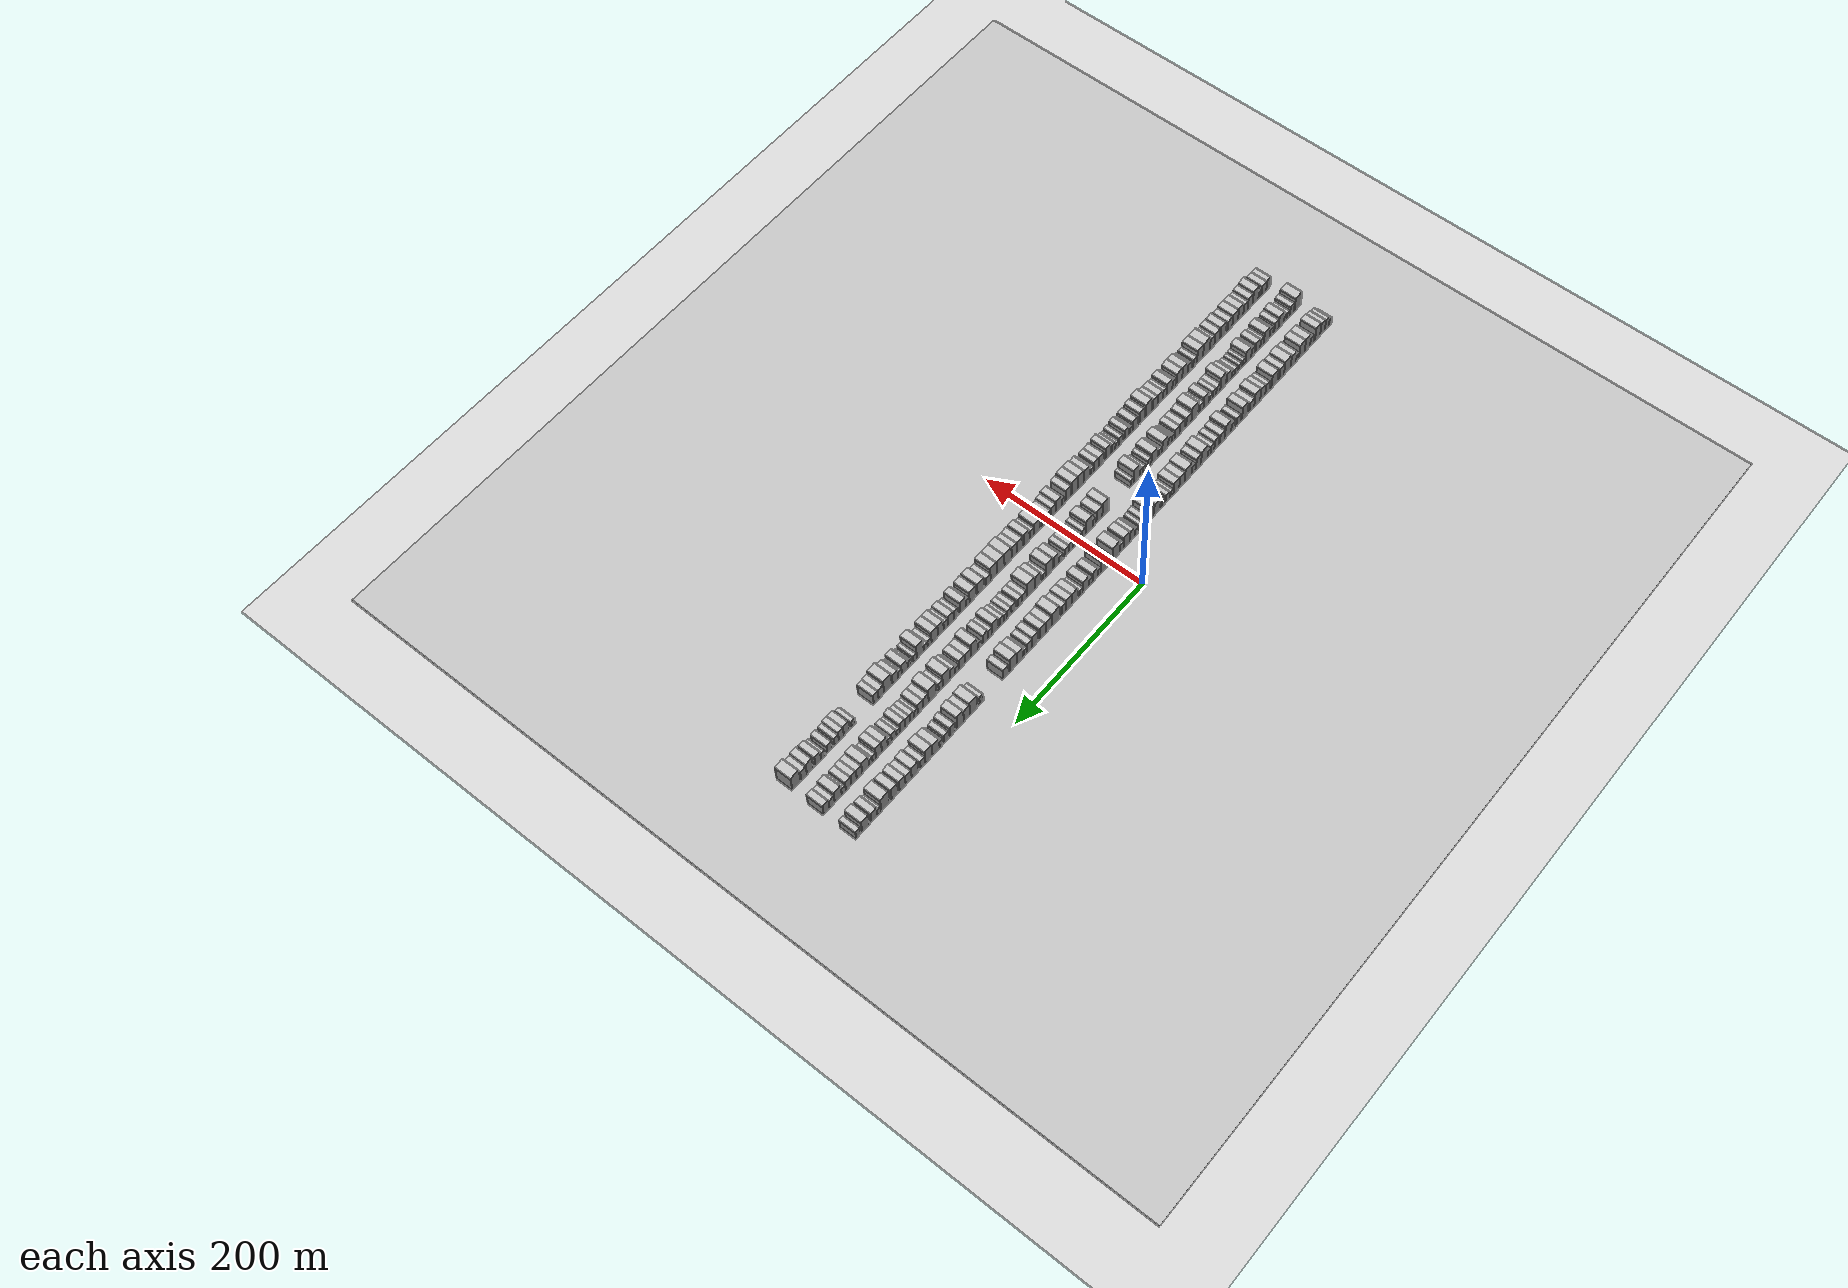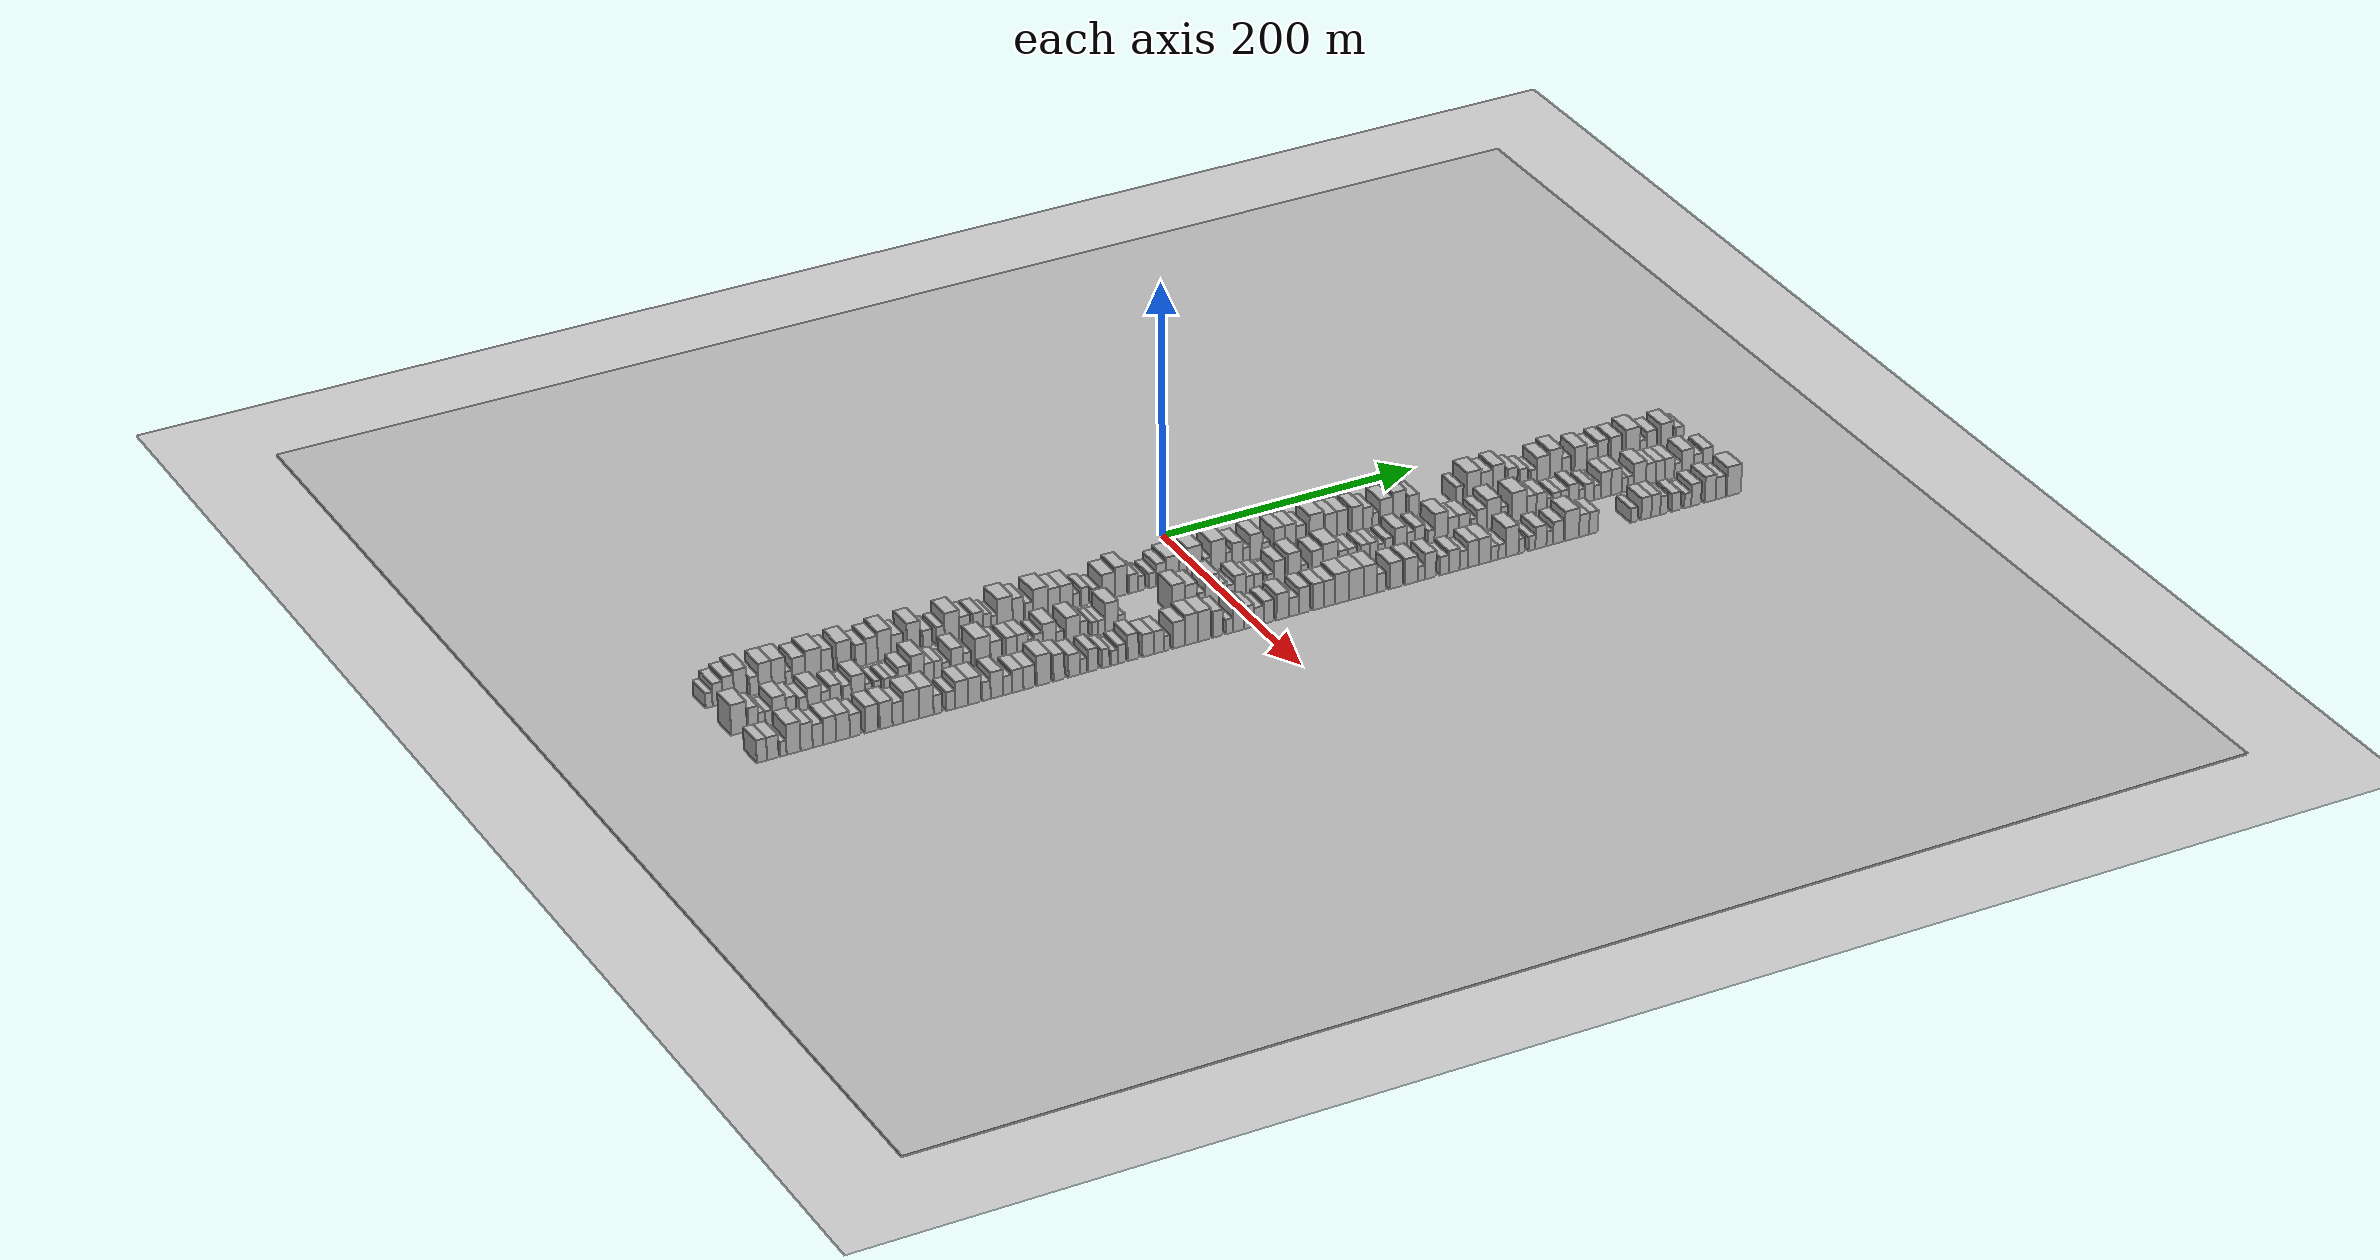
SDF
<?xml version="1.0" encoding="utf-8"?>

<sdf version="1.6">

   <world name="default">

      <gui fullscreen="0">

         <camera name="user_camera">

            <pose>-15 0 4.57585 0 0 0</pose>

            <view_controller>orbit</view_controller>

         </camera>

      </gui>

      <scene>

         <sky>

           <clouds>

             <speed>12</speed>

           </clouds>

         </sky>

         <ambient>0.4 0.4 0.4 1</ambient>

         <background>0.7 0.7 0.7 1</background>

         <shadows>1</shadows>

      </scene>

      <gravity>0 0 -9.8066</gravity>

      <magnetic_field>6e-06 2.3e-05 -4.2e-05</magnetic_field>

      <physics default="0" name="default_physics" type="ode">

         <ode>

            <solver>

               <type>quick</type>

               <iters>10</iters>

               <sor>1.0</sor>

               <use_dynamic_moi_rescaling>0</use_dynamic_moi_rescaling>

            </solver>

            <constraints>

               <cfm>0</cfm>

               <erp>0.2</erp>

               <contact_max_correcting_vel>100</contact_max_correcting_vel>

               <contact_surface_layer>0.001</contact_surface_layer>

            </constraints>

         </ode>

         <max_step_size>0.004</max_step_size>

         <real_time_factor>1</real_time_factor>

         <real_time_update_rate>250</real_time_update_rate>

      </physics>

      <light name="sun" type="directional">

         <cast_shadows>1</cast_shadows>

         <pose>0 0 10 0 0 0</pose>

         <diffuse>0.8 0.8 0.8 1</diffuse>

         <specular>0.2 0.2 0.2 1</specular>

         <attenuation>

            <range>1000</range>

            <constant>0.9</constant>

            <linear>0.01</linear>

            <quadratic>0.001</quadratic>

         </attenuation>

         <direction>-0.5 0.1 -0.9</direction>

      </light>

      <include>

         <name>ground_plane_1</name>

         <uri>model://HANNAS_ground_plane</uri>

         <pose>0 0 0  0 0 0</pose>

      </include>

      <include>

         <name>ground_plane_2</name>

         <uri>model://HANNAS_ground_plane</uri>

         <pose>100 0 0  0 0 0</pose>

      </include>

      <model name="building_1">

         <static>1</static>

         <pose frame="">50.0000 -377.3886 0 0.000000 0.000000 0.000000</pose>

         <link name="link">

            <pose frame="">0 0 6.00 0 0 0</pose>

            <collision name="collision">

               <geometry>

                  <box>

                     <size>20.0000 5.2227 12.0000</size>

                  </box>

               </geometry>

               <max_contacts>10</max_contacts>

               <surface>

                  <contact>

                     <ode/>

                  </contact>

                  <bounce/>

                  <friction>

                     <torsional>

                        <ode/>

                     </torsional>

                     <ode/>

                  </friction>

               </surface>

            </collision>

            <visual name="visual">

               <cast_shadows>0</cast_shadows>

               <geometry>

                  <box>

                     <size>20.0000 5.2227 12.0000</size>

                  </box>

               </geometry>

               <material>

                  <script>

                     <uri>model://HANNAS_wall/materials/scripts</uri>

                     <uri>model://HANNAS_wall/materials/textures</uri>

                     <name>vrc/HANNAS_wall</name>

                  </script>

               </material>

            </visual>

            <self_collide>0</self_collide>

            <enable_wind>0</enable_wind>

            <kinematic>0</kinematic>

         </link>

      </model>

      <model name="building_2">

         <static>1</static>

         <pose frame="">50.0000 -371.0098 0 0.000000 0.000000 0.000000</pose>

         <link name="link">

            <pose frame="">0 0 9.00 0 0 0</pose>

            <collision name="collision">

               <geometry>

                  <box>

                     <size>20.0000 7.5350 18.0000</size>

                  </box>

               </geometry>

               <max_contacts>10</max_contacts>

               <surface>

                  <contact>

                     <ode/>

                  </contact>

                  <bounce/>

                  <friction>

                     <torsional>

                        <ode/>

                     </torsional>

                     <ode/>

                  </friction>

               </surface>

            </collision>

            <visual name="visual">

               <cast_shadows>0</cast_shadows>

               <geometry>

                  <box>

                     <size>20.0000 7.5350 18.0000</size>

                  </box>

               </geometry>

               <material>

                  <script>

                     <uri>model://HANNAS_wall/materials/scripts</uri>

                     <uri>model://HANNAS_wall/materials/textures</uri>

                     <name>vrc/HANNAS_wall</name>

                  </script>

               </material>

            </visual>

            <self_collide>0</self_collide>

            <enable_wind>0</enable_wind>

            <kinematic>0</kinematic>

         </link>

      </model>

      <model name="building_3">

         <static>1</static>

         <pose frame="">50.0000 -363.0318 0 0.000000 0.000000 0.000000</pose>

         <link name="link">

            <pose frame="">0 0 10.50 0 0 0</pose>

            <collision name="collision">

               <geometry>

                  <box>

                     <size>20.0000 8.4210 21.0000</size>

                  </box>

               </geometry>

               <max_contacts>10</max_contacts>

               <surface>

                  <contact>

                     <ode/>

                  </contact>

                  <bounce/>

                  <friction>

                     <torsional>

                        <ode/>

                     </torsional>

                     <ode/>

                  </friction>

               </surface>

            </collision>

            <visual name="visual">

               <cast_shadows>0</cast_shadows>

               <geometry>

                  <box>

                     <size>20.0000 8.4210 21.0000</size>

                  </box>

               </geometry>

               <material>

                  <script>

                     <uri>model://HANNAS_wall/materials/scripts</uri>

                     <uri>model://HANNAS_wall/materials/textures</uri>

                     <name>vrc/HANNAS_wall</name>

                  </script>

               </material>

            </visual>

            <self_collide>0</self_collide>

            <enable_wind>0</enable_wind>

            <kinematic>0</kinematic>

         </link>

      </model>

      <model name="building_4">

         <static>1</static>

         <pose frame="">50.0000 -353.9402 0 0.000000 0.000000 0.000000</pose>

         <link name="link">

            <pose frame="">0 0 12.00 0 0 0</pose>

            <collision name="collision">

               <geometry>

                  <box>

                     <size>20.0000 9.7621 24.0000</size>

                  </box>

               </geometry>

               <max_contacts>10</max_contacts>

               <surface>

                  <contact>

                     <ode/>

                  </contact>

                  <bounce/>

                  <friction>

                     <torsional>

                        <ode/>

                     </torsional>

                     <ode/>

                  </friction>

               </surface>

            </collision>

            <visual name="visual">

               <cast_shadows>0</cast_shadows>

               <geometry>

                  <box>

                     <size>20.0000 9.7621 24.0000</size>

                  </box>

               </geometry>

               <material>

                  <script>

                     <uri>model://HANNAS_wall/materials/scripts</uri>

                     <uri>model://HANNAS_wall/materials/textures</uri>

                     <name>vrc/HANNAS_wall</name>

                  </script>

               </material>

            </visual>

            <self_collide>0</self_collide>

            <enable_wind>0</enable_wind>

            <kinematic>0</kinematic>

         </link>

      </model>

      <model name="building_5">

         <static>1</static>

         <pose frame="">50.0000 -343.7180 0 0.000000 0.000000 0.000000</pose>

         <link name="link">

            <pose frame="">0 0 7.50 0 0 0</pose>

            <collision name="collision">

               <geometry>

                  <box>

                     <size>20.0000 6.6824 15.0000</size>

                  </box>

               </geometry>

               <max_contacts>10</max_contacts>

               <surface>

                  <contact>

                     <ode/>

                  </contact>

                  <bounce/>

                  <friction>

                     <torsional>

                        <ode/>

                     </torsional>

                     <ode/>

                  </friction>

               </surface>

            </collision>

            <visual name="visual">

               <cast_shadows>0</cast_shadows>

               <geometry>

                  <box>

                     <size>20.0000 6.6824 15.0000</size>

                  </box>

               </geometry>

               <material>

                  <script>

                     <uri>model://HANNAS_wall/materials/scripts</uri>

                     <uri>model://HANNAS_wall/materials/textures</uri>

                     <name>vrc/HANNAS_wall</name>

                  </script>

               </material>

            </visual>

            <self_collide>0</self_collide>

            <enable_wind>0</enable_wind>

            <kinematic>0</kinematic>

         </link>

      </model>

      <model name="building_6">

         <static>1</static>

         <pose frame="">50.0000 -335.5096 0 0.000000 0.000000 0.000000</pose>

         <link name="link">

            <pose frame="">0 0 12.00 0 0 0</pose>

            <collision name="collision">

               <geometry>

                  <box>

                     <size>20.0000 9.7343 24.0000</size>

                  </box>

               </geometry>

               <max_contacts>10</max_contacts>

               <surface>

                  <contact>

                     <ode/>

                  </contact>

                  <bounce/>

                  <friction>

                     <torsional>

                        <ode/>

                     </torsional>

                     <ode/>

                  </friction>

               </surface>

            </collision>

            <visual name="visual">

               <cast_shadows>0</cast_shadows>

               <geometry>

                  <box>

                     <size>20.0000 9.7343 24.0000</size>

                  </box>

               </geometry>

               <material>

                  <script>

                     <uri>model://HANNAS_wall/materials/scripts</uri>

                     <uri>model://HANNAS_wall/materials/textures</uri>

                     <name>vrc/HANNAS_wall</name>

                  </script>

               </material>

            </visual>

            <self_collide>0</self_collide>

            <enable_wind>0</enable_wind>

            <kinematic>0</kinematic>

         </link>

      </model>

      <model name="building_7">

         <static>1</static>

         <pose frame="">50.0000 -325.4724 0 0.000000 0.000000 0.000000</pose>

         <link name="link">

            <pose frame="">0 0 12.00 0 0 0</pose>

            <collision name="collision">

               <geometry>

                  <box>

                     <size>20.0000 10.3402 24.0000</size>

                  </box>

               </geometry>

               <max_contacts>10</max_contacts>

               <surface>

                  <contact>

                     <ode/>

                  </contact>

                  <bounce/>

                  <friction>

                     <torsional>

                        <ode/>

                     </torsional>

                     <ode/>

                  </friction>

               </surface>

            </collision>

            <visual name="visual">

               <cast_shadows>0</cast_shadows>

               <geometry>

                  <box>

                     <size>20.0000 10.3402 24.0000</size>

                  </box>

               </geometry>

               <material>

                  <script>

                     <uri>model://HANNAS_wall/materials/scripts</uri>

                     <uri>model://HANNAS_wall/materials/textures</uri>

                     <name>vrc/HANNAS_wall</name>

                  </script>

               </material>

            </visual>

            <self_collide>0</self_collide>

            <enable_wind>0</enable_wind>

            <kinematic>0</kinematic>

         </link>

      </model>

      <model name="building_8">

         <static>1</static>

         <pose frame="">50.0000 -317.7057 0 0.000000 0.000000 0.000000</pose>

         <link name="link">

            <pose frame="">0 0 6.00 0 0 0</pose>

            <collision name="collision">

               <geometry>

                  <box>

                     <size>20.0000 5.1933 12.0000</size>

                  </box>

               </geometry>

               <max_contacts>10</max_contacts>

               <surface>

                  <contact>

                     <ode/>

                  </contact>

                  <bounce/>

                  <friction>

                     <torsional>

                        <ode/>

                     </torsional>

                     <ode/>

                  </friction>

               </surface>

            </collision>

            <visual name="visual">

               <cast_shadows>0</cast_shadows>

               <geometry>

                  <box>

                     <size>20.0000 5.1933 12.0000</size>

                  </box>

               </geometry>

               <material>

                  <script>

                     <uri>model://HANNAS_wall/materials/scripts</uri>

                     <uri>model://HANNAS_wall/materials/textures</uri>

                     <name>vrc/HANNAS_wall</name>

                  </script>

               </material>

            </visual>

            <self_collide>0</self_collide>

            <enable_wind>0</enable_wind>

            <kinematic>0</kinematic>

         </link>

      </model>

      <model name="building_9">

         <static>1</static>

         <pose frame="">50.0000 -310.2537 0 0.000000 0.000000 0.000000</pose>

         <link name="link">

            <pose frame="">0 0 10.50 0 0 0</pose>

            <collision name="collision">

               <geometry>

                  <box>

                     <size>20.0000 9.7105 21.0000</size>

                  </box>

               </geometry>

               <max_contacts>10</max_contacts>

               <surface>

                  <contact>

                     <ode/>

                  </contact>

                  <bounce/>

                  <friction>

                     <torsional>

                        <ode/>

                     </torsional>

                     <ode/>

                  </friction>

               </surface>

            </collision>

            <visual name="visual">

               <cast_shadows>0</cast_shadows>

               <geometry>

                  <box>

                     <size>20.0000 9.7105 21.0000</size>

                  </box>

               </geometry>

               <material>

                  <script>

                     <uri>model://HANNAS_wall/materials/scripts</uri>

                     <uri>model://HANNAS_wall/materials/textures</uri>

                     <name>vrc/HANNAS_wall</name>

                  </script>

               </material>

            </visual>

            <self_collide>0</self_collide>

            <enable_wind>0</enable_wind>

            <kinematic>0</kinematic>

         </link>

      </model>

      <model name="building_10">

         <static>1</static>

         <pose frame="">50.0000 -299.4055 0 0.000000 0.000000 0.000000</pose>

         <link name="link">

            <pose frame="">0 0 12.00 0 0 0</pose>

            <collision name="collision">

               <geometry>

                  <box>

                     <size>20.0000 11.9860 24.0000</size>

                  </box>

               </geometry>

               <max_contacts>10</max_contacts>

               <surface>

                  <contact>

                     <ode/>

                  </contact>

                  <bounce/>

                  <friction>

                     <torsional>

                        <ode/>

                     </torsional>

                     <ode/>

                  </friction>

               </surface>

            </collision>

            <visual name="visual">

               <cast_shadows>0</cast_shadows>

               <geometry>

                  <box>

                     <size>20.0000 11.9860 24.0000</size>

                  </box>

               </geometry>

               <material>

                  <script>

                     <uri>model://HANNAS_wall/materials/scripts</uri>

                     <uri>model://HANNAS_wall/materials/textures</uri>

                     <name>vrc/HANNAS_wall</name>

                  </script>

               </material>

            </visual>

            <self_collide>0</self_collide>

            <enable_wind>0</enable_wind>

            <kinematic>0</kinematic>

         </link>

      </model>

      <model name="building_11">

         <static>1</static>

         <pose frame="">50.0000 -289.1540 0 0.000000 0.000000 0.000000</pose>

         <link name="link">

            <pose frame="">0 0 10.50 0 0 0</pose>

            <collision name="collision">

               <geometry>

                  <box>

                     <size>20.0000 8.5169 21.0000</size>

                  </box>

               </geometry>

               <max_contacts>10</max_contacts>

               <surface>

                  <contact>

                     <ode/>

                  </contact>

                  <bounce/>

                  <friction>

                     <torsional>

                        <ode/>

                     </torsional>

                     <ode/>

                  </friction>

               </surface>

            </collision>

            <visual name="visual">

               <cast_shadows>0</cast_shadows>

               <geometry>

                  <box>

                     <size>20.0000 8.5169 21.0000</size>

                  </box>

               </geometry>

               <material>

                  <script>

                     <uri>model://HANNAS_wall/materials/scripts</uri>

                     <uri>model://HANNAS_wall/materials/textures</uri>

                     <name>vrc/HANNAS_wall</name>

                  </script>

               </material>

            </visual>

            <self_collide>0</self_collide>

            <enable_wind>0</enable_wind>

            <kinematic>0</kinematic>

         </link>

      </model>

      <model name="building_12">

         <static>1</static>

         <pose frame="">50.0000 -276.3157 0 0.000000 0.000000 0.000000</pose>

         <link name="link">

            <pose frame="">0 0 12.00 0 0 0</pose>

            <collision name="collision">

               <geometry>

                  <box>

                     <size>20.0000 11.1597 24.0000</size>

                  </box>

               </geometry>

               <max_contacts>10</max_contacts>

               <surface>

                  <contact>

                     <ode/>

                  </contact>

                  <bounce/>

                  <friction>

                     <torsional>

                        <ode/>

                     </torsional>

                     <ode/>

                  </friction>

               </surface>

            </collision>

            <visual name="visual">

               <cast_shadows>0</cast_shadows>

               <geometry>

                  <box>

                     <size>20.0000 11.1597 24.0000</size>

                  </box>

               </geometry>

               <material>

                  <script>

                     <uri>model://HANNAS_wall/materials/scripts</uri>

                     <uri>model://HANNAS_wall/materials/textures</uri>

                     <name>vrc/HANNAS_wall</name>

                  </script>

               </material>

            </visual>

            <self_collide>0</self_collide>

            <enable_wind>0</enable_wind>

            <kinematic>0</kinematic>

         </link>

      </model>

      <model name="building_13">

         <static>1</static>

         <pose frame="">50.0000 -263.8303 0 0.000000 0.000000 0.000000</pose>

         <link name="link">

            <pose frame="">0 0 9.00 0 0 0</pose>

            <collision name="collision">

               <geometry>

                  <box>

                     <size>20.0000 7.8110 18.0000</size>

                  </box>

               </geometry>

               <max_contacts>10</max_contacts>

               <surface>

                  <contact>

                     <ode/>

                  </contact>

                  <bounce/>

                  <friction>

                     <torsional>

                        <ode/>

                     </torsional>

                     <ode/>

                  </friction>

               </surface>

            </collision>

            <visual name="visual">

               <cast_shadows>0</cast_shadows>

               <geometry>

                  <box>

                     <size>20.0000 7.8110 18.0000</size>

                  </box>

               </geometry>

               <material>

                  <script>

                     <uri>model://HANNAS_wall/materials/scripts</uri>

                     <uri>model://HANNAS_wall/materials/textures</uri>

                     <name>vrc/HANNAS_wall</name>

                  </script>

               </material>

            </visual>

            <self_collide>0</self_collide>

            <enable_wind>0</enable_wind>

            <kinematic>0</kinematic>

         </link>

      </model>

      <model name="building_14">

         <static>1</static>

         <pose frame="">50.0000 -255.4769 0 0.000000 0.000000 0.000000</pose>

         <link name="link">

            <pose frame="">0 0 10.50 0 0 0</pose>

            <collision name="collision">

               <geometry>

                  <box>

                     <size>20.0000 8.8958 21.0000</size>

                  </box>

               </geometry>

               <max_contacts>10</max_contacts>

               <surface>

                  <contact>

                     <ode/>

                  </contact>

                  <bounce/>

                  <friction>

                     <torsional>

                        <ode/>

                     </torsional>

                     <ode/>

                  </friction>

               </surface>

            </collision>

            <visual name="visual">

               <cast_shadows>0</cast_shadows>

               <geometry>

                  <box>

                     <size>20.0000 8.8958 21.0000</size>

                  </box>

               </geometry>

               <material>

                  <script>

                     <uri>model://HANNAS_wall/materials/scripts</uri>

                     <uri>model://HANNAS_wall/materials/textures</uri>

                     <name>vrc/HANNAS_wall</name>

                  </script>

               </material>

            </visual>

            <self_collide>0</self_collide>

            <enable_wind>0</enable_wind>

            <kinematic>0</kinematic>

         </link>

      </model>

      <model name="building_15">

         <static>1</static>

         <pose frame="">50.0000 -245.8537 0 0.000000 0.000000 0.000000</pose>

         <link name="link">

            <pose frame="">0 0 12.00 0 0 0</pose>

            <collision name="collision">

               <geometry>

                  <box>

                     <size>20.0000 10.3506 24.0000</size>

                  </box>

               </geometry>

               <max_contacts>10</max_contacts>

               <surface>

                  <contact>

                     <ode/>

                  </contact>

                  <bounce/>

                  <friction>

                     <torsional>

                        <ode/>

                     </torsional>

                     <ode/>

                  </friction>

               </surface>

            </collision>

            <visual name="visual">

               <cast_shadows>0</cast_shadows>

               <geometry>

                  <box>

                     <size>20.0000 10.3506 24.0000</size>

                  </box>

               </geometry>

               <material>

                  <script>

                     <uri>model://HANNAS_wall/materials/scripts</uri>

                     <uri>model://HANNAS_wall/materials/textures</uri>

                     <name>vrc/HANNAS_wall</name>

                  </script>

               </material>

            </visual>

            <self_collide>0</self_collide>

            <enable_wind>0</enable_wind>

            <kinematic>0</kinematic>

         </link>

      </model>

      <model name="building_16">

         <static>1</static>

         <pose frame="">50.0000 -236.2907 0 0.000000 0.000000 0.000000</pose>

         <link name="link">

            <pose frame="">0 0 9.00 0 0 0</pose>

            <collision name="collision">

               <geometry>

                  <box>

                     <size>20.0000 8.7754 18.0000</size>

                  </box>

               </geometry>

               <max_contacts>10</max_contacts>

               <surface>

                  <contact>

                     <ode/>

                  </contact>

                  <bounce/>

                  <friction>

                     <torsional>

                        <ode/>

                     </torsional>

                     <ode/>

                  </friction>

               </surface>

            </collision>

            <visual name="visual">

               <cast_shadows>0</cast_shadows>

               <geometry>

                  <box>

                     <size>20.0000 8.7754 18.0000</size>

                  </box>

               </geometry>

               <material>

                  <script>

                     <uri>model://HANNAS_wall/materials/scripts</uri>

                     <uri>model://HANNAS_wall/materials/textures</uri>

                     <name>vrc/HANNAS_wall</name>

                  </script>

               </material>

            </visual>

            <self_collide>0</self_collide>

            <enable_wind>0</enable_wind>

            <kinematic>0</kinematic>

         </link>

      </model>

      <model name="building_17">

         <static>1</static>

         <pose frame="">50.0000 -223.9286 0 0.000000 0.000000 0.000000</pose>

         <link name="link">

            <pose frame="">0 0 12.00 0 0 0</pose>

            <collision name="collision">

               <geometry>

                  <box>

                     <size>20.0000 9.9487 24.0000</size>

                  </box>

               </geometry>

               <max_contacts>10</max_contacts>

               <surface>

                  <contact>

                     <ode/>

                  </contact>

                  <bounce/>

                  <friction>

                     <torsional>

                        <ode/>

                     </torsional>

                     <ode/>

                  </friction>

               </surface>

            </collision>

            <visual name="visual">

               <cast_shadows>0</cast_shadows>

               <geometry>

                  <box>

                     <size>20.0000 9.9487 24.0000</size>

                  </box>

               </geometry>

               <material>

                  <script>

                     <uri>model://HANNAS_wall/materials/scripts</uri>

                     <uri>model://HANNAS_wall/materials/textures</uri>

                     <name>vrc/HANNAS_wall</name>

                  </script>

               </material>

            </visual>

            <self_collide>0</self_collide>

            <enable_wind>0</enable_wind>

            <kinematic>0</kinematic>

         </link>

      </model>

      <model name="building_18">

         <static>1</static>

         <pose frame="">50.0000 -213.2876 0 0.000000 0.000000 0.000000</pose>

         <link name="link">

            <pose frame="">0 0 7.50 0 0 0</pose>

            <collision name="collision">

               <geometry>

                  <box>

                     <size>20.0000 7.3333 15.0000</size>

                  </box>

               </geometry>

               <max_contacts>10</max_contacts>

               <surface>

                  <contact>

                     <ode/>

                  </contact>

                  <bounce/>

                  <friction>

                     <torsional>

                        <ode/>

                     </torsional>

                     <ode/>

                  </friction>

               </surface>

            </collision>

            <visual name="visual">

               <cast_shadows>0</cast_shadows>

               <geometry>

                  <box>

                     <size>20.0000 7.3333 15.0000</size>

                  </box>

               </geometry>

               <material>

                  <script>

                     <uri>model://HANNAS_wall/materials/scripts</uri>

                     <uri>model://HANNAS_wall/materials/textures</uri>

                     <name>vrc/HANNAS_wall</name>

                  </script>

               </material>

            </visual>

            <self_collide>0</self_collide>

            <enable_wind>0</enable_wind>

            <kinematic>0</kinematic>

         </link>

      </model>

      <model name="building_19">

         <static>1</static>

         <pose frame="">50.0000 -203.4211 0 0.000000 0.000000 0.000000</pose>

         <link name="link">

            <pose frame="">0 0 7.50 0 0 0</pose>

            <collision name="collision">

               <geometry>

                  <box>

                     <size>20.0000 6.3996 15.0000</size>

                  </box>

               </geometry>

               <max_contacts>10</max_contacts>

               <surface>

                  <contact>

                     <ode/>

                  </contact>

                  <bounce/>

                  <friction>

                     <torsional>

                        <ode/>

                     </torsional>

                     <ode/>

                  </friction>

               </surface>

            </collision>

            <visual name="visual">

               <cast_shadows>0</cast_shadows>

               <geometry>

                  <box>

                     <size>20.0000 6.3996 15.0000</size>

                  </box>

               </geometry>

               <material>

                  <script>

                     <uri>model://HANNAS_wall/materials/scripts</uri>

                     <uri>model://HANNAS_wall/materials/textures</uri>

                     <name>vrc/HANNAS_wall</name>

                  </script>

               </material>

            </visual>

            <self_collide>0</self_collide>

            <enable_wind>0</enable_wind>

            <kinematic>0</kinematic>

         </link>

      </model>

      <model name="building_20">

         <static>1</static>

         <pose frame="">50.0000 -194.7316 0 0.000000 0.000000 0.000000</pose>

         <link name="link">

            <pose frame="">0 0 12.00 0 0 0</pose>

            <collision name="collision">

               <geometry>

                  <box>

                     <size>20.0000 10.9794 24.0000</size>

                  </box>

               </geometry>

               <max_contacts>10</max_contacts>

               <surface>

                  <contact>

                     <ode/>

                  </contact>

                  <bounce/>

                  <friction>

                     <torsional>

                        <ode/>

                     </torsional>

                     <ode/>

                  </friction>

               </surface>

            </collision>

            <visual name="visual">

               <cast_shadows>0</cast_shadows>

               <geometry>

                  <box>

                     <size>20.0000 10.9794 24.0000</size>

                  </box>

               </geometry>

               <material>

                  <script>

                     <uri>model://HANNAS_wall/materials/scripts</uri>

                     <uri>model://HANNAS_wall/materials/textures</uri>

                     <name>vrc/HANNAS_wall</name>

                  </script>

               </material>

            </visual>

            <self_collide>0</self_collide>

            <enable_wind>0</enable_wind>

            <kinematic>0</kinematic>

         </link>

      </model>

      <model name="building_21">

         <static>1</static>

         <pose frame="">50.0000 -184.9429 0 0.000000 0.000000 0.000000</pose>

         <link name="link">

            <pose frame="">0 0 9.00 0 0 0</pose>

            <collision name="collision">

               <geometry>

                  <box>

                     <size>20.0000 8.5980 18.0000</size>

                  </box>

               </geometry>

               <max_contacts>10</max_contacts>

               <surface>

                  <contact>

                     <ode/>

                  </contact>

                  <bounce/>

                  <friction>

                     <torsional>

                        <ode/>

                     </torsional>

                     <ode/>

                  </friction>

               </surface>

            </collision>

            <visual name="visual">

               <cast_shadows>0</cast_shadows>

               <geometry>

                  <box>

                     <size>20.0000 8.5980 18.0000</size>

                  </box>

               </geometry>

               <material>

                  <script>

                     <uri>model://HANNAS_wall/materials/scripts</uri>

                     <uri>model://HANNAS_wall/materials/textures</uri>

                     <name>vrc/HANNAS_wall</name>

                  </script>

               </material>

            </visual>

            <self_collide>0</self_collide>

            <enable_wind>0</enable_wind>

            <kinematic>0</kinematic>

         </link>

      </model>

      <model name="building_22">

         <static>1</static>

         <pose frame="">50.0000 -174.7971 0 0.000000 0.000000 0.000000</pose>

         <link name="link">

            <pose frame="">0 0 9.00 0 0 0</pose>

            <collision name="collision">

               <geometry>

                  <box>

                     <size>20.0000 7.6934 18.0000</size>

                  </box>

               </geometry>

               <max_contacts>10</max_contacts>

               <surface>

                  <contact>

                     <ode/>

                  </contact>

                  <bounce/>

                  <friction>

                     <torsional>

                        <ode/>

                     </torsional>

                     <ode/>

                  </friction>

               </surface>

            </collision>

            <visual name="visual">

               <cast_shadows>0</cast_shadows>

               <geometry>

                  <box>

                     <size>20.0000 7.6934 18.0000</size>

                  </box>

               </geometry>

               <material>

                  <script>

                     <uri>model://HANNAS_wall/materials/scripts</uri>

                     <uri>model://HANNAS_wall/materials/textures</uri>

                     <name>vrc/HANNAS_wall</name>

                  </script>

               </material>

            </visual>

            <self_collide>0</self_collide>

            <enable_wind>0</enable_wind>

            <kinematic>0</kinematic>

         </link>

      </model>

      <model name="building_23">

         <static>1</static>

         <pose frame="">50.0000 -167.9164 0 0.000000 0.000000 0.000000</pose>

         <link name="link">

            <pose frame="">0 0 7.50 0 0 0</pose>

            <collision name="collision">

               <geometry>

                  <box>

                     <size>20.0000 6.0680 15.0000</size>

                  </box>

               </geometry>

               <max_contacts>10</max_contacts>

               <surface>

                  <contact>

                     <ode/>

                  </contact>

                  <bounce/>

                  <friction>

                     <torsional>

                        <ode/>

                     </torsional>

                     <ode/>

                  </friction>

               </surface>

            </collision>

            <visual name="visual">

               <cast_shadows>0</cast_shadows>

               <geometry>

                  <box>

                     <size>20.0000 6.0680 15.0000</size>

                  </box>

               </geometry>

               <material>

                  <script>

                     <uri>model://HANNAS_wall/materials/scripts</uri>

                     <uri>model://HANNAS_wall/materials/textures</uri>

                     <name>vrc/HANNAS_wall</name>

                  </script>

               </material>

            </visual>

            <self_collide>0</self_collide>

            <enable_wind>0</enable_wind>

            <kinematic>0</kinematic>

         </link>

      </model>

      <model name="building_24">

         <static>1</static>

         <pose frame="">50.0000 -162.3977 0 0.000000 0.000000 0.000000</pose>

         <link name="link">

            <pose frame="">0 0 6.00 0 0 0</pose>

            <collision name="collision">

               <geometry>

                  <box>

                     <size>20.0000 4.9694 12.0000</size>

                  </box>

               </geometry>

               <max_contacts>10</max_contacts>

               <surface>

                  <contact>

                     <ode/>

                  </contact>

                  <bounce/>

                  <friction>

                     <torsional>

                        <ode/>

                     </torsional>

                     <ode/>

                  </friction>

               </surface>

            </collision>

            <visual name="visual">

               <cast_shadows>0</cast_shadows>

               <geometry>

                  <box>

                     <size>20.0000 4.9694 12.0000</size>

                  </box>

               </geometry>

               <material>

                  <script>

                     <uri>model://HANNAS_wall/materials/scripts</uri>

                     <uri>model://HANNAS_wall/materials/textures</uri>

                     <name>vrc/HANNAS_wall</name>

                  </script>

               </material>

            </visual>

            <self_collide>0</self_collide>

            <enable_wind>0</enable_wind>

            <kinematic>0</kinematic>

         </link>

      </model>

      <model name="building_25">

         <static>1</static>

         <pose frame="">50.0000 -154.0770 0 0.000000 0.000000 0.000000</pose>

         <link name="link">

            <pose frame="">0 0 12.00 0 0 0</pose>

            <collision name="collision">

               <geometry>

                  <box>

                     <size>20.0000 11.6722 24.0000</size>

                  </box>

               </geometry>

               <max_contacts>10</max_contacts>

               <surface>

                  <contact>

                     <ode/>

                  </contact>

                  <bounce/>

                  <friction>

                     <torsional>

                        <ode/>

                     </torsional>

                     <ode/>

                  </friction>

               </surface>

            </collision>

            <visual name="visual">

               <cast_shadows>0</cast_shadows>

               <geometry>

                  <box>

                     <size>20.0000 11.6722 24.0000</size>

                  </box>

               </geometry>

               <material>

                  <script>

                     <uri>model://HANNAS_wall/materials/scripts</uri>

                     <uri>model://HANNAS_wall/materials/textures</uri>

                     <name>vrc/HANNAS_wall</name>

                  </script>

               </material>

            </visual>

            <self_collide>0</self_collide>

            <enable_wind>0</enable_wind>

            <kinematic>0</kinematic>

         </link>

      </model>

      <model name="building_26">

         <static>1</static>

         <pose frame="">50.0000 -143.9852 0 0.000000 0.000000 0.000000</pose>

         <link name="link">

            <pose frame="">0 0 10.50 0 0 0</pose>

            <collision name="collision">

               <geometry>

                  <box>

                     <size>20.0000 8.5114 21.0000</size>

                  </box>

               </geometry>

               <max_contacts>10</max_contacts>

               <surface>

                  <contact>

                     <ode/>

                  </contact>

                  <bounce/>

                  <friction>

                     <torsional>

                        <ode/>

                     </torsional>

                     <ode/>

                  </friction>

               </surface>

            </collision>

            <visual name="visual">

               <cast_shadows>0</cast_shadows>

               <geometry>

                  <box>

                     <size>20.0000 8.5114 21.0000</size>

                  </box>

               </geometry>

               <material>

                  <script>

                     <uri>model://HANNAS_wall/materials/scripts</uri>

                     <uri>model://HANNAS_wall/materials/textures</uri>

                     <name>vrc/HANNAS_wall</name>

                  </script>

               </material>

            </visual>

            <self_collide>0</self_collide>

            <enable_wind>0</enable_wind>

            <kinematic>0</kinematic>

         </link>

      </model>

      <model name="building_27">

         <static>1</static>

         <pose frame="">50.0000 -135.7259 0 0.000000 0.000000 0.000000</pose>

         <link name="link">

            <pose frame="">0 0 7.50 0 0 0</pose>

            <collision name="collision">

               <geometry>

                  <box>

                     <size>20.0000 6.0072 15.0000</size>

                  </box>

               </geometry>

               <max_contacts>10</max_contacts>

               <surface>

                  <contact>

                     <ode/>

                  </contact>

                  <bounce/>

                  <friction>

                     <torsional>

                        <ode/>

                     </torsional>

                     <ode/>

                  </friction>

               </surface>

            </collision>

            <visual name="visual">

               <cast_shadows>0</cast_shadows>

               <geometry>

                  <box>

                     <size>20.0000 6.0072 15.0000</size>

                  </box>

               </geometry>

               <material>

                  <script>

                     <uri>model://HANNAS_wall/materials/scripts</uri>

                     <uri>model://HANNAS_wall/materials/textures</uri>

                     <name>vrc/HANNAS_wall</name>

                  </script>

               </material>

            </visual>

            <self_collide>0</self_collide>

            <enable_wind>0</enable_wind>

            <kinematic>0</kinematic>

         </link>

      </model>

      <model name="building_28">

         <static>1</static>

         <pose frame="">50.0000 -126.7487 0 0.000000 0.000000 0.000000</pose>

         <link name="link">

            <pose frame="">0 0 12.00 0 0 0</pose>

            <collision name="collision">

               <geometry>

                  <box>

                     <size>20.0000 11.9471 24.0000</size>

                  </box>

               </geometry>

               <max_contacts>10</max_contacts>

               <surface>

                  <contact>

                     <ode/>

                  </contact>

                  <bounce/>

                  <friction>

                     <torsional>

                        <ode/>

                     </torsional>

                     <ode/>

                  </friction>

               </surface>

            </collision>

            <visual name="visual">

               <cast_shadows>0</cast_shadows>

               <geometry>

                  <box>

                     <size>20.0000 11.9471 24.0000</size>

                  </box>

               </geometry>

               <material>

                  <script>

                     <uri>model://HANNAS_wall/materials/scripts</uri>

                     <uri>model://HANNAS_wall/materials/textures</uri>

                     <name>vrc/HANNAS_wall</name>

                  </script>

               </material>

            </visual>

            <self_collide>0</self_collide>

            <enable_wind>0</enable_wind>

            <kinematic>0</kinematic>

         </link>

      </model>

      <model name="building_29">

         <static>1</static>

         <pose frame="">50.0000 -116.1441 0 0.000000 0.000000 0.000000</pose>

         <link name="link">

            <pose frame="">0 0 10.50 0 0 0</pose>

            <collision name="collision">

               <geometry>

                  <box>

                     <size>20.0000 9.2621 21.0000</size>

                  </box>

               </geometry>

               <max_contacts>10</max_contacts>

               <surface>

                  <contact>

                     <ode/>

                  </contact>

                  <bounce/>

                  <friction>

                     <torsional>

                        <ode/>

                     </torsional>

                     <ode/>

                  </friction>

               </surface>

            </collision>

            <visual name="visual">

               <cast_shadows>0</cast_shadows>

               <geometry>

                  <box>

                     <size>20.0000 9.2621 21.0000</size>

                  </box>

               </geometry>

               <material>

                  <script>

                     <uri>model://HANNAS_wall/materials/scripts</uri>

                     <uri>model://HANNAS_wall/materials/textures</uri>

                     <name>vrc/HANNAS_wall</name>

                  </script>

               </material>

            </visual>

            <self_collide>0</self_collide>

            <enable_wind>0</enable_wind>

            <kinematic>0</kinematic>

         </link>

      </model>

      <model name="building_30">

         <static>1</static>

         <pose frame="">50.0000 -106.5851 0 0.000000 0.000000 0.000000</pose>

         <link name="link">

            <pose frame="">0 0 10.50 0 0 0</pose>

            <collision name="collision">

               <geometry>

                  <box>

                     <size>20.0000 9.8558 21.0000</size>

                  </box>

               </geometry>

               <max_contacts>10</max_contacts>

               <surface>

                  <contact>

                     <ode/>

                  </contact>

                  <bounce/>

                  <friction>

                     <torsional>

                        <ode/>

                     </torsional>

                     <ode/>

                  </friction>

               </surface>

            </collision>

            <visual name="visual">

               <cast_shadows>0</cast_shadows>

               <geometry>

                  <box>

                     <size>20.0000 9.8558 21.0000</size>

                  </box>

               </geometry>

               <material>

                  <script>

                     <uri>model://HANNAS_wall/materials/scripts</uri>

                     <uri>model://HANNAS_wall/materials/textures</uri>

                     <name>vrc/HANNAS_wall</name>

                  </script>

               </material>

            </visual>

            <self_collide>0</self_collide>

            <enable_wind>0</enable_wind>

            <kinematic>0</kinematic>

         </link>

      </model>

      <model name="building_31">

         <static>1</static>

         <pose frame="">50.0000 -99.0614 0 0.000000 0.000000 0.000000</pose>

         <link name="link">

            <pose frame="">0 0 6.00 0 0 0</pose>

            <collision name="collision">

               <geometry>

                  <box>

                     <size>20.0000 5.1916 12.0000</size>

                  </box>

               </geometry>

               <max_contacts>10</max_contacts>

               <surface>

                  <contact>

                     <ode/>

                  </contact>

                  <bounce/>

                  <friction>

                     <torsional>

                        <ode/>

                     </torsional>

                     <ode/>

                  </friction>

               </surface>

            </collision>

            <visual name="visual">

               <cast_shadows>0</cast_shadows>

               <geometry>

                  <box>

                     <size>20.0000 5.1916 12.0000</size>

                  </box>

               </geometry>

               <material>

                  <script>

                     <uri>model://HANNAS_wall/materials/scripts</uri>

                     <uri>model://HANNAS_wall/materials/textures</uri>

                     <name>vrc/HANNAS_wall</name>

                  </script>

               </material>

            </visual>

            <self_collide>0</self_collide>

            <enable_wind>0</enable_wind>

            <kinematic>0</kinematic>

         </link>

      </model>

      <model name="building_32">

         <static>1</static>

         <pose frame="">50.0000 -92.3239 0 0.000000 0.000000 0.000000</pose>

         <link name="link">

            <pose frame="">0 0 7.50 0 0 0</pose>

            <collision name="collision">

               <geometry>

                  <box>

                     <size>20.0000 6.2834 15.0000</size>

                  </box>

               </geometry>

               <max_contacts>10</max_contacts>

               <surface>

                  <contact>

                     <ode/>

                  </contact>

                  <bounce/>

                  <friction>

                     <torsional>

                        <ode/>

                     </torsional>

                     <ode/>

                  </friction>

               </surface>

            </collision>

            <visual name="visual">

               <cast_shadows>0</cast_shadows>

               <geometry>

                  <box>

                     <size>20.0000 6.2834 15.0000</size>

                  </box>

               </geometry>

               <material>

                  <script>

                     <uri>model://HANNAS_wall/materials/scripts</uri>

                     <uri>model://HANNAS_wall/materials/textures</uri>

                     <name>vrc/HANNAS_wall</name>

                  </script>

               </material>

            </visual>

            <self_collide>0</self_collide>

            <enable_wind>0</enable_wind>

            <kinematic>0</kinematic>

         </link>

      </model>

      <model name="building_33">

         <static>1</static>

         <pose frame="">50.0000 -84.3592 0 0.000000 0.000000 0.000000</pose>

         <link name="link">

            <pose frame="">0 0 6.00 0 0 0</pose>

            <collision name="collision">

               <geometry>

                  <box>

                     <size>20.0000 5.6460 12.0000</size>

                  </box>

               </geometry>

               <max_contacts>10</max_contacts>

               <surface>

                  <contact>

                     <ode/>

                  </contact>

                  <bounce/>

                  <friction>

                     <torsional>

                        <ode/>

                     </torsional>

                     <ode/>

                  </friction>

               </surface>

            </collision>

            <visual name="visual">

               <cast_shadows>0</cast_shadows>

               <geometry>

                  <box>

                     <size>20.0000 5.6460 12.0000</size>

                  </box>

               </geometry>

               <material>

                  <script>

                     <uri>model://HANNAS_wall/materials/scripts</uri>

                     <uri>model://HANNAS_wall/materials/textures</uri>

                     <name>vrc/HANNAS_wall</name>

                  </script>

               </material>

            </visual>

            <self_collide>0</self_collide>

            <enable_wind>0</enable_wind>

            <kinematic>0</kinematic>

         </link>

      </model>

      <model name="building_34">

         <static>1</static>

         <pose frame="">50.0000 -74.3983 0 0.000000 0.000000 0.000000</pose>

         <link name="link">

            <pose frame="">0 0 10.50 0 0 0</pose>

            <collision name="collision">

               <geometry>

                  <box>

                     <size>20.0000 10.2758 21.0000</size>

                  </box>

               </geometry>

               <max_contacts>10</max_contacts>

               <surface>

                  <contact>

                     <ode/>

                  </contact>

                  <bounce/>

                  <friction>

                     <torsional>

                        <ode/>

                     </torsional>

                     <ode/>

                  </friction>

               </surface>

            </collision>

            <visual name="visual">

               <cast_shadows>0</cast_shadows>

               <geometry>

                  <box>

                     <size>20.0000 10.2758 21.0000</size>

                  </box>

               </geometry>

               <material>

                  <script>

                     <uri>model://HANNAS_wall/materials/scripts</uri>

                     <uri>model://HANNAS_wall/materials/textures</uri>

                     <name>vrc/HANNAS_wall</name>

                  </script>

               </material>

            </visual>

            <self_collide>0</self_collide>

            <enable_wind>0</enable_wind>

            <kinematic>0</kinematic>

         </link>

      </model>

      <model name="building_35">

         <static>1</static>

         <pose frame="">50.0000 -64.4441 0 0.000000 0.000000 0.000000</pose>

         <link name="link">

            <pose frame="">0 0 12.00 0 0 0</pose>

            <collision name="collision">

               <geometry>

                  <box>

                     <size>20.0000 9.6326 24.0000</size>

                  </box>

               </geometry>

               <max_contacts>10</max_contacts>

               <surface>

                  <contact>

                     <ode/>

                  </contact>

                  <bounce/>

                  <friction>

                     <torsional>

                        <ode/>

                     </torsional>

                     <ode/>

                  </friction>

               </surface>

            </collision>

            <visual name="visual">

               <cast_shadows>0</cast_shadows>

               <geometry>

                  <box>

                     <size>20.0000 9.6326 24.0000</size>

                  </box>

               </geometry>

               <material>

                  <script>

                     <uri>model://HANNAS_wall/materials/scripts</uri>

                     <uri>model://HANNAS_wall/materials/textures</uri>

                     <name>vrc/HANNAS_wall</name>

                  </script>

               </material>

            </visual>

            <self_collide>0</self_collide>

            <enable_wind>0</enable_wind>

            <kinematic>0</kinematic>

         </link>

      </model>

      <model name="building_36">

         <static>1</static>

         <pose frame="">50.0000 -54.9744 0 0.000000 0.000000 0.000000</pose>

         <link name="link">

            <pose frame="">0 0 7.50 0 0 0</pose>

            <collision name="collision">

               <geometry>

                  <box>

                     <size>20.0000 7.3068 15.0000</size>

                  </box>

               </geometry>

               <max_contacts>10</max_contacts>

               <surface>

                  <contact>

                     <ode/>

                  </contact>

                  <bounce/>

                  <friction>

                     <torsional>

                        <ode/>

                     </torsional>

                     <ode/>

                  </friction>

               </surface>

            </collision>

            <visual name="visual">

               <cast_shadows>0</cast_shadows>

               <geometry>

                  <box>

                     <size>20.0000 7.3068 15.0000</size>

                  </box>

               </geometry>

               <material>

                  <script>

                     <uri>model://HANNAS_wall/materials/scripts</uri>

                     <uri>model://HANNAS_wall/materials/textures</uri>

                     <name>vrc/HANNAS_wall</name>

                  </script>

               </material>

            </visual>

            <self_collide>0</self_collide>

            <enable_wind>0</enable_wind>

            <kinematic>0</kinematic>

         </link>

      </model>

      <model name="building_37">

         <static>1</static>

         <pose frame="">50.0000 -48.6844 0 0.000000 0.000000 0.000000</pose>

         <link name="link">

            <pose frame="">0 0 6.00 0 0 0</pose>

            <collision name="collision">

               <geometry>

                  <box>

                     <size>20.0000 5.2732 12.0000</size>

                  </box>

               </geometry>

               <max_contacts>10</max_contacts>

               <surface>

                  <contact>

                     <ode/>

                  </contact>

                  <bounce/>

                  <friction>

                     <torsional>

                        <ode/>

                     </torsional>

                     <ode/>

                  </friction>

               </surface>

            </collision>

            <visual name="visual">

               <cast_shadows>0</cast_shadows>

               <geometry>

                  <box>

                     <size>20.0000 5.2732 12.0000</size>

                  </box>

               </geometry>

               <material>

                  <script>

                     <uri>model://HANNAS_wall/materials/scripts</uri>

                     <uri>model://HANNAS_wall/materials/textures</uri>

                     <name>vrc/HANNAS_wall</name>

                  </script>

               </material>

            </visual>

            <self_collide>0</self_collide>

            <enable_wind>0</enable_wind>

            <kinematic>0</kinematic>

         </link>

      </model>

      <model name="building_38">

         <static>1</static>

         <pose frame="">50.0000 -40.1259 0 0.000000 0.000000 0.000000</pose>

         <link name="link">

            <pose frame="">0 0 6.00 0 0 0</pose>

            <collision name="collision">

               <geometry>

                  <box>

                     <size>20.0000 5.8437 12.0000</size>

                  </box>

               </geometry>

               <max_contacts>10</max_contacts>

               <surface>

                  <contact>

                     <ode/>

                  </contact>

                  <bounce/>

                  <friction>

                     <torsional>

                        <ode/>

                     </torsional>

                     <ode/>

                  </friction>

               </surface>

            </collision>

            <visual name="visual">

               <cast_shadows>0</cast_shadows>

               <geometry>

                  <box>

                     <size>20.0000 5.8437 12.0000</size>

                  </box>

               </geometry>

               <material>

                  <script>

                     <uri>model://HANNAS_wall/materials/scripts</uri>

                     <uri>model://HANNAS_wall/materials/textures</uri>

                     <name>vrc/HANNAS_wall</name>

                  </script>

               </material>

            </visual>

            <self_collide>0</self_collide>

            <enable_wind>0</enable_wind>

            <kinematic>0</kinematic>

         </link>

      </model>

      <model name="building_39">

         <static>1</static>

         <pose frame="">50.0000 -33.4594 0 0.000000 0.000000 0.000000</pose>

         <link name="link">

            <pose frame="">0 0 9.00 0 0 0</pose>

            <collision name="collision">

               <geometry>

                  <box>

                     <size>20.0000 7.4892 18.0000</size>

                  </box>

               </geometry>

               <max_contacts>10</max_contacts>

               <surface>

                  <contact>

                     <ode/>

                  </contact>

                  <bounce/>

                  <friction>

                     <torsional>

                        <ode/>

                     </torsional>

                     <ode/>

                  </friction>

               </surface>

            </collision>

            <visual name="visual">

               <cast_shadows>0</cast_shadows>

               <geometry>

                  <box>

                     <size>20.0000 7.4892 18.0000</size>

                  </box>

               </geometry>

               <material>

                  <script>

                     <uri>model://HANNAS_wall/materials/scripts</uri>

                     <uri>model://HANNAS_wall/materials/textures</uri>

                     <name>vrc/HANNAS_wall</name>

                  </script>

               </material>

            </visual>

            <self_collide>0</self_collide>

            <enable_wind>0</enable_wind>

            <kinematic>0</kinematic>

         </link>

      </model>

      <model name="building_40">

         <static>1</static>

         <pose frame="">50.0000 -24.6484 0 0.000000 0.000000 0.000000</pose>

         <link name="link">

            <pose frame="">0 0 10.50 0 0 0</pose>

            <collision name="collision">

               <geometry>

                  <box>

                     <size>20.0000 10.1328 21.0000</size>

                  </box>

               </geometry>

               <max_contacts>10</max_contacts>

               <surface>

                  <contact>

                     <ode/>

                  </contact>

                  <bounce/>

                  <friction>

                     <torsional>

                        <ode/>

                     </torsional>

                     <ode/>

                  </friction>

               </surface>

            </collision>

            <visual name="visual">

               <cast_shadows>0</cast_shadows>

               <geometry>

                  <box>

                     <size>20.0000 10.1328 21.0000</size>

                  </box>

               </geometry>

               <material>

                  <script>

                     <uri>model://HANNAS_wall/materials/scripts</uri>

                     <uri>model://HANNAS_wall/materials/textures</uri>

                     <name>vrc/HANNAS_wall</name>

                  </script>

               </material>

            </visual>

            <self_collide>0</self_collide>

            <enable_wind>0</enable_wind>

            <kinematic>0</kinematic>

         </link>

      </model>

      <model name="building_41">

         <static>1</static>

         <pose frame="">50.0000 -16.2429 0 0.000000 0.000000 0.000000</pose>

         <link name="link">

            <pose frame="">0 0 7.50 0 0 0</pose>

            <collision name="collision">

               <geometry>

                  <box>

                     <size>20.0000 6.6781 15.0000</size>

                  </box>

               </geometry>

               <max_contacts>10</max_contacts>

               <surface>

                  <contact>

                     <ode/>

                  </contact>

                  <bounce/>

                  <friction>

                     <torsional>

                        <ode/>

                     </torsional>

                     <ode/>

                  </friction>

               </surface>

            </collision>

            <visual name="visual">

               <cast_shadows>0</cast_shadows>

               <geometry>

                  <box>

                     <size>20.0000 6.6781 15.0000</size>

                  </box>

               </geometry>

               <material>

                  <script>

                     <uri>model://HANNAS_wall/materials/scripts</uri>

                     <uri>model://HANNAS_wall/materials/textures</uri>

                     <name>vrc/HANNAS_wall</name>

                  </script>

               </material>

            </visual>

            <self_collide>0</self_collide>

            <enable_wind>0</enable_wind>

            <kinematic>0</kinematic>

         </link>

      </model>

      <model name="building_42">

         <static>1</static>

         <pose frame="">50.0000 -7.0785 0 0.000000 0.000000 0.000000</pose>

         <link name="link">

            <pose frame="">0 0 12.00 0 0 0</pose>

            <collision name="collision">

               <geometry>

                  <box>

                     <size>20.0000 11.6508 24.0000</size>

                  </box>

               </geometry>

               <max_contacts>10</max_contacts>

               <surface>

                  <contact>

                     <ode/>

                  </contact>

                  <bounce/>

                  <friction>

                     <torsional>

                        <ode/>

                     </torsional>

                     <ode/>

                  </friction>

               </surface>

            </collision>

            <visual name="visual">

               <cast_shadows>0</cast_shadows>

               <geometry>

                  <box>

                     <size>20.0000 11.6508 24.0000</size>

                  </box>

               </geometry>

               <material>

                  <script>

                     <uri>model://HANNAS_wall/materials/scripts</uri>

                     <uri>model://HANNAS_wall/materials/textures</uri>

                     <name>vrc/HANNAS_wall</name>

                  </script>

               </material>

            </visual>

            <self_collide>0</self_collide>

            <enable_wind>0</enable_wind>

            <kinematic>0</kinematic>

         </link>

      </model>

      <model name="building_43">

         <static>1</static>

         <pose frame="">50.0000 3.2836 0 0.000000 0.000000 0.000000</pose>

         <link name="link">

            <pose frame="">0 0 6.00 0 0 0</pose>

            <collision name="collision">

               <geometry>

                  <box>

                     <size>20.0000 5.0733 12.0000</size>

                  </box>

               </geometry>

               <max_contacts>10</max_contacts>

               <surface>

                  <contact>

                     <ode/>

                  </contact>

                  <bounce/>

                  <friction>

                     <torsional>

                        <ode/>

                     </torsional>

                     <ode/>

                  </friction>

               </surface>

            </collision>

            <visual name="visual">

               <cast_shadows>0</cast_shadows>

               <geometry>

                  <box>

                     <size>20.0000 5.0733 12.0000</size>

                  </box>

               </geometry>

               <material>

                  <script>

                     <uri>model://HANNAS_wall/materials/scripts</uri>

                     <uri>model://HANNAS_wall/materials/textures</uri>

                     <name>vrc/HANNAS_wall</name>

                  </script>

               </material>

            </visual>

            <self_collide>0</self_collide>

            <enable_wind>0</enable_wind>

            <kinematic>0</kinematic>

         </link>

      </model>

      <model name="building_44">

         <static>1</static>

         <pose frame="">50.0000 11.7085 0 0.000000 0.000000 0.000000</pose>

         <link name="link">

            <pose frame="">0 0 12.00 0 0 0</pose>

            <collision name="collision">

               <geometry>

                  <box>

                     <size>20.0000 11.7766 24.0000</size>

                  </box>

               </geometry>

               <max_contacts>10</max_contacts>

               <surface>

                  <contact>

                     <ode/>

                  </contact>

                  <bounce/>

                  <friction>

                     <torsional>

                        <ode/>

                     </torsional>

                     <ode/>

                  </friction>

               </surface>

            </collision>

            <visual name="visual">

               <cast_shadows>0</cast_shadows>

               <geometry>

                  <box>

                     <size>20.0000 11.7766 24.0000</size>

                  </box>

               </geometry>

               <material>

                  <script>

                     <uri>model://HANNAS_wall/materials/scripts</uri>

                     <uri>model://HANNAS_wall/materials/textures</uri>

                     <name>vrc/HANNAS_wall</name>

                  </script>

               </material>

            </visual>

            <self_collide>0</self_collide>

            <enable_wind>0</enable_wind>

            <kinematic>0</kinematic>

         </link>

      </model>

      <model name="building_45">

         <static>1</static>

         <pose frame="">50.0000 20.0505 0 0.000000 0.000000 0.000000</pose>

         <link name="link">

            <pose frame="">0 0 6.00 0 0 0</pose>

            <collision name="collision">

               <geometry>

                  <box>

                     <size>20.0000 4.9074 12.0000</size>

                  </box>

               </geometry>

               <max_contacts>10</max_contacts>

               <surface>

                  <contact>

                     <ode/>

                  </contact>

                  <bounce/>

                  <friction>

                     <torsional>

                        <ode/>

                     </torsional>

                     <ode/>

                  </friction>

               </surface>

            </collision>

            <visual name="visual">

               <cast_shadows>0</cast_shadows>

               <geometry>

                  <box>

                     <size>20.0000 4.9074 12.0000</size>

                  </box>

               </geometry>

               <material>

                  <script>

                     <uri>model://HANNAS_wall/materials/scripts</uri>

                     <uri>model://HANNAS_wall/materials/textures</uri>

                     <name>vrc/HANNAS_wall</name>

                  </script>

               </material>

            </visual>

            <self_collide>0</self_collide>

            <enable_wind>0</enable_wind>

            <kinematic>0</kinematic>

         </link>

      </model>

      <model name="building_46">

         <static>1</static>

         <pose frame="">50.0000 26.8823 0 0.000000 0.000000 0.000000</pose>

         <link name="link">

            <pose frame="">0 0 9.00 0 0 0</pose>

            <collision name="collision">

               <geometry>

                  <box>

                     <size>20.0000 8.7563 18.0000</size>

                  </box>

               </geometry>

               <max_contacts>10</max_contacts>

               <surface>

                  <contact>

                     <ode/>

                  </contact>

                  <bounce/>

                  <friction>

                     <torsional>

                        <ode/>

                     </torsional>

                     <ode/>

                  </friction>

               </surface>

            </collision>

            <visual name="visual">

               <cast_shadows>0</cast_shadows>

               <geometry>

                  <box>

                     <size>20.0000 8.7563 18.0000</size>

                  </box>

               </geometry>

               <material>

                  <script>

                     <uri>model://HANNAS_wall/materials/scripts</uri>

                     <uri>model://HANNAS_wall/materials/textures</uri>

                     <name>vrc/HANNAS_wall</name>

                  </script>

               </material>

            </visual>

            <self_collide>0</self_collide>

            <enable_wind>0</enable_wind>

            <kinematic>0</kinematic>

         </link>

      </model>

      <model name="building_47">

         <static>1</static>

         <pose frame="">50.0000 33.8494 0 0.000000 0.000000 0.000000</pose>

         <link name="link">

            <pose frame="">0 0 6.00 0 0 0</pose>

            <collision name="collision">

               <geometry>

                  <box>

                     <size>20.0000 5.1778 12.0000</size>

                  </box>

               </geometry>

               <max_contacts>10</max_contacts>

               <surface>

                  <contact>

                     <ode/>

                  </contact>

                  <bounce/>

                  <friction>

                     <torsional>

                        <ode/>

                     </torsional>

                     <ode/>

                  </friction>

               </surface>

            </collision>

            <visual name="visual">

               <cast_shadows>0</cast_shadows>

               <geometry>

                  <box>

                     <size>20.0000 5.1778 12.0000</size>

                  </box>

               </geometry>

               <material>

                  <script>

                     <uri>model://HANNAS_wall/materials/scripts</uri>

                     <uri>model://HANNAS_wall/materials/textures</uri>

                     <name>vrc/HANNAS_wall</name>

                  </script>

               </material>

            </visual>

            <self_collide>0</self_collide>

            <enable_wind>0</enable_wind>

            <kinematic>0</kinematic>

         </link>

      </model>

      <model name="building_48">

         <static>1</static>

         <pose frame="">50.0000 41.3604 0 0.000000 0.000000 0.000000</pose>

         <link name="link">

            <pose frame="">0 0 10.50 0 0 0</pose>

            <collision name="collision">

               <geometry>

                  <box>

                     <size>20.0000 9.8442 21.0000</size>

                  </box>

               </geometry>

               <max_contacts>10</max_contacts>

               <surface>

                  <contact>

                     <ode/>

                  </contact>

                  <bounce/>

                  <friction>

                     <torsional>

                        <ode/>

                     </torsional>

                     <ode/>

                  </friction>

               </surface>

            </collision>

            <visual name="visual">

               <cast_shadows>0</cast_shadows>

               <geometry>

                  <box>

                     <size>20.0000 9.8442 21.0000</size>

                  </box>

               </geometry>

               <material>

                  <script>

                     <uri>model://HANNAS_wall/materials/scripts</uri>

                     <uri>model://HANNAS_wall/materials/textures</uri>

                     <name>vrc/HANNAS_wall</name>

                  </script>

               </material>

            </visual>

            <self_collide>0</self_collide>

            <enable_wind>0</enable_wind>

            <kinematic>0</kinematic>

         </link>

      </model>

      <model name="building_49">

         <static>1</static>

         <pose frame="">50.0000 49.1324 0 0.000000 0.000000 0.000000</pose>

         <link name="link">

            <pose frame="">0 0 6.00 0 0 0</pose>

            <collision name="collision">

               <geometry>

                  <box>

                     <size>20.0000 5.6998 12.0000</size>

                  </box>

               </geometry>

               <max_contacts>10</max_contacts>

               <surface>

                  <contact>

                     <ode/>

                  </contact>

                  <bounce/>

                  <friction>

                     <torsional>

                        <ode/>

                     </torsional>

                     <ode/>

                  </friction>

               </surface>

            </collision>

            <visual name="visual">

               <cast_shadows>0</cast_shadows>

               <geometry>

                  <box>

                     <size>20.0000 5.6998 12.0000</size>

                  </box>

               </geometry>

               <material>

                  <script>

                     <uri>model://HANNAS_wall/materials/scripts</uri>

                     <uri>model://HANNAS_wall/materials/textures</uri>

                     <name>vrc/HANNAS_wall</name>

                  </script>

               </material>

            </visual>

            <self_collide>0</self_collide>

            <enable_wind>0</enable_wind>

            <kinematic>0</kinematic>

         </link>

      </model>

      <model name="building_50">

         <static>1</static>

         <pose frame="">50.0000 59.4849 0 0.000000 0.000000 0.000000</pose>

         <link name="link">

            <pose frame="">0 0 10.50 0 0 0</pose>

            <collision name="collision">

               <geometry>

                  <box>

                     <size>20.0000 9.0052 21.0000</size>

                  </box>

               </geometry>

               <max_contacts>10</max_contacts>

               <surface>

                  <contact>

                     <ode/>

                  </contact>

                  <bounce/>

                  <friction>

                     <torsional>

                        <ode/>

                     </torsional>

                     <ode/>

                  </friction>

               </surface>

            </collision>

            <visual name="visual">

               <cast_shadows>0</cast_shadows>

               <geometry>

                  <box>

                     <size>20.0000 9.0052 21.0000</size>

                  </box>

               </geometry>

               <material>

                  <script>

                     <uri>model://HANNAS_wall/materials/scripts</uri>

                     <uri>model://HANNAS_wall/materials/textures</uri>

                     <name>vrc/HANNAS_wall</name>

                  </script>

               </material>

            </visual>

            <self_collide>0</self_collide>

            <enable_wind>0</enable_wind>

            <kinematic>0</kinematic>

         </link>

      </model>

      <model name="building_51">

         <static>1</static>

         <pose frame="">50.0000 68.4617 0 0.000000 0.000000 0.000000</pose>

         <link name="link">

            <pose frame="">0 0 10.50 0 0 0</pose>

            <collision name="collision">

               <geometry>

                  <box>

                     <size>20.0000 8.9484 21.0000</size>

                  </box>

               </geometry>

               <max_contacts>10</max_contacts>

               <surface>

                  <contact>

                     <ode/>

                  </contact>

                  <bounce/>

                  <friction>

                     <torsional>

                        <ode/>

                     </torsional>

                     <ode/>

                  </friction>

               </surface>

            </collision>

            <visual name="visual">

               <cast_shadows>0</cast_shadows>

               <geometry>

                  <box>

                     <size>20.0000 8.9484 21.0000</size>

                  </box>

               </geometry>

               <material>

                  <script>

                     <uri>model://HANNAS_wall/materials/scripts</uri>

                     <uri>model://HANNAS_wall/materials/textures</uri>

                     <name>vrc/HANNAS_wall</name>

                  </script>

               </material>

            </visual>

            <self_collide>0</self_collide>

            <enable_wind>0</enable_wind>

            <kinematic>0</kinematic>

         </link>

      </model>

      <model name="building_52">

         <static>1</static>

         <pose frame="">50.0000 76.6912 0 0.000000 0.000000 0.000000</pose>

         <link name="link">

            <pose frame="">0 0 9.00 0 0 0</pose>

            <collision name="collision">

               <geometry>

                  <box>

                     <size>20.0000 7.5105 18.0000</size>

                  </box>

               </geometry>

               <max_contacts>10</max_contacts>

               <surface>

                  <contact>

                     <ode/>

                  </contact>

                  <bounce/>

                  <friction>

                     <torsional>

                        <ode/>

                     </torsional>

                     <ode/>

                  </friction>

               </surface>

            </collision>

            <visual name="visual">

               <cast_shadows>0</cast_shadows>

               <geometry>

                  <box>

                     <size>20.0000 7.5105 18.0000</size>

                  </box>

               </geometry>

               <material>

                  <script>

                     <uri>model://HANNAS_wall/materials/scripts</uri>

                     <uri>model://HANNAS_wall/materials/textures</uri>

                     <name>vrc/HANNAS_wall</name>

                  </script>

               </material>

            </visual>

            <self_collide>0</self_collide>

            <enable_wind>0</enable_wind>

            <kinematic>0</kinematic>

         </link>

      </model>

      <model name="building_53">

         <static>1</static>

         <pose frame="">50.0000 89.2571 0 0.000000 0.000000 0.000000</pose>

         <link name="link">

            <pose frame="">0 0 12.00 0 0 0</pose>

            <collision name="collision">

               <geometry>

                  <box>

                     <size>20.0000 11.6213 24.0000</size>

                  </box>

               </geometry>

               <max_contacts>10</max_contacts>

               <surface>

                  <contact>

                     <ode/>

                  </contact>

                  <bounce/>

                  <friction>

                     <torsional>

                        <ode/>

                     </torsional>

                     <ode/>

                  </friction>

               </surface>

            </collision>

            <visual name="visual">

               <cast_shadows>0</cast_shadows>

               <geometry>

                  <box>

                     <size>20.0000 11.6213 24.0000</size>

                  </box>

               </geometry>

               <material>

                  <script>

                     <uri>model://HANNAS_wall/materials/scripts</uri>

                     <uri>model://HANNAS_wall/materials/textures</uri>

                     <name>vrc/HANNAS_wall</name>

                  </script>

               </material>

            </visual>

            <self_collide>0</self_collide>

            <enable_wind>0</enable_wind>

            <kinematic>0</kinematic>

         </link>

      </model>

      <model name="building_54">

         <static>1</static>

         <pose frame="">50.0000 100.7231 0 0.000000 0.000000 0.000000</pose>

         <link name="link">

            <pose frame="">0 0 10.50 0 0 0</pose>

            <collision name="collision">

               <geometry>

                  <box>

                     <size>20.0000 9.3108 21.0000</size>

                  </box>

               </geometry>

               <max_contacts>10</max_contacts>

               <surface>

                  <contact>

                     <ode/>

                  </contact>

                  <bounce/>

                  <friction>

                     <torsional>

                        <ode/>

                     </torsional>

                     <ode/>

                  </friction>

               </surface>

            </collision>

            <visual name="visual">

               <cast_shadows>0</cast_shadows>

               <geometry>

                  <box>

                     <size>20.0000 9.3108 21.0000</size>

                  </box>

               </geometry>

               <material>

                  <script>

                     <uri>model://HANNAS_wall/materials/scripts</uri>

                     <uri>model://HANNAS_wall/materials/textures</uri>

                     <name>vrc/HANNAS_wall</name>

                  </script>

               </material>

            </visual>

            <self_collide>0</self_collide>

            <enable_wind>0</enable_wind>

            <kinematic>0</kinematic>

         </link>

      </model>

      <model name="building_55">

         <static>1</static>

         <pose frame="">50.0000 109.8539 0 0.000000 0.000000 0.000000</pose>

         <link name="link">

            <pose frame="">0 0 10.50 0 0 0</pose>

            <collision name="collision">

               <geometry>

                  <box>

                     <size>20.0000 8.9509 21.0000</size>

                  </box>

               </geometry>

               <max_contacts>10</max_contacts>

               <surface>

                  <contact>

                     <ode/>

                  </contact>

                  <bounce/>

                  <friction>

                     <torsional>

                        <ode/>

                     </torsional>

                     <ode/>

                  </friction>

               </surface>

            </collision>

            <visual name="visual">

               <cast_shadows>0</cast_shadows>

               <geometry>

                  <box>

                     <size>20.0000 8.9509 21.0000</size>

                  </box>

               </geometry>

               <material>

                  <script>

                     <uri>model://HANNAS_wall/materials/scripts</uri>

                     <uri>model://HANNAS_wall/materials/textures</uri>

                     <name>vrc/HANNAS_wall</name>

                  </script>

               </material>

            </visual>

            <self_collide>0</self_collide>

            <enable_wind>0</enable_wind>

            <kinematic>0</kinematic>

         </link>

      </model>

      <model name="building_56">

         <static>1</static>

         <pose frame="">50.0000 121.6870 0 0.000000 0.000000 0.000000</pose>

         <link name="link">

            <pose frame="">0 0 10.50 0 0 0</pose>

            <collision name="collision">

               <geometry>

                  <box>

                     <size>20.0000 8.7154 21.0000</size>

                  </box>

               </geometry>

               <max_contacts>10</max_contacts>

               <surface>

                  <contact>

                     <ode/>

                  </contact>

                  <bounce/>

                  <friction>

                     <torsional>

                        <ode/>

                     </torsional>

                     <ode/>

                  </friction>

               </surface>

            </collision>

            <visual name="visual">

               <cast_shadows>0</cast_shadows>

               <geometry>

                  <box>

                     <size>20.0000 8.7154 21.0000</size>

                  </box>

               </geometry>

               <material>

                  <script>

                     <uri>model://HANNAS_wall/materials/scripts</uri>

                     <uri>model://HANNAS_wall/materials/textures</uri>

                     <name>vrc/HANNAS_wall</name>

                  </script>

               </material>

            </visual>

            <self_collide>0</self_collide>

            <enable_wind>0</enable_wind>

            <kinematic>0</kinematic>

         </link>

      </model>

      <model name="building_57">

         <static>1</static>

         <pose frame="">50.0000 129.8786 0 0.000000 0.000000 0.000000</pose>

         <link name="link">

            <pose frame="">0 0 9.00 0 0 0</pose>

            <collision name="collision">

               <geometry>

                  <box>

                     <size>20.0000 7.6677 18.0000</size>

                  </box>

               </geometry>

               <max_contacts>10</max_contacts>

               <surface>

                  <contact>

                     <ode/>

                  </contact>

                  <bounce/>

                  <friction>

                     <torsional>

                        <ode/>

                     </torsional>

                     <ode/>

                  </friction>

               </surface>

            </collision>

            <visual name="visual">

               <cast_shadows>0</cast_shadows>

               <geometry>

                  <box>

                     <size>20.0000 7.6677 18.0000</size>

                  </box>

               </geometry>

               <material>

                  <script>

                     <uri>model://HANNAS_wall/materials/scripts</uri>

                     <uri>model://HANNAS_wall/materials/textures</uri>

                     <name>vrc/HANNAS_wall</name>

                  </script>

               </material>

            </visual>

            <self_collide>0</self_collide>

            <enable_wind>0</enable_wind>

            <kinematic>0</kinematic>

         </link>

      </model>

      <model name="building_58">

         <static>1</static>

         <pose frame="">50.0000 136.3000 0 0.000000 0.000000 0.000000</pose>

         <link name="link">

            <pose frame="">0 0 6.00 0 0 0</pose>

            <collision name="collision">

               <geometry>

                  <box>

                     <size>20.0000 5.1751 12.0000</size>

                  </box>

               </geometry>

               <max_contacts>10</max_contacts>

               <surface>

                  <contact>

                     <ode/>

                  </contact>

                  <bounce/>

                  <friction>

                     <torsional>

                        <ode/>

                     </torsional>

                     <ode/>

                  </friction>

               </surface>

            </collision>

            <visual name="visual">

               <cast_shadows>0</cast_shadows>

               <geometry>

                  <box>

                     <size>20.0000 5.1751 12.0000</size>

                  </box>

               </geometry>

               <material>

                  <script>

                     <uri>model://HANNAS_wall/materials/scripts</uri>

                     <uri>model://HANNAS_wall/materials/textures</uri>

                     <name>vrc/HANNAS_wall</name>

                  </script>

               </material>

            </visual>

            <self_collide>0</self_collide>

            <enable_wind>0</enable_wind>

            <kinematic>0</kinematic>

         </link>

      </model>

      <model name="building_59">

         <static>1</static>

         <pose frame="">50.0000 144.8464 0 0.000000 0.000000 0.000000</pose>

         <link name="link">

            <pose frame="">0 0 10.50 0 0 0</pose>

            <collision name="collision">

               <geometry>

                  <box>

                     <size>20.0000 9.9177 21.0000</size>

                  </box>

               </geometry>

               <max_contacts>10</max_contacts>

               <surface>

                  <contact>

                     <ode/>

                  </contact>

                  <bounce/>

                  <friction>

                     <torsional>

                        <ode/>

                     </torsional>

                     <ode/>

                  </friction>

               </surface>

            </collision>

            <visual name="visual">

               <cast_shadows>0</cast_shadows>

               <geometry>

                  <box>

                     <size>20.0000 9.9177 21.0000</size>

                  </box>

               </geometry>

               <material>

                  <script>

                     <uri>model://HANNAS_wall/materials/scripts</uri>

                     <uri>model://HANNAS_wall/materials/textures</uri>

                     <name>vrc/HANNAS_wall</name>

                  </script>

               </material>

            </visual>

            <self_collide>0</self_collide>

            <enable_wind>0</enable_wind>

            <kinematic>0</kinematic>

         </link>

      </model>

      <model name="building_60">

         <static>1</static>

         <pose frame="">50.0000 155.2566 0 0.000000 0.000000 0.000000</pose>

         <link name="link">

            <pose frame="">0 0 12.00 0 0 0</pose>

            <collision name="collision">

               <geometry>

                  <box>

                     <size>20.0000 10.9029 24.0000</size>

                  </box>

               </geometry>

               <max_contacts>10</max_contacts>

               <surface>

                  <contact>

                     <ode/>

                  </contact>

                  <bounce/>

                  <friction>

                     <torsional>

                        <ode/>

                     </torsional>

                     <ode/>

                  </friction>

               </surface>

            </collision>

            <visual name="visual">

               <cast_shadows>0</cast_shadows>

               <geometry>

                  <box>

                     <size>20.0000 10.9029 24.0000</size>

                  </box>

               </geometry>

               <material>

                  <script>

                     <uri>model://HANNAS_wall/materials/scripts</uri>

                     <uri>model://HANNAS_wall/materials/textures</uri>

                     <name>vrc/HANNAS_wall</name>

                  </script>

               </material>

            </visual>

            <self_collide>0</self_collide>

            <enable_wind>0</enable_wind>

            <kinematic>0</kinematic>

         </link>

      </model>

      <model name="building_61">

         <static>1</static>

         <pose frame="">50.0000 166.7116 0 0.000000 0.000000 0.000000</pose>

         <link name="link">

            <pose frame="">0 0 9.00 0 0 0</pose>

            <collision name="collision">

               <geometry>

                  <box>

                     <size>20.0000 8.0071 18.0000</size>

                  </box>

               </geometry>

               <max_contacts>10</max_contacts>

               <surface>

                  <contact>

                     <ode/>

                  </contact>

                  <bounce/>

                  <friction>

                     <torsional>

                        <ode/>

                     </torsional>

                     <ode/>

                  </friction>

               </surface>

            </collision>

            <visual name="visual">

               <cast_shadows>0</cast_shadows>

               <geometry>

                  <box>

                     <size>20.0000 8.0071 18.0000</size>

                  </box>

               </geometry>

               <material>

                  <script>

                     <uri>model://HANNAS_wall/materials/scripts</uri>

                     <uri>model://HANNAS_wall/materials/textures</uri>

                     <name>vrc/HANNAS_wall</name>

                  </script>

               </material>

            </visual>

            <self_collide>0</self_collide>

            <enable_wind>0</enable_wind>

            <kinematic>0</kinematic>

         </link>

      </model>

      <model name="building_62">

         <static>1</static>

         <pose frame="">50.0000 203.7942 0 0.000000 0.000000 0.000000</pose>

         <link name="link">

            <pose frame="">0 0 7.50 0 0 0</pose>

            <collision name="collision">

               <geometry>

                  <box>

                     <size>20.0000 6.0526 15.0000</size>

                  </box>

               </geometry>

               <max_contacts>10</max_contacts>

               <surface>

                  <contact>

                     <ode/>

                  </contact>

                  <bounce/>

                  <friction>

                     <torsional>

                        <ode/>

                     </torsional>

                     <ode/>

                  </friction>

               </surface>

            </collision>

            <visual name="visual">

               <cast_shadows>0</cast_shadows>

               <geometry>

                  <box>

                     <size>20.0000 6.0526 15.0000</size>

                  </box>

               </geometry>

               <material>

                  <script>

                     <uri>model://HANNAS_wall/materials/scripts</uri>

                     <uri>model://HANNAS_wall/materials/textures</uri>

                     <name>vrc/HANNAS_wall</name>

                  </script>

               </material>

            </visual>

            <self_collide>0</self_collide>

            <enable_wind>0</enable_wind>

            <kinematic>0</kinematic>

         </link>

      </model>

      <model name="building_63">

         <static>1</static>

         <pose frame="">50.0000 215.5076 0 0.000000 0.000000 0.000000</pose>

         <link name="link">

            <pose frame="">0 0 12.00 0 0 0</pose>

            <collision name="collision">

               <geometry>

                  <box>

                     <size>20.0000 11.3742 24.0000</size>

                  </box>

               </geometry>

               <max_contacts>10</max_contacts>

               <surface>

                  <contact>

                     <ode/>

                  </contact>

                  <bounce/>

                  <friction>

                     <torsional>

                        <ode/>

                     </torsional>

                     <ode/>

                  </friction>

               </surface>

            </collision>

            <visual name="visual">

               <cast_shadows>0</cast_shadows>

               <geometry>

                  <box>

                     <size>20.0000 11.3742 24.0000</size>

                  </box>

               </geometry>

               <material>

                  <script>

                     <uri>model://HANNAS_wall/materials/scripts</uri>

                     <uri>model://HANNAS_wall/materials/textures</uri>

                     <name>vrc/HANNAS_wall</name>

                  </script>

               </material>

            </visual>

            <self_collide>0</self_collide>

            <enable_wind>0</enable_wind>

            <kinematic>0</kinematic>

         </link>

      </model>

      <model name="building_64">

         <static>1</static>

         <pose frame="">50.0000 225.7938 0 0.000000 0.000000 0.000000</pose>

         <link name="link">

            <pose frame="">0 0 10.50 0 0 0</pose>

            <collision name="collision">

               <geometry>

                  <box>

                     <size>20.0000 9.1982 21.0000</size>

                  </box>

               </geometry>

               <max_contacts>10</max_contacts>

               <surface>

                  <contact>

                     <ode/>

                  </contact>

                  <bounce/>

                  <friction>

                     <torsional>

                        <ode/>

                     </torsional>

                     <ode/>

                  </friction>

               </surface>

            </collision>

            <visual name="visual">

               <cast_shadows>0</cast_shadows>

               <geometry>

                  <box>

                     <size>20.0000 9.1982 21.0000</size>

                  </box>

               </geometry>

               <material>

                  <script>

                     <uri>model://HANNAS_wall/materials/scripts</uri>

                     <uri>model://HANNAS_wall/materials/textures</uri>

                     <name>vrc/HANNAS_wall</name>

                  </script>

               </material>

            </visual>

            <self_collide>0</self_collide>

            <enable_wind>0</enable_wind>

            <kinematic>0</kinematic>

         </link>

      </model>

      <model name="building_65">

         <static>1</static>

         <pose frame="">50.0000 235.2613 0 0.000000 0.000000 0.000000</pose>

         <link name="link">

            <pose frame="">0 0 12.00 0 0 0</pose>

            <collision name="collision">

               <geometry>

                  <box>

                     <size>20.0000 9.7368 24.0000</size>

                  </box>

               </geometry>

               <max_contacts>10</max_contacts>

               <surface>

                  <contact>

                     <ode/>

                  </contact>

                  <bounce/>

                  <friction>

                     <torsional>

                        <ode/>

                     </torsional>

                     <ode/>

                  </friction>

               </surface>

            </collision>

            <visual name="visual">

               <cast_shadows>0</cast_shadows>

               <geometry>

                  <box>

                     <size>20.0000 9.7368 24.0000</size>

                  </box>

               </geometry>

               <material>

                  <script>

                     <uri>model://HANNAS_wall/materials/scripts</uri>

                     <uri>model://HANNAS_wall/materials/textures</uri>

                     <name>vrc/HANNAS_wall</name>

                  </script>

               </material>

            </visual>

            <self_collide>0</self_collide>

            <enable_wind>0</enable_wind>

            <kinematic>0</kinematic>

         </link>

      </model>

      <model name="building_66">

         <static>1</static>

         <pose frame="">50.0000 246.8847 0 0.000000 0.000000 0.000000</pose>

         <link name="link">

            <pose frame="">0 0 9.00 0 0 0</pose>

            <collision name="collision">

               <geometry>

                  <box>

                     <size>20.0000 7.5099 18.0000</size>

                  </box>

               </geometry>

               <max_contacts>10</max_contacts>

               <surface>

                  <contact>

                     <ode/>

                  </contact>

                  <bounce/>

                  <friction>

                     <torsional>

                        <ode/>

                     </torsional>

                     <ode/>

                  </friction>

               </surface>

            </collision>

            <visual name="visual">

               <cast_shadows>0</cast_shadows>

               <geometry>

                  <box>

                     <size>20.0000 7.5099 18.0000</size>

                  </box>

               </geometry>

               <material>

                  <script>

                     <uri>model://HANNAS_wall/materials/scripts</uri>

                     <uri>model://HANNAS_wall/materials/textures</uri>

                     <name>vrc/HANNAS_wall</name>

                  </script>

               </material>

            </visual>

            <self_collide>0</self_collide>

            <enable_wind>0</enable_wind>

            <kinematic>0</kinematic>

         </link>

      </model>

      <model name="building_67">

         <static>1</static>

         <pose frame="">50.0000 256.0521 0 0.000000 0.000000 0.000000</pose>

         <link name="link">

            <pose frame="">0 0 7.50 0 0 0</pose>

            <collision name="collision">

               <geometry>

                  <box>

                     <size>20.0000 6.8249 15.0000</size>

                  </box>

               </geometry>

               <max_contacts>10</max_contacts>

               <surface>

                  <contact>

                     <ode/>

                  </contact>

                  <bounce/>

                  <friction>

                     <torsional>

                        <ode/>

                     </torsional>

                     <ode/>

                  </friction>

               </surface>

            </collision>

            <visual name="visual">

               <cast_shadows>0</cast_shadows>

               <geometry>

                  <box>

                     <size>20.0000 6.8249 15.0000</size>

                  </box>

               </geometry>

               <material>

                  <script>

                     <uri>model://HANNAS_wall/materials/scripts</uri>

                     <uri>model://HANNAS_wall/materials/textures</uri>

                     <name>vrc/HANNAS_wall</name>

                  </script>

               </material>

            </visual>

            <self_collide>0</self_collide>

            <enable_wind>0</enable_wind>

            <kinematic>0</kinematic>

         </link>

      </model>

      <model name="building_68">

         <static>1</static>

         <pose frame="">50.0000 263.9244 0 0.000000 0.000000 0.000000</pose>

         <link name="link">

            <pose frame="">0 0 6.00 0 0 0</pose>

            <collision name="collision">

               <geometry>

                  <box>

                     <size>20.0000 4.9197 12.0000</size>

                  </box>

               </geometry>

               <max_contacts>10</max_contacts>

               <surface>

                  <contact>

                     <ode/>

                  </contact>

                  <bounce/>

                  <friction>

                     <torsional>

                        <ode/>

                     </torsional>

                     <ode/>

                  </friction>

               </surface>

            </collision>

            <visual name="visual">

               <cast_shadows>0</cast_shadows>

               <geometry>

                  <box>

                     <size>20.0000 4.9197 12.0000</size>

                  </box>

               </geometry>

               <material>

                  <script>

                     <uri>model://HANNAS_wall/materials/scripts</uri>

                     <uri>model://HANNAS_wall/materials/textures</uri>

                     <name>vrc/HANNAS_wall</name>

                  </script>

               </material>

            </visual>

            <self_collide>0</self_collide>

            <enable_wind>0</enable_wind>

            <kinematic>0</kinematic>

         </link>

      </model>

      <model name="building_69">

         <static>1</static>

         <pose frame="">50.0000 271.6307 0 0.000000 0.000000 0.000000</pose>

         <link name="link">

            <pose frame="">0 0 10.50 0 0 0</pose>

            <collision name="collision">

               <geometry>

                  <box>

                     <size>20.0000 10.4929 21.0000</size>

                  </box>

               </geometry>

               <max_contacts>10</max_contacts>

               <surface>

                  <contact>

                     <ode/>

                  </contact>

                  <bounce/>

                  <friction>

                     <torsional>

                        <ode/>

                     </torsional>

                     <ode/>

                  </friction>

               </surface>

            </collision>

            <visual name="visual">

               <cast_shadows>0</cast_shadows>

               <geometry>

                  <box>

                     <size>20.0000 10.4929 21.0000</size>

                  </box>

               </geometry>

               <material>

                  <script>

                     <uri>model://HANNAS_wall/materials/scripts</uri>

                     <uri>model://HANNAS_wall/materials/textures</uri>

                     <name>vrc/HANNAS_wall</name>

                  </script>

               </material>

            </visual>

            <self_collide>0</self_collide>

            <enable_wind>0</enable_wind>

            <kinematic>0</kinematic>

         </link>

      </model>

      <model name="building_70">

         <static>1</static>

         <pose frame="">50.0000 282.0221 0 0.000000 0.000000 0.000000</pose>

         <link name="link">

            <pose frame="">0 0 12.00 0 0 0</pose>

            <collision name="collision">

               <geometry>

                  <box>

                     <size>20.0000 10.2899 24.0000</size>

                  </box>

               </geometry>

               <max_contacts>10</max_contacts>

               <surface>

                  <contact>

                     <ode/>

                  </contact>

                  <bounce/>

                  <friction>

                     <torsional>

                        <ode/>

                     </torsional>

                     <ode/>

                  </friction>

               </surface>

            </collision>

            <visual name="visual">

               <cast_shadows>0</cast_shadows>

               <geometry>

                  <box>

                     <size>20.0000 10.2899 24.0000</size>

                  </box>

               </geometry>

               <material>

                  <script>

                     <uri>model://HANNAS_wall/materials/scripts</uri>

                     <uri>model://HANNAS_wall/materials/textures</uri>

                     <name>vrc/HANNAS_wall</name>

                  </script>

               </material>

            </visual>

            <self_collide>0</self_collide>

            <enable_wind>0</enable_wind>

            <kinematic>0</kinematic>

         </link>

      </model>

      <model name="building_71">

         <static>1</static>

         <pose frame="">50.0000 290.7199 0 0.000000 0.000000 0.000000</pose>

         <link name="link">

            <pose frame="">0 0 7.50 0 0 0</pose>

            <collision name="collision">

               <geometry>

                  <box>

                     <size>20.0000 7.1058 15.0000</size>

                  </box>

               </geometry>

               <max_contacts>10</max_contacts>

               <surface>

                  <contact>

                     <ode/>

                  </contact>

                  <bounce/>

                  <friction>

                     <torsional>

                        <ode/>

                     </torsional>

                     <ode/>

                  </friction>

               </surface>

            </collision>

            <visual name="visual">

               <cast_shadows>0</cast_shadows>

               <geometry>

                  <box>

                     <size>20.0000 7.1058 15.0000</size>

                  </box>

               </geometry>

               <material>

                  <script>

                     <uri>model://HANNAS_wall/materials/scripts</uri>

                     <uri>model://HANNAS_wall/materials/textures</uri>

                     <name>vrc/HANNAS_wall</name>

                  </script>

               </material>

            </visual>

            <self_collide>0</self_collide>

            <enable_wind>0</enable_wind>

            <kinematic>0</kinematic>

         </link>

      </model>

      <model name="building_72">

         <static>1</static>

         <pose frame="">50.0000 302.2746 0 0.000000 0.000000 0.000000</pose>

         <link name="link">

            <pose frame="">0 0 10.50 0 0 0</pose>

            <collision name="collision">

               <geometry>

                  <box>

                     <size>20.0000 10.0037 21.0000</size>

                  </box>

               </geometry>

               <max_contacts>10</max_contacts>

               <surface>

                  <contact>

                     <ode/>

                  </contact>

                  <bounce/>

                  <friction>

                     <torsional>

                        <ode/>

                     </torsional>

                     <ode/>

                  </friction>

               </surface>

            </collision>

            <visual name="visual">

               <cast_shadows>0</cast_shadows>

               <geometry>

                  <box>

                     <size>20.0000 10.0037 21.0000</size>

                  </box>

               </geometry>

               <material>

                  <script>

                     <uri>model://HANNAS_wall/materials/scripts</uri>

                     <uri>model://HANNAS_wall/materials/textures</uri>

                     <name>vrc/HANNAS_wall</name>

                  </script>

               </material>

            </visual>

            <self_collide>0</self_collide>

            <enable_wind>0</enable_wind>

            <kinematic>0</kinematic>

         </link>

      </model>

      <model name="building_73">

         <static>1</static>

         <pose frame="">50.0000 311.6985 0 0.000000 0.000000 0.000000</pose>

         <link name="link">

            <pose frame="">0 0 9.00 0 0 0</pose>

            <collision name="collision">

               <geometry>

                  <box>

                     <size>20.0000 8.8439 18.0000</size>

                  </box>

               </geometry>

               <max_contacts>10</max_contacts>

               <surface>

                  <contact>

                     <ode/>

                  </contact>

                  <bounce/>

                  <friction>

                     <torsional>

                        <ode/>

                     </torsional>

                     <ode/>

                  </friction>

               </surface>

            </collision>

            <visual name="visual">

               <cast_shadows>0</cast_shadows>

               <geometry>

                  <box>

                     <size>20.0000 8.8439 18.0000</size>

                  </box>

               </geometry>

               <material>

                  <script>

                     <uri>model://HANNAS_wall/materials/scripts</uri>

                     <uri>model://HANNAS_wall/materials/textures</uri>

                     <name>vrc/HANNAS_wall</name>

                  </script>

               </material>

            </visual>

            <self_collide>0</self_collide>

            <enable_wind>0</enable_wind>

            <kinematic>0</kinematic>

         </link>

      </model>

      <model name="building_74">

         <static>1</static>

         <pose frame="">50.0000 320.4883 0 0.000000 0.000000 0.000000</pose>

         <link name="link">

            <pose frame="">0 0 10.50 0 0 0</pose>

            <collision name="collision">

               <geometry>

                  <box>

                     <size>20.0000 8.7357 21.0000</size>

                  </box>

               </geometry>

               <max_contacts>10</max_contacts>

               <surface>

                  <contact>

                     <ode/>

                  </contact>

                  <bounce/>

                  <friction>

                     <torsional>

                        <ode/>

                     </torsional>

                     <ode/>

                  </friction>

               </surface>

            </collision>

            <visual name="visual">

               <cast_shadows>0</cast_shadows>

               <geometry>

                  <box>

                     <size>20.0000 8.7357 21.0000</size>

                  </box>

               </geometry>

               <material>

                  <script>

                     <uri>model://HANNAS_wall/materials/scripts</uri>

                     <uri>model://HANNAS_wall/materials/textures</uri>

                     <name>vrc/HANNAS_wall</name>

                  </script>

               </material>

            </visual>

            <self_collide>0</self_collide>

            <enable_wind>0</enable_wind>

            <kinematic>0</kinematic>

         </link>

      </model>

      <model name="building_75">

         <static>1</static>

         <pose frame="">50.0000 331.5477 0 0.000000 0.000000 0.000000</pose>

         <link name="link">

            <pose frame="">0 0 10.50 0 0 0</pose>

            <collision name="collision">

               <geometry>

                  <box>

                     <size>20.0000 9.3830 21.0000</size>

                  </box>

               </geometry>

               <max_contacts>10</max_contacts>

               <surface>

                  <contact>

                     <ode/>

                  </contact>

                  <bounce/>

                  <friction>

                     <torsional>

                        <ode/>

                     </torsional>

                     <ode/>

                  </friction>

               </surface>

            </collision>

            <visual name="visual">

               <cast_shadows>0</cast_shadows>

               <geometry>

                  <box>

                     <size>20.0000 9.3830 21.0000</size>

                  </box>

               </geometry>

               <material>

                  <script>

                     <uri>model://HANNAS_wall/materials/scripts</uri>

                     <uri>model://HANNAS_wall/materials/textures</uri>

                     <name>vrc/HANNAS_wall</name>

                  </script>

               </material>

            </visual>

            <self_collide>0</self_collide>

            <enable_wind>0</enable_wind>

            <kinematic>0</kinematic>

         </link>

      </model>

      <model name="building_76">

         <static>1</static>

         <pose frame="">50.0000 345.1971 0 0.000000 0.000000 0.000000</pose>

         <link name="link">

            <pose frame="">0 0 12.00 0 0 0</pose>

            <collision name="collision">

               <geometry>

                  <box>

                     <size>20.0000 11.9158 24.0000</size>

                  </box>

               </geometry>

               <max_contacts>10</max_contacts>

               <surface>

                  <contact>

                     <ode/>

                  </contact>

                  <bounce/>

                  <friction>

                     <torsional>

                        <ode/>

                     </torsional>

                     <ode/>

                  </friction>

               </surface>

            </collision>

            <visual name="visual">

               <cast_shadows>0</cast_shadows>

               <geometry>

                  <box>

                     <size>20.0000 11.9158 24.0000</size>

                  </box>

               </geometry>

               <material>

                  <script>

                     <uri>model://HANNAS_wall/materials/scripts</uri>

                     <uri>model://HANNAS_wall/materials/textures</uri>

                     <name>vrc/HANNAS_wall</name>

                  </script>

               </material>

            </visual>

            <self_collide>0</self_collide>

            <enable_wind>0</enable_wind>

            <kinematic>0</kinematic>

         </link>

      </model>

      <model name="building_77">

         <static>1</static>

         <pose frame="">50.0000 353.8423 0 0.000000 0.000000 0.000000</pose>

         <link name="link">

            <pose frame="">0 0 6.00 0 0 0</pose>

            <collision name="collision">

               <geometry>

                  <box>

                     <size>20.0000 5.3747 12.0000</size>

                  </box>

               </geometry>

               <max_contacts>10</max_contacts>

               <surface>

                  <contact>

                     <ode/>

                  </contact>

                  <bounce/>

                  <friction>

                     <torsional>

                        <ode/>

                     </torsional>

                     <ode/>

                  </friction>

               </surface>

            </collision>

            <visual name="visual">

               <cast_shadows>0</cast_shadows>

               <geometry>

                  <box>

                     <size>20.0000 5.3747 12.0000</size>

                  </box>

               </geometry>

               <material>

                  <script>

                     <uri>model://HANNAS_wall/materials/scripts</uri>

                     <uri>model://HANNAS_wall/materials/textures</uri>

                     <name>vrc/HANNAS_wall</name>

                  </script>

               </material>

            </visual>

            <self_collide>0</self_collide>

            <enable_wind>0</enable_wind>

            <kinematic>0</kinematic>

         </link>

      </model>

      <model name="building_78">

         <static>1</static>

         <pose frame="">50.0000 360.8440 0 0.000000 0.000000 0.000000</pose>

         <link name="link">

            <pose frame="">0 0 9.00 0 0 0</pose>

            <collision name="collision">

               <geometry>

                  <box>

                     <size>20.0000 8.6287 18.0000</size>

                  </box>

               </geometry>

               <max_contacts>10</max_contacts>

               <surface>

                  <contact>

                     <ode/>

                  </contact>

                  <bounce/>

                  <friction>

                     <torsional>

                        <ode/>

                     </torsional>

                     <ode/>

                  </friction>

               </surface>

            </collision>

            <visual name="visual">

               <cast_shadows>0</cast_shadows>

               <geometry>

                  <box>

                     <size>20.0000 8.6287 18.0000</size>

                  </box>

               </geometry>

               <material>

                  <script>

                     <uri>model://HANNAS_wall/materials/scripts</uri>

                     <uri>model://HANNAS_wall/materials/textures</uri>

                     <name>vrc/HANNAS_wall</name>

                  </script>

               </material>

            </visual>

            <self_collide>0</self_collide>

            <enable_wind>0</enable_wind>

            <kinematic>0</kinematic>

         </link>

      </model>

      <model name="building_79">

         <static>1</static>

         <pose frame="">50.0000 373.3107 0 0.000000 0.000000 0.000000</pose>

         <link name="link">

            <pose frame="">0 0 10.50 0 0 0</pose>

            <collision name="collision">

               <geometry>

                  <box>

                     <size>20.0000 10.3048 21.0000</size>

                  </box>

               </geometry>

               <max_contacts>10</max_contacts>

               <surface>

                  <contact>

                     <ode/>

                  </contact>

                  <bounce/>

                  <friction>

                     <torsional>

                        <ode/>

                     </torsional>

                     <ode/>

                  </friction>

               </surface>

            </collision>

            <visual name="visual">

               <cast_shadows>0</cast_shadows>

               <geometry>

                  <box>

                     <size>20.0000 10.3048 21.0000</size>

                  </box>

               </geometry>

               <material>

                  <script>

                     <uri>model://HANNAS_wall/materials/scripts</uri>

                     <uri>model://HANNAS_wall/materials/textures</uri>

                     <name>vrc/HANNAS_wall</name>

                  </script>

               </material>

            </visual>

            <self_collide>0</self_collide>

            <enable_wind>0</enable_wind>

            <kinematic>0</kinematic>

         </link>

      </model>

      <model name="building_80">

         <static>1</static>

         <pose frame="">50.0000 383.7714 0 0.000000 0.000000 0.000000</pose>

         <link name="link">

            <pose frame="">0 0 7.50 0 0 0</pose>

            <collision name="collision">

               <geometry>

                  <box>

                     <size>20.0000 6.6165 15.0000</size>

                  </box>

               </geometry>

               <max_contacts>10</max_contacts>

               <surface>

                  <contact>

                     <ode/>

                  </contact>

                  <bounce/>

                  <friction>

                     <torsional>

                        <ode/>

                     </torsional>

                     <ode/>

                  </friction>

               </surface>

            </collision>

            <visual name="visual">

               <cast_shadows>0</cast_shadows>

               <geometry>

                  <box>

                     <size>20.0000 6.6165 15.0000</size>

                  </box>

               </geometry>

               <material>

                  <script>

                     <uri>model://HANNAS_wall/materials/scripts</uri>

                     <uri>model://HANNAS_wall/materials/textures</uri>

                     <name>vrc/HANNAS_wall</name>

                  </script>

               </material>

            </visual>

            <self_collide>0</self_collide>

            <enable_wind>0</enable_wind>

            <kinematic>0</kinematic>

         </link>

      </model>

      <model name="building_81">

         <static>1</static>

         <pose frame="">90.0000 -374.0902 0 0.000000 0.000000 0.000000</pose>

         <link name="link">

            <pose frame="">0 0 12.00 0 0 0</pose>

            <collision name="collision">

               <geometry>

                  <box>

                     <size>20.0000 11.8197 24.0000</size>

                  </box>

               </geometry>

               <max_contacts>10</max_contacts>

               <surface>

                  <contact>

                     <ode/>

                  </contact>

                  <bounce/>

                  <friction>

                     <torsional>

                        <ode/>

                     </torsional>

                     <ode/>

                  </friction>

               </surface>

            </collision>

            <visual name="visual">

               <cast_shadows>0</cast_shadows>

               <geometry>

                  <box>

                     <size>20.0000 11.8197 24.0000</size>

                  </box>

               </geometry>

               <material>

                  <script>

                     <uri>model://HANNAS_wall/materials/scripts</uri>

                     <uri>model://HANNAS_wall/materials/textures</uri>

                     <name>vrc/HANNAS_wall</name>

                  </script>

               </material>

            </visual>

            <self_collide>0</self_collide>

            <enable_wind>0</enable_wind>

            <kinematic>0</kinematic>

         </link>

      </model>

      <model name="building_82">

         <static>1</static>

         <pose frame="">90.0000 -363.4691 0 0.000000 0.000000 0.000000</pose>

         <link name="link">

            <pose frame="">0 0 9.00 0 0 0</pose>

            <collision name="collision">

               <geometry>

                  <box>

                     <size>20.0000 7.4226 18.0000</size>

                  </box>

               </geometry>

               <max_contacts>10</max_contacts>

               <surface>

                  <contact>

                     <ode/>

                  </contact>

                  <bounce/>

                  <friction>

                     <torsional>

                        <ode/>

                     </torsional>

                     <ode/>

                  </friction>

               </surface>

            </collision>

            <visual name="visual">

               <cast_shadows>0</cast_shadows>

               <geometry>

                  <box>

                     <size>20.0000 7.4226 18.0000</size>

                  </box>

               </geometry>

               <material>

                  <script>

                     <uri>model://HANNAS_wall/materials/scripts</uri>

                     <uri>model://HANNAS_wall/materials/textures</uri>

                     <name>vrc/HANNAS_wall</name>

                  </script>

               </material>

            </visual>

            <self_collide>0</self_collide>

            <enable_wind>0</enable_wind>

            <kinematic>0</kinematic>

         </link>

      </model>

      <model name="building_83">

         <static>1</static>

         <pose frame="">90.0000 -357.0630 0 0.000000 0.000000 0.000000</pose>

         <link name="link">

            <pose frame="">0 0 6.00 0 0 0</pose>

            <collision name="collision">

               <geometry>

                  <box>

                     <size>20.0000 5.3896 12.0000</size>

                  </box>

               </geometry>

               <max_contacts>10</max_contacts>

               <surface>

                  <contact>

                     <ode/>

                  </contact>

                  <bounce/>

                  <friction>

                     <torsional>

                        <ode/>

                     </torsional>

                     <ode/>

                  </friction>

               </surface>

            </collision>

            <visual name="visual">

               <cast_shadows>0</cast_shadows>

               <geometry>

                  <box>

                     <size>20.0000 5.3896 12.0000</size>

                  </box>

               </geometry>

               <material>

                  <script>

                     <uri>model://HANNAS_wall/materials/scripts</uri>

                     <uri>model://HANNAS_wall/materials/textures</uri>

                     <name>vrc/HANNAS_wall</name>

                  </script>

               </material>

            </visual>

            <self_collide>0</self_collide>

            <enable_wind>0</enable_wind>

            <kinematic>0</kinematic>

         </link>

      </model>

      <model name="building_84">

         <static>1</static>

         <pose frame="">90.0000 -351.8118 0 0.000000 0.000000 0.000000</pose>

         <link name="link">

            <pose frame="">0 0 6.00 0 0 0</pose>

            <collision name="collision">

               <geometry>

                  <box>

                     <size>20.0000 5.1129 12.0000</size>

                  </box>

               </geometry>

               <max_contacts>10</max_contacts>

               <surface>

                  <contact>

                     <ode/>

                  </contact>

                  <bounce/>

                  <friction>

                     <torsional>

                        <ode/>

                     </torsional>

                     <ode/>

                  </friction>

               </surface>

            </collision>

            <visual name="visual">

               <cast_shadows>0</cast_shadows>

               <geometry>

                  <box>

                     <size>20.0000 5.1129 12.0000</size>

                  </box>

               </geometry>

               <material>

                  <script>

                     <uri>model://HANNAS_wall/materials/scripts</uri>

                     <uri>model://HANNAS_wall/materials/textures</uri>

                     <name>vrc/HANNAS_wall</name>

                  </script>

               </material>

            </visual>

            <self_collide>0</self_collide>

            <enable_wind>0</enable_wind>

            <kinematic>0</kinematic>

         </link>

      </model>

      <model name="building_85">

         <static>1</static>

         <pose frame="">90.0000 -344.2199 0 0.000000 0.000000 0.000000</pose>

         <link name="link">

            <pose frame="">0 0 10.50 0 0 0</pose>

            <collision name="collision">

               <geometry>

                  <box>

                     <size>20.0000 10.0709 21.0000</size>

                  </box>

               </geometry>

               <max_contacts>10</max_contacts>

               <surface>

                  <contact>

                     <ode/>

                  </contact>

                  <bounce/>

                  <friction>

                     <torsional>

                        <ode/>

                     </torsional>

                     <ode/>

                  </friction>

               </surface>

            </collision>

            <visual name="visual">

               <cast_shadows>0</cast_shadows>

               <geometry>

                  <box>

                     <size>20.0000 10.0709 21.0000</size>

                  </box>

               </geometry>

               <material>

                  <script>

                     <uri>model://HANNAS_wall/materials/scripts</uri>

                     <uri>model://HANNAS_wall/materials/textures</uri>

                     <name>vrc/HANNAS_wall</name>

                  </script>

               </material>

            </visual>

            <self_collide>0</self_collide>

            <enable_wind>0</enable_wind>

            <kinematic>0</kinematic>

         </link>

      </model>

      <model name="building_86">

         <static>1</static>

         <pose frame="">90.0000 -335.2473 0 0.000000 0.000000 0.000000</pose>

         <link name="link">

            <pose frame="">0 0 9.00 0 0 0</pose>

            <collision name="collision">

               <geometry>

                  <box>

                     <size>20.0000 7.8743 18.0000</size>

                  </box>

               </geometry>

               <max_contacts>10</max_contacts>

               <surface>

                  <contact>

                     <ode/>

                  </contact>

                  <bounce/>

                  <friction>

                     <torsional>

                        <ode/>

                     </torsional>

                     <ode/>

                  </friction>

               </surface>

            </collision>

            <visual name="visual">

               <cast_shadows>0</cast_shadows>

               <geometry>

                  <box>

                     <size>20.0000 7.8743 18.0000</size>

                  </box>

               </geometry>

               <material>

                  <script>

                     <uri>model://HANNAS_wall/materials/scripts</uri>

                     <uri>model://HANNAS_wall/materials/textures</uri>

                     <name>vrc/HANNAS_wall</name>

                  </script>

               </material>

            </visual>

            <self_collide>0</self_collide>

            <enable_wind>0</enable_wind>

            <kinematic>0</kinematic>

         </link>

      </model>

      <model name="building_87">

         <static>1</static>

         <pose frame="">90.0000 -326.1536 0 0.000000 0.000000 0.000000</pose>

         <link name="link">

            <pose frame="">0 0 7.50 0 0 0</pose>

            <collision name="collision">

               <geometry>

                  <box>

                     <size>20.0000 6.3133 15.0000</size>

                  </box>

               </geometry>

               <max_contacts>10</max_contacts>

               <surface>

                  <contact>

                     <ode/>

                  </contact>

                  <bounce/>

                  <friction>

                     <torsional>

                        <ode/>

                     </torsional>

                     <ode/>

                  </friction>

               </surface>

            </collision>

            <visual name="visual">

               <cast_shadows>0</cast_shadows>

               <geometry>

                  <box>

                     <size>20.0000 6.3133 15.0000</size>

                  </box>

               </geometry>

               <material>

                  <script>

                     <uri>model://HANNAS_wall/materials/scripts</uri>

                     <uri>model://HANNAS_wall/materials/textures</uri>

                     <name>vrc/HANNAS_wall</name>

                  </script>

               </material>

            </visual>

            <self_collide>0</self_collide>

            <enable_wind>0</enable_wind>

            <kinematic>0</kinematic>

         </link>

      </model>

      <model name="building_88">

         <static>1</static>

         <pose frame="">90.0000 -317.8606 0 0.000000 0.000000 0.000000</pose>

         <link name="link">

            <pose frame="">0 0 10.50 0 0 0</pose>

            <collision name="collision">

               <geometry>

                  <box>

                     <size>20.0000 10.2727 21.0000</size>

                  </box>

               </geometry>

               <max_contacts>10</max_contacts>

               <surface>

                  <contact>

                     <ode/>

                  </contact>

                  <bounce/>

                  <friction>

                     <torsional>

                        <ode/>

                     </torsional>

                     <ode/>

                  </friction>

               </surface>

            </collision>

            <visual name="visual">

               <cast_shadows>0</cast_shadows>

               <geometry>

                  <box>

                     <size>20.0000 10.2727 21.0000</size>

                  </box>

               </geometry>

               <material>

                  <script>

                     <uri>model://HANNAS_wall/materials/scripts</uri>

                     <uri>model://HANNAS_wall/materials/textures</uri>

                     <name>vrc/HANNAS_wall</name>

                  </script>

               </material>

            </visual>

            <self_collide>0</self_collide>

            <enable_wind>0</enable_wind>

            <kinematic>0</kinematic>

         </link>

      </model>

      <model name="building_89">

         <static>1</static>

         <pose frame="">90.0000 -309.4902 0 0.000000 0.000000 0.000000</pose>

         <link name="link">

            <pose frame="">0 0 7.50 0 0 0</pose>

            <collision name="collision">

               <geometry>

                  <box>

                     <size>20.0000 6.4681 15.0000</size>

                  </box>

               </geometry>

               <max_contacts>10</max_contacts>

               <surface>

                  <contact>

                     <ode/>

                  </contact>

                  <bounce/>

                  <friction>

                     <torsional>

                        <ode/>

                     </torsional>

                     <ode/>

                  </friction>

               </surface>

            </collision>

            <visual name="visual">

               <cast_shadows>0</cast_shadows>

               <geometry>

                  <box>

                     <size>20.0000 6.4681 15.0000</size>

                  </box>

               </geometry>

               <material>

                  <script>

                     <uri>model://HANNAS_wall/materials/scripts</uri>

                     <uri>model://HANNAS_wall/materials/textures</uri>

                     <name>vrc/HANNAS_wall</name>

                  </script>

               </material>

            </visual>

            <self_collide>0</self_collide>

            <enable_wind>0</enable_wind>

            <kinematic>0</kinematic>

         </link>

      </model>

      <model name="building_90">

         <static>1</static>

         <pose frame="">90.0000 -301.9778 0 0.000000 0.000000 0.000000</pose>

         <link name="link">

            <pose frame="">0 0 9.00 0 0 0</pose>

            <collision name="collision">

               <geometry>

                  <box>

                     <size>20.0000 8.5567 18.0000</size>

                  </box>

               </geometry>

               <max_contacts>10</max_contacts>

               <surface>

                  <contact>

                     <ode/>

                  </contact>

                  <bounce/>

                  <friction>

                     <torsional>

                        <ode/>

                     </torsional>

                     <ode/>

                  </friction>

               </surface>

            </collision>

            <visual name="visual">

               <cast_shadows>0</cast_shadows>

               <geometry>

                  <box>

                     <size>20.0000 8.5567 18.0000</size>

                  </box>

               </geometry>

               <material>

                  <script>

                     <uri>model://HANNAS_wall/materials/scripts</uri>

                     <uri>model://HANNAS_wall/materials/textures</uri>

                     <name>vrc/HANNAS_wall</name>

                  </script>

               </material>

            </visual>

            <self_collide>0</self_collide>

            <enable_wind>0</enable_wind>

            <kinematic>0</kinematic>

         </link>

      </model>

      <model name="building_91">

         <static>1</static>

         <pose frame="">90.0000 -293.4292 0 0.000000 0.000000 0.000000</pose>

         <link name="link">

            <pose frame="">0 0 7.50 0 0 0</pose>

            <collision name="collision">

               <geometry>

                  <box>

                     <size>20.0000 6.5405 15.0000</size>

                  </box>

               </geometry>

               <max_contacts>10</max_contacts>

               <surface>

                  <contact>

                     <ode/>

                  </contact>

                  <bounce/>

                  <friction>

                     <torsional>

                        <ode/>

                     </torsional>

                     <ode/>

                  </friction>

               </surface>

            </collision>

            <visual name="visual">

               <cast_shadows>0</cast_shadows>

               <geometry>

                  <box>

                     <size>20.0000 6.5405 15.0000</size>

                  </box>

               </geometry>

               <material>

                  <script>

                     <uri>model://HANNAS_wall/materials/scripts</uri>

                     <uri>model://HANNAS_wall/materials/textures</uri>

                     <name>vrc/HANNAS_wall</name>

                  </script>

               </material>

            </visual>

            <self_collide>0</self_collide>

            <enable_wind>0</enable_wind>

            <kinematic>0</kinematic>

         </link>

      </model>

      <model name="building_92">

         <static>1</static>

         <pose frame="">90.0000 -285.0010 0 0.000000 0.000000 0.000000</pose>

         <link name="link">

            <pose frame="">0 0 10.50 0 0 0</pose>

            <collision name="collision">

               <geometry>

                  <box>

                     <size>20.0000 10.3161 21.0000</size>

                  </box>

               </geometry>

               <max_contacts>10</max_contacts>

               <surface>

                  <contact>

                     <ode/>

                  </contact>

                  <bounce/>

                  <friction>

                     <torsional>

                        <ode/>

                     </torsional>

                     <ode/>

                  </friction>

               </surface>

            </collision>

            <visual name="visual">

               <cast_shadows>0</cast_shadows>

               <geometry>

                  <box>

                     <size>20.0000 10.3161 21.0000</size>

                  </box>

               </geometry>

               <material>

                  <script>

                     <uri>model://HANNAS_wall/materials/scripts</uri>

                     <uri>model://HANNAS_wall/materials/textures</uri>

                     <name>vrc/HANNAS_wall</name>

                  </script>

               </material>

            </visual>

            <self_collide>0</self_collide>

            <enable_wind>0</enable_wind>

            <kinematic>0</kinematic>

         </link>

      </model>

      <model name="building_93">

         <static>1</static>

         <pose frame="">90.0000 -277.4280 0 0.000000 0.000000 0.000000</pose>

         <link name="link">

            <pose frame="">0 0 6.00 0 0 0</pose>

            <collision name="collision">

               <geometry>

                  <box>

                     <size>20.0000 4.8298 12.0000</size>

                  </box>

               </geometry>

               <max_contacts>10</max_contacts>

               <surface>

                  <contact>

                     <ode/>

                  </contact>

                  <bounce/>

                  <friction>

                     <torsional>

                        <ode/>

                     </torsional>

                     <ode/>

                  </friction>

               </surface>

            </collision>

            <visual name="visual">

               <cast_shadows>0</cast_shadows>

               <geometry>

                  <box>

                     <size>20.0000 4.8298 12.0000</size>

                  </box>

               </geometry>

               <material>

                  <script>

                     <uri>model://HANNAS_wall/materials/scripts</uri>

                     <uri>model://HANNAS_wall/materials/textures</uri>

                     <name>vrc/HANNAS_wall</name>

                  </script>

               </material>

            </visual>

            <self_collide>0</self_collide>

            <enable_wind>0</enable_wind>

            <kinematic>0</kinematic>

         </link>

      </model>

      <model name="building_94">

         <static>1</static>

         <pose frame="">90.0000 -270.5345 0 0.000000 0.000000 0.000000</pose>

         <link name="link">

            <pose frame="">0 0 6.00 0 0 0</pose>

            <collision name="collision">

               <geometry>

                  <box>

                     <size>20.0000 4.9573 12.0000</size>

                  </box>

               </geometry>

               <max_contacts>10</max_contacts>

               <surface>

                  <contact>

                     <ode/>

                  </contact>

                  <bounce/>

                  <friction>

                     <torsional>

                        <ode/>

                     </torsional>

                     <ode/>

                  </friction>

               </surface>

            </collision>

            <visual name="visual">

               <cast_shadows>0</cast_shadows>

               <geometry>

                  <box>

                     <size>20.0000 4.9573 12.0000</size>

                  </box>

               </geometry>

               <material>

                  <script>

                     <uri>model://HANNAS_wall/materials/scripts</uri>

                     <uri>model://HANNAS_wall/materials/textures</uri>

                     <name>vrc/HANNAS_wall</name>

                  </script>

               </material>

            </visual>

            <self_collide>0</self_collide>

            <enable_wind>0</enable_wind>

            <kinematic>0</kinematic>

         </link>

      </model>

      <model name="building_95">

         <static>1</static>

         <pose frame="">90.0000 -263.2368 0 0.000000 0.000000 0.000000</pose>

         <link name="link">

            <pose frame="">0 0 6.00 0 0 0</pose>

            <collision name="collision">

               <geometry>

                  <box>

                     <size>20.0000 5.6381 12.0000</size>

                  </box>

               </geometry>

               <max_contacts>10</max_contacts>

               <surface>

                  <contact>

                     <ode/>

                  </contact>

                  <bounce/>

                  <friction>

                     <torsional>

                        <ode/>

                     </torsional>

                     <ode/>

                  </friction>

               </surface>

            </collision>

            <visual name="visual">

               <cast_shadows>0</cast_shadows>

               <geometry>

                  <box>

                     <size>20.0000 5.6381 12.0000</size>

                  </box>

               </geometry>

               <material>

                  <script>

                     <uri>model://HANNAS_wall/materials/scripts</uri>

                     <uri>model://HANNAS_wall/materials/textures</uri>

                     <name>vrc/HANNAS_wall</name>

                  </script>

               </material>

            </visual>

            <self_collide>0</self_collide>

            <enable_wind>0</enable_wind>

            <kinematic>0</kinematic>

         </link>

      </model>

      <model name="building_96">

         <static>1</static>

         <pose frame="">90.0000 -257.8529 0 0.000000 0.000000 0.000000</pose>

         <link name="link">

            <pose frame="">0 0 6.00 0 0 0</pose>

            <collision name="collision">

               <geometry>

                  <box>

                     <size>20.0000 5.1297 12.0000</size>

                  </box>

               </geometry>

               <max_contacts>10</max_contacts>

               <surface>

                  <contact>

                     <ode/>

                  </contact>

                  <bounce/>

                  <friction>

                     <torsional>

                        <ode/>

                     </torsional>

                     <ode/>

                  </friction>

               </surface>

            </collision>

            <visual name="visual">

               <cast_shadows>0</cast_shadows>

               <geometry>

                  <box>

                     <size>20.0000 5.1297 12.0000</size>

                  </box>

               </geometry>

               <material>

                  <script>

                     <uri>model://HANNAS_wall/materials/scripts</uri>

                     <uri>model://HANNAS_wall/materials/textures</uri>

                     <name>vrc/HANNAS_wall</name>

                  </script>

               </material>

            </visual>

            <self_collide>0</self_collide>

            <enable_wind>0</enable_wind>

            <kinematic>0</kinematic>

         </link>

      </model>

      <model name="building_97">

         <static>1</static>

         <pose frame="">90.0000 -250.9488 0 0.000000 0.000000 0.000000</pose>

         <link name="link">

            <pose frame="">0 0 9.00 0 0 0</pose>

            <collision name="collision">

               <geometry>

                  <box>

                     <size>20.0000 8.6785 18.0000</size>

                  </box>

               </geometry>

               <max_contacts>10</max_contacts>

               <surface>

                  <contact>

                     <ode/>

                  </contact>

                  <bounce/>

                  <friction>

                     <torsional>

                        <ode/>

                     </torsional>

                     <ode/>

                  </friction>

               </surface>

            </collision>

            <visual name="visual">

               <cast_shadows>0</cast_shadows>

               <geometry>

                  <box>

                     <size>20.0000 8.6785 18.0000</size>

                  </box>

               </geometry>

               <material>

                  <script>

                     <uri>model://HANNAS_wall/materials/scripts</uri>

                     <uri>model://HANNAS_wall/materials/textures</uri>

                     <name>vrc/HANNAS_wall</name>

                  </script>

               </material>

            </visual>

            <self_collide>0</self_collide>

            <enable_wind>0</enable_wind>

            <kinematic>0</kinematic>

         </link>

      </model>

      <model name="building_98">

         <static>1</static>

         <pose frame="">90.0000 -240.5894 0 0.000000 0.000000 0.000000</pose>

         <link name="link">

            <pose frame="">0 0 12.00 0 0 0</pose>

            <collision name="collision">

               <geometry>

                  <box>

                     <size>20.0000 10.0403 24.0000</size>

                  </box>

               </geometry>

               <max_contacts>10</max_contacts>

               <surface>

                  <contact>

                     <ode/>

                  </contact>

                  <bounce/>

                  <friction>

                     <torsional>

                        <ode/>

                     </torsional>

                     <ode/>

                  </friction>

               </surface>

            </collision>

            <visual name="visual">

               <cast_shadows>0</cast_shadows>

               <geometry>

                  <box>

                     <size>20.0000 10.0403 24.0000</size>

                  </box>

               </geometry>

               <material>

                  <script>

                     <uri>model://HANNAS_wall/materials/scripts</uri>

                     <uri>model://HANNAS_wall/materials/textures</uri>

                     <name>vrc/HANNAS_wall</name>

                  </script>

               </material>

            </visual>

            <self_collide>0</self_collide>

            <enable_wind>0</enable_wind>

            <kinematic>0</kinematic>

         </link>

      </model>

      <model name="building_99">

         <static>1</static>

         <pose frame="">90.0000 -231.9601 0 0.000000 0.000000 0.000000</pose>

         <link name="link">

            <pose frame="">0 0 7.50 0 0 0</pose>

            <collision name="collision">

               <geometry>

                  <box>

                     <size>20.0000 7.2184 15.0000</size>

                  </box>

               </geometry>

               <max_contacts>10</max_contacts>

               <surface>

                  <contact>

                     <ode/>

                  </contact>

                  <bounce/>

                  <friction>

                     <torsional>

                        <ode/>

                     </torsional>

                     <ode/>

                  </friction>

               </surface>

            </collision>

            <visual name="visual">

               <cast_shadows>0</cast_shadows>

               <geometry>

                  <box>

                     <size>20.0000 7.2184 15.0000</size>

                  </box>

               </geometry>

               <material>

                  <script>

                     <uri>model://HANNAS_wall/materials/scripts</uri>

                     <uri>model://HANNAS_wall/materials/textures</uri>

                     <name>vrc/HANNAS_wall</name>

                  </script>

               </material>

            </visual>

            <self_collide>0</self_collide>

            <enable_wind>0</enable_wind>

            <kinematic>0</kinematic>

         </link>

      </model>

      <model name="building_100">

         <static>1</static>

         <pose frame="">90.0000 -225.1664 0 0.000000 0.000000 0.000000</pose>

         <link name="link">

            <pose frame="">0 0 7.50 0 0 0</pose>

            <collision name="collision">

               <geometry>

                  <box>

                     <size>20.0000 6.3689 15.0000</size>

                  </box>

               </geometry>

               <max_contacts>10</max_contacts>

               <surface>

                  <contact>

                     <ode/>

                  </contact>

                  <bounce/>

                  <friction>

                     <torsional>

                        <ode/>

                     </torsional>

                     <ode/>

                  </friction>

               </surface>

            </collision>

            <visual name="visual">

               <cast_shadows>0</cast_shadows>

               <geometry>

                  <box>

                     <size>20.0000 6.3689 15.0000</size>

                  </box>

               </geometry>

               <material>

                  <script>

                     <uri>model://HANNAS_wall/materials/scripts</uri>

                     <uri>model://HANNAS_wall/materials/textures</uri>

                     <name>vrc/HANNAS_wall</name>

                  </script>

               </material>

            </visual>

            <self_collide>0</self_collide>

            <enable_wind>0</enable_wind>

            <kinematic>0</kinematic>

         </link>

      </model>

      <model name="building_101">

         <static>1</static>

         <pose frame="">90.0000 -219.2055 0 0.000000 0.000000 0.000000</pose>

         <link name="link">

            <pose frame="">0 0 6.00 0 0 0</pose>

            <collision name="collision">

               <geometry>

                  <box>

                     <size>20.0000 5.5530 12.0000</size>

                  </box>

               </geometry>

               <max_contacts>10</max_contacts>

               <surface>

                  <contact>

                     <ode/>

                  </contact>

                  <bounce/>

                  <friction>

                     <torsional>

                        <ode/>

                     </torsional>

                     <ode/>

                  </friction>

               </surface>

            </collision>

            <visual name="visual">

               <cast_shadows>0</cast_shadows>

               <geometry>

                  <box>

                     <size>20.0000 5.5530 12.0000</size>

                  </box>

               </geometry>

               <material>

                  <script>

                     <uri>model://HANNAS_wall/materials/scripts</uri>

                     <uri>model://HANNAS_wall/materials/textures</uri>

                     <name>vrc/HANNAS_wall</name>

                  </script>

               </material>

            </visual>

            <self_collide>0</self_collide>

            <enable_wind>0</enable_wind>

            <kinematic>0</kinematic>

         </link>

      </model>

      <model name="building_102">

         <static>1</static>

         <pose frame="">90.0000 -210.8341 0 0.000000 0.000000 0.000000</pose>

         <link name="link">

            <pose frame="">0 0 10.50 0 0 0</pose>

            <collision name="collision">

               <geometry>

                  <box>

                     <size>20.0000 9.1899 21.0000</size>

                  </box>

               </geometry>

               <max_contacts>10</max_contacts>

               <surface>

                  <contact>

                     <ode/>

                  </contact>

                  <bounce/>

                  <friction>

                     <torsional>

                        <ode/>

                     </torsional>

                     <ode/>

                  </friction>

               </surface>

            </collision>

            <visual name="visual">

               <cast_shadows>0</cast_shadows>

               <geometry>

                  <box>

                     <size>20.0000 9.1899 21.0000</size>

                  </box>

               </geometry>

               <material>

                  <script>

                     <uri>model://HANNAS_wall/materials/scripts</uri>

                     <uri>model://HANNAS_wall/materials/textures</uri>

                     <name>vrc/HANNAS_wall</name>

                  </script>

               </material>

            </visual>

            <self_collide>0</self_collide>

            <enable_wind>0</enable_wind>

            <kinematic>0</kinematic>

         </link>

      </model>

      <model name="building_103">

         <static>1</static>

         <pose frame="">90.0000 -203.1733 0 0.000000 0.000000 0.000000</pose>

         <link name="link">

            <pose frame="">0 0 7.50 0 0 0</pose>

            <collision name="collision">

               <geometry>

                  <box>

                     <size>20.0000 6.1317 15.0000</size>

                  </box>

               </geometry>

               <max_contacts>10</max_contacts>

               <surface>

                  <contact>

                     <ode/>

                  </contact>

                  <bounce/>

                  <friction>

                     <torsional>

                        <ode/>

                     </torsional>

                     <ode/>

                  </friction>

               </surface>

            </collision>

            <visual name="visual">

               <cast_shadows>0</cast_shadows>

               <geometry>

                  <box>

                     <size>20.0000 6.1317 15.0000</size>

                  </box>

               </geometry>

               <material>

                  <script>

                     <uri>model://HANNAS_wall/materials/scripts</uri>

                     <uri>model://HANNAS_wall/materials/textures</uri>

                     <name>vrc/HANNAS_wall</name>

                  </script>

               </material>

            </visual>

            <self_collide>0</self_collide>

            <enable_wind>0</enable_wind>

            <kinematic>0</kinematic>

         </link>

      </model>

      <model name="building_104">

         <static>1</static>

         <pose frame="">90.0000 -191.2590 0 0.000000 0.000000 0.000000</pose>

         <link name="link">

            <pose frame="">0 0 12.00 0 0 0</pose>

            <collision name="collision">

               <geometry>

                  <box>

                     <size>20.0000 11.6969 24.0000</size>

                  </box>

               </geometry>

               <max_contacts>10</max_contacts>

               <surface>

                  <contact>

                     <ode/>

                  </contact>

                  <bounce/>

                  <friction>

                     <torsional>

                        <ode/>

                     </torsional>

                     <ode/>

                  </friction>

               </surface>

            </collision>

            <visual name="visual">

               <cast_shadows>0</cast_shadows>

               <geometry>

                  <box>

                     <size>20.0000 11.6969 24.0000</size>

                  </box>

               </geometry>

               <material>

                  <script>

                     <uri>model://HANNAS_wall/materials/scripts</uri>

                     <uri>model://HANNAS_wall/materials/textures</uri>

                     <name>vrc/HANNAS_wall</name>

                  </script>

               </material>

            </visual>

            <self_collide>0</self_collide>

            <enable_wind>0</enable_wind>

            <kinematic>0</kinematic>

         </link>

      </model>

      <model name="building_105">

         <static>1</static>

         <pose frame="">90.0000 -180.9404 0 0.000000 0.000000 0.000000</pose>

         <link name="link">

            <pose frame="">0 0 9.00 0 0 0</pose>

            <collision name="collision">

               <geometry>

                  <box>

                     <size>20.0000 8.9405 18.0000</size>

                  </box>

               </geometry>

               <max_contacts>10</max_contacts>

               <surface>

                  <contact>

                     <ode/>

                  </contact>

                  <bounce/>

                  <friction>

                     <torsional>

                        <ode/>

                     </torsional>

                     <ode/>

                  </friction>

               </surface>

            </collision>

            <visual name="visual">

               <cast_shadows>0</cast_shadows>

               <geometry>

                  <box>

                     <size>20.0000 8.9405 18.0000</size>

                  </box>

               </geometry>

               <material>

                  <script>

                     <uri>model://HANNAS_wall/materials/scripts</uri>

                     <uri>model://HANNAS_wall/materials/textures</uri>

                     <name>vrc/HANNAS_wall</name>

                  </script>

               </material>

            </visual>

            <self_collide>0</self_collide>

            <enable_wind>0</enable_wind>

            <kinematic>0</kinematic>

         </link>

      </model>

      <model name="building_106">

         <static>1</static>

         <pose frame="">90.0000 -169.2870 0 0.000000 0.000000 0.000000</pose>

         <link name="link">

            <pose frame="">0 0 9.00 0 0 0</pose>

            <collision name="collision">

               <geometry>

                  <box>

                     <size>20.0000 8.3663 18.0000</size>

                  </box>

               </geometry>

               <max_contacts>10</max_contacts>

               <surface>

                  <contact>

                     <ode/>

                  </contact>

                  <bounce/>

                  <friction>

                     <torsional>

                        <ode/>

                     </torsional>

                     <ode/>

                  </friction>

               </surface>

            </collision>

            <visual name="visual">

               <cast_shadows>0</cast_shadows>

               <geometry>

                  <box>

                     <size>20.0000 8.3663 18.0000</size>

                  </box>

               </geometry>

               <material>

                  <script>

                     <uri>model://HANNAS_wall/materials/scripts</uri>

                     <uri>model://HANNAS_wall/materials/textures</uri>

                     <name>vrc/HANNAS_wall</name>

                  </script>

               </material>

            </visual>

            <self_collide>0</self_collide>

            <enable_wind>0</enable_wind>

            <kinematic>0</kinematic>

         </link>

      </model>

      <model name="building_107">

         <static>1</static>

         <pose frame="">90.0000 -160.9855 0 0.000000 0.000000 0.000000</pose>

         <link name="link">

            <pose frame="">0 0 9.00 0 0 0</pose>

            <collision name="collision">

               <geometry>

                  <box>

                     <size>20.0000 8.2366 18.0000</size>

                  </box>

               </geometry>

               <max_contacts>10</max_contacts>

               <surface>

                  <contact>

                     <ode/>

                  </contact>

                  <bounce/>

                  <friction>

                     <torsional>

                        <ode/>

                     </torsional>

                     <ode/>

                  </friction>

               </surface>

            </collision>

            <visual name="visual">

               <cast_shadows>0</cast_shadows>

               <geometry>

                  <box>

                     <size>20.0000 8.2366 18.0000</size>

                  </box>

               </geometry>

               <material>

                  <script>

                     <uri>model://HANNAS_wall/materials/scripts</uri>

                     <uri>model://HANNAS_wall/materials/textures</uri>

                     <name>vrc/HANNAS_wall</name>

                  </script>

               </material>

            </visual>

            <self_collide>0</self_collide>

            <enable_wind>0</enable_wind>

            <kinematic>0</kinematic>

         </link>

      </model>

      <model name="building_108">

         <static>1</static>

         <pose frame="">90.0000 -154.3881 0 0.000000 0.000000 0.000000</pose>

         <link name="link">

            <pose frame="">0 0 6.00 0 0 0</pose>

            <collision name="collision">

               <geometry>

                  <box>

                     <size>20.0000 4.9584 12.0000</size>

                  </box>

               </geometry>

               <max_contacts>10</max_contacts>

               <surface>

                  <contact>

                     <ode/>

                  </contact>

                  <bounce/>

                  <friction>

                     <torsional>

                        <ode/>

                     </torsional>

                     <ode/>

                  </friction>

               </surface>

            </collision>

            <visual name="visual">

               <cast_shadows>0</cast_shadows>

               <geometry>

                  <box>

                     <size>20.0000 4.9584 12.0000</size>

                  </box>

               </geometry>

               <material>

                  <script>

                     <uri>model://HANNAS_wall/materials/scripts</uri>

                     <uri>model://HANNAS_wall/materials/textures</uri>

                     <name>vrc/HANNAS_wall</name>

                  </script>

               </material>

            </visual>

            <self_collide>0</self_collide>

            <enable_wind>0</enable_wind>

            <kinematic>0</kinematic>

         </link>

      </model>

      <model name="building_109">

         <static>1</static>

         <pose frame="">90.0000 -148.8014 0 0.000000 0.000000 0.000000</pose>

         <link name="link">

            <pose frame="">0 0 7.50 0 0 0</pose>

            <collision name="collision">

               <geometry>

                  <box>

                     <size>20.0000 6.2149 15.0000</size>

                  </box>

               </geometry>

               <max_contacts>10</max_contacts>

               <surface>

                  <contact>

                     <ode/>

                  </contact>

                  <bounce/>

                  <friction>

                     <torsional>

                        <ode/>

                     </torsional>

                     <ode/>

                  </friction>

               </surface>

            </collision>

            <visual name="visual">

               <cast_shadows>0</cast_shadows>

               <geometry>

                  <box>

                     <size>20.0000 6.2149 15.0000</size>

                  </box>

               </geometry>

               <material>

                  <script>

                     <uri>model://HANNAS_wall/materials/scripts</uri>

                     <uri>model://HANNAS_wall/materials/textures</uri>

                     <name>vrc/HANNAS_wall</name>

                  </script>

               </material>

            </visual>

            <self_collide>0</self_collide>

            <enable_wind>0</enable_wind>

            <kinematic>0</kinematic>

         </link>

      </model>

      <model name="building_110">

         <static>1</static>

         <pose frame="">90.0000 -140.5564 0 0.000000 0.000000 0.000000</pose>

         <link name="link">

            <pose frame="">0 0 10.50 0 0 0</pose>

            <collision name="collision">

               <geometry>

                  <box>

                     <size>20.0000 10.2752 21.0000</size>

                  </box>

               </geometry>

               <max_contacts>10</max_contacts>

               <surface>

                  <contact>

                     <ode/>

                  </contact>

                  <bounce/>

                  <friction>

                     <torsional>

                        <ode/>

                     </torsional>

                     <ode/>

                  </friction>

               </surface>

            </collision>

            <visual name="visual">

               <cast_shadows>0</cast_shadows>

               <geometry>

                  <box>

                     <size>20.0000 10.2752 21.0000</size>

                  </box>

               </geometry>

               <material>

                  <script>

                     <uri>model://HANNAS_wall/materials/scripts</uri>

                     <uri>model://HANNAS_wall/materials/textures</uri>

                     <name>vrc/HANNAS_wall</name>

                  </script>

               </material>

            </visual>

            <self_collide>0</self_collide>

            <enable_wind>0</enable_wind>

            <kinematic>0</kinematic>

         </link>

      </model>

      <model name="building_111">

         <static>1</static>

         <pose frame="">90.0000 -132.5058 0 0.000000 0.000000 0.000000</pose>

         <link name="link">

            <pose frame="">0 0 6.00 0 0 0</pose>

            <collision name="collision">

               <geometry>

                  <box>

                     <size>20.0000 5.8261 12.0000</size>

                  </box>

               </geometry>

               <max_contacts>10</max_contacts>

               <surface>

                  <contact>

                     <ode/>

                  </contact>

                  <bounce/>

                  <friction>

                     <torsional>

                        <ode/>

                     </torsional>

                     <ode/>

                  </friction>

               </surface>

            </collision>

            <visual name="visual">

               <cast_shadows>0</cast_shadows>

               <geometry>

                  <box>

                     <size>20.0000 5.8261 12.0000</size>

                  </box>

               </geometry>

               <material>

                  <script>

                     <uri>model://HANNAS_wall/materials/scripts</uri>

                     <uri>model://HANNAS_wall/materials/textures</uri>

                     <name>vrc/HANNAS_wall</name>

                  </script>

               </material>

            </visual>

            <self_collide>0</self_collide>

            <enable_wind>0</enable_wind>

            <kinematic>0</kinematic>

         </link>

      </model>

      <model name="building_112">

         <static>1</static>

         <pose frame="">90.0000 -122.4052 0 0.000000 0.000000 0.000000</pose>

         <link name="link">

            <pose frame="">0 0 10.50 0 0 0</pose>

            <collision name="collision">

               <geometry>

                  <box>

                     <size>20.0000 10.3751 21.0000</size>

                  </box>

               </geometry>

               <max_contacts>10</max_contacts>

               <surface>

                  <contact>

                     <ode/>

                  </contact>

                  <bounce/>

                  <friction>

                     <torsional>

                        <ode/>

                     </torsional>

                     <ode/>

                  </friction>

               </surface>

            </collision>

            <visual name="visual">

               <cast_shadows>0</cast_shadows>

               <geometry>

                  <box>

                     <size>20.0000 10.3751 21.0000</size>

                  </box>

               </geometry>

               <material>

                  <script>

                     <uri>model://HANNAS_wall/materials/scripts</uri>

                     <uri>model://HANNAS_wall/materials/textures</uri>

                     <name>vrc/HANNAS_wall</name>

                  </script>

               </material>

            </visual>

            <self_collide>0</self_collide>

            <enable_wind>0</enable_wind>

            <kinematic>0</kinematic>

         </link>

      </model>

      <model name="building_113">

         <static>1</static>

         <pose frame="">90.0000 -114.1606 0 0.000000 0.000000 0.000000</pose>

         <link name="link">

            <pose frame="">0 0 7.50 0 0 0</pose>

            <collision name="collision">

               <geometry>

                  <box>

                     <size>20.0000 6.1142 15.0000</size>

                  </box>

               </geometry>

               <max_contacts>10</max_contacts>

               <surface>

                  <contact>

                     <ode/>

                  </contact>

                  <bounce/>

                  <friction>

                     <torsional>

                        <ode/>

                     </torsional>

                     <ode/>

                  </friction>

               </surface>

            </collision>

            <visual name="visual">

               <cast_shadows>0</cast_shadows>

               <geometry>

                  <box>

                     <size>20.0000 6.1142 15.0000</size>

                  </box>

               </geometry>

               <material>

                  <script>

                     <uri>model://HANNAS_wall/materials/scripts</uri>

                     <uri>model://HANNAS_wall/materials/textures</uri>

                     <name>vrc/HANNAS_wall</name>

                  </script>

               </material>

            </visual>

            <self_collide>0</self_collide>

            <enable_wind>0</enable_wind>

            <kinematic>0</kinematic>

         </link>

      </model>

      <model name="building_114">

         <static>1</static>

         <pose frame="">90.0000 -105.6627 0 0.000000 0.000000 0.000000</pose>

         <link name="link">

            <pose frame="">0 0 6.00 0 0 0</pose>

            <collision name="collision">

               <geometry>

                  <box>

                     <size>20.0000 4.8816 12.0000</size>

                  </box>

               </geometry>

               <max_contacts>10</max_contacts>

               <surface>

                  <contact>

                     <ode/>

                  </contact>

                  <bounce/>

                  <friction>

                     <torsional>

                        <ode/>

                     </torsional>

                     <ode/>

                  </friction>

               </surface>

            </collision>

            <visual name="visual">

               <cast_shadows>0</cast_shadows>

               <geometry>

                  <box>

                     <size>20.0000 4.8816 12.0000</size>

                  </box>

               </geometry>

               <material>

                  <script>

                     <uri>model://HANNAS_wall/materials/scripts</uri>

                     <uri>model://HANNAS_wall/materials/textures</uri>

                     <name>vrc/HANNAS_wall</name>

                  </script>

               </material>

            </visual>

            <self_collide>0</self_collide>

            <enable_wind>0</enable_wind>

            <kinematic>0</kinematic>

         </link>

      </model>

      <model name="building_115">

         <static>1</static>

         <pose frame="">90.0000 -100.3809 0 0.000000 0.000000 0.000000</pose>

         <link name="link">

            <pose frame="">0 0 6.00 0 0 0</pose>

            <collision name="collision">

               <geometry>

                  <box>

                     <size>20.0000 5.6820 12.0000</size>

                  </box>

               </geometry>

               <max_contacts>10</max_contacts>

               <surface>

                  <contact>

                     <ode/>

                  </contact>

                  <bounce/>

                  <friction>

                     <torsional>

                        <ode/>

                     </torsional>

                     <ode/>

                  </friction>

               </surface>

            </collision>

            <visual name="visual">

               <cast_shadows>0</cast_shadows>

               <geometry>

                  <box>

                     <size>20.0000 5.6820 12.0000</size>

                  </box>

               </geometry>

               <material>

                  <script>

                     <uri>model://HANNAS_wall/materials/scripts</uri>

                     <uri>model://HANNAS_wall/materials/textures</uri>

                     <name>vrc/HANNAS_wall</name>

                  </script>

               </material>

            </visual>

            <self_collide>0</self_collide>

            <enable_wind>0</enable_wind>

            <kinematic>0</kinematic>

         </link>

      </model>

      <model name="building_116">

         <static>1</static>

         <pose frame="">90.0000 -92.5553 0 0.000000 0.000000 0.000000</pose>

         <link name="link">

            <pose frame="">0 0 12.00 0 0 0</pose>

            <collision name="collision">

               <geometry>

                  <box>

                     <size>20.0000 9.9691 24.0000</size>

                  </box>

               </geometry>

               <max_contacts>10</max_contacts>

               <surface>

                  <contact>

                     <ode/>

                  </contact>

                  <bounce/>

                  <friction>

                     <torsional>

                        <ode/>

                     </torsional>

                     <ode/>

                  </friction>

               </surface>

            </collision>

            <visual name="visual">

               <cast_shadows>0</cast_shadows>

               <geometry>

                  <box>

                     <size>20.0000 9.9691 24.0000</size>

                  </box>

               </geometry>

               <material>

                  <script>

                     <uri>model://HANNAS_wall/materials/scripts</uri>

                     <uri>model://HANNAS_wall/materials/textures</uri>

                     <name>vrc/HANNAS_wall</name>

                  </script>

               </material>

            </visual>

            <self_collide>0</self_collide>

            <enable_wind>0</enable_wind>

            <kinematic>0</kinematic>

         </link>

      </model>

      <model name="building_117">

         <static>1</static>

         <pose frame="">90.0000 -84.9997 0 0.000000 0.000000 0.000000</pose>

         <link name="link">

            <pose frame="">0 0 6.00 0 0 0</pose>

            <collision name="collision">

               <geometry>

                  <box>

                     <size>20.0000 5.1421 12.0000</size>

                  </box>

               </geometry>

               <max_contacts>10</max_contacts>

               <surface>

                  <contact>

                     <ode/>

                  </contact>

                  <bounce/>

                  <friction>

                     <torsional>

                        <ode/>

                     </torsional>

                     <ode/>

                  </friction>

               </surface>

            </collision>

            <visual name="visual">

               <cast_shadows>0</cast_shadows>

               <geometry>

                  <box>

                     <size>20.0000 5.1421 12.0000</size>

                  </box>

               </geometry>

               <material>

                  <script>

                     <uri>model://HANNAS_wall/materials/scripts</uri>

                     <uri>model://HANNAS_wall/materials/textures</uri>

                     <name>vrc/HANNAS_wall</name>

                  </script>

               </material>

            </visual>

            <self_collide>0</self_collide>

            <enable_wind>0</enable_wind>

            <kinematic>0</kinematic>

         </link>

      </model>

      <model name="building_118">

         <static>1</static>

         <pose frame="">90.0000 -41.1216 0 0.000000 0.000000 0.000000</pose>

         <link name="link">

            <pose frame="">0 0 12.00 0 0 0</pose>

            <collision name="collision">

               <geometry>

                  <box>

                     <size>20.0000 10.2047 24.0000</size>

                  </box>

               </geometry>

               <max_contacts>10</max_contacts>

               <surface>

                  <contact>

                     <ode/>

                  </contact>

                  <bounce/>

                  <friction>

                     <torsional>

                        <ode/>

                     </torsional>

                     <ode/>

                  </friction>

               </surface>

            </collision>

            <visual name="visual">

               <cast_shadows>0</cast_shadows>

               <geometry>

                  <box>

                     <size>20.0000 10.2047 24.0000</size>

                  </box>

               </geometry>

               <material>

                  <script>

                     <uri>model://HANNAS_wall/materials/scripts</uri>

                     <uri>model://HANNAS_wall/materials/textures</uri>

                     <name>vrc/HANNAS_wall</name>

                  </script>

               </material>

            </visual>

            <self_collide>0</self_collide>

            <enable_wind>0</enable_wind>

            <kinematic>0</kinematic>

         </link>

      </model>

      <model name="building_119">

         <static>1</static>

         <pose frame="">90.0000 -31.1318 0 0.000000 0.000000 0.000000</pose>

         <link name="link">

            <pose frame="">0 0 10.50 0 0 0</pose>

            <collision name="collision">

               <geometry>

                  <box>

                     <size>20.0000 9.7748 21.0000</size>

                  </box>

               </geometry>

               <max_contacts>10</max_contacts>

               <surface>

                  <contact>

                     <ode/>

                  </contact>

                  <bounce/>

                  <friction>

                     <torsional>

                        <ode/>

                     </torsional>

                     <ode/>

                  </friction>

               </surface>

            </collision>

            <visual name="visual">

               <cast_shadows>0</cast_shadows>

               <geometry>

                  <box>

                     <size>20.0000 9.7748 21.0000</size>

                  </box>

               </geometry>

               <material>

                  <script>

                     <uri>model://HANNAS_wall/materials/scripts</uri>

                     <uri>model://HANNAS_wall/materials/textures</uri>

                     <name>vrc/HANNAS_wall</name>

                  </script>

               </material>

            </visual>

            <self_collide>0</self_collide>

            <enable_wind>0</enable_wind>

            <kinematic>0</kinematic>

         </link>

      </model>

      <model name="building_120">

         <static>1</static>

         <pose frame="">90.0000 -22.6886 0 0.000000 0.000000 0.000000</pose>

         <link name="link">

            <pose frame="">0 0 6.00 0 0 0</pose>

            <collision name="collision">

               <geometry>

                  <box>

                     <size>20.0000 5.1116 12.0000</size>

                  </box>

               </geometry>

               <max_contacts>10</max_contacts>

               <surface>

                  <contact>

                     <ode/>

                  </contact>

                  <bounce/>

                  <friction>

                     <torsional>

                        <ode/>

                     </torsional>

                     <ode/>

                  </friction>

               </surface>

            </collision>

            <visual name="visual">

               <cast_shadows>0</cast_shadows>

               <geometry>

                  <box>

                     <size>20.0000 5.1116 12.0000</size>

                  </box>

               </geometry>

               <material>

                  <script>

                     <uri>model://HANNAS_wall/materials/scripts</uri>

                     <uri>model://HANNAS_wall/materials/textures</uri>

                     <name>vrc/HANNAS_wall</name>

                  </script>

               </material>

            </visual>

            <self_collide>0</self_collide>

            <enable_wind>0</enable_wind>

            <kinematic>0</kinematic>

         </link>

      </model>

      <model name="building_121">

         <static>1</static>

         <pose frame="">90.0000 -14.6703 0 0.000000 0.000000 0.000000</pose>

         <link name="link">

            <pose frame="">0 0 12.00 0 0 0</pose>

            <collision name="collision">

               <geometry>

                  <box>

                     <size>20.0000 10.9248 24.0000</size>

                  </box>

               </geometry>

               <max_contacts>10</max_contacts>

               <surface>

                  <contact>

                     <ode/>

                  </contact>

                  <bounce/>

                  <friction>

                     <torsional>

                        <ode/>

                     </torsional>

                     <ode/>

                  </friction>

               </surface>

            </collision>

            <visual name="visual">

               <cast_shadows>0</cast_shadows>

               <geometry>

                  <box>

                     <size>20.0000 10.9248 24.0000</size>

                  </box>

               </geometry>

               <material>

                  <script>

                     <uri>model://HANNAS_wall/materials/scripts</uri>

                     <uri>model://HANNAS_wall/materials/textures</uri>

                     <name>vrc/HANNAS_wall</name>

                  </script>

               </material>

            </visual>

            <self_collide>0</self_collide>

            <enable_wind>0</enable_wind>

            <kinematic>0</kinematic>

         </link>

      </model>

      <model name="building_122">

         <static>1</static>

         <pose frame="">90.0000 -6.0878 0 0.000000 0.000000 0.000000</pose>

         <link name="link">

            <pose frame="">0 0 7.50 0 0 0</pose>

            <collision name="collision">

               <geometry>

                  <box>

                     <size>20.0000 6.2402 15.0000</size>

                  </box>

               </geometry>

               <max_contacts>10</max_contacts>

               <surface>

                  <contact>

                     <ode/>

                  </contact>

                  <bounce/>

                  <friction>

                     <torsional>

                        <ode/>

                     </torsional>

                     <ode/>

                  </friction>

               </surface>

            </collision>

            <visual name="visual">

               <cast_shadows>0</cast_shadows>

               <geometry>

                  <box>

                     <size>20.0000 6.2402 15.0000</size>

                  </box>

               </geometry>

               <material>

                  <script>

                     <uri>model://HANNAS_wall/materials/scripts</uri>

                     <uri>model://HANNAS_wall/materials/textures</uri>

                     <name>vrc/HANNAS_wall</name>

                  </script>

               </material>

            </visual>

            <self_collide>0</self_collide>

            <enable_wind>0</enable_wind>

            <kinematic>0</kinematic>

         </link>

      </model>

      <model name="building_123">

         <static>1</static>

         <pose frame="">90.0000 -0.1505 0 0.000000 0.000000 0.000000</pose>

         <link name="link">

            <pose frame="">0 0 6.00 0 0 0</pose>

            <collision name="collision">

               <geometry>

                  <box>

                     <size>20.0000 5.6346 12.0000</size>

                  </box>

               </geometry>

               <max_contacts>10</max_contacts>

               <surface>

                  <contact>

                     <ode/>

                  </contact>

                  <bounce/>

                  <friction>

                     <torsional>

                        <ode/>

                     </torsional>

                     <ode/>

                  </friction>

               </surface>

            </collision>

            <visual name="visual">

               <cast_shadows>0</cast_shadows>

               <geometry>

                  <box>

                     <size>20.0000 5.6346 12.0000</size>

                  </box>

               </geometry>

               <material>

                  <script>

                     <uri>model://HANNAS_wall/materials/scripts</uri>

                     <uri>model://HANNAS_wall/materials/textures</uri>

                     <name>vrc/HANNAS_wall</name>

                  </script>

               </material>

            </visual>

            <self_collide>0</self_collide>

            <enable_wind>0</enable_wind>

            <kinematic>0</kinematic>

         </link>

      </model>

      <model name="building_124">

         <static>1</static>

         <pose frame="">90.0000 7.0804 0 0.000000 0.000000 0.000000</pose>

         <link name="link">

            <pose frame="">0 0 9.00 0 0 0</pose>

            <collision name="collision">

               <geometry>

                  <box>

                     <size>20.0000 8.8271 18.0000</size>

                  </box>

               </geometry>

               <max_contacts>10</max_contacts>

               <surface>

                  <contact>

                     <ode/>

                  </contact>

                  <bounce/>

                  <friction>

                     <torsional>

                        <ode/>

                     </torsional>

                     <ode/>

                  </friction>

               </surface>

            </collision>

            <visual name="visual">

               <cast_shadows>0</cast_shadows>

               <geometry>

                  <box>

                     <size>20.0000 8.8271 18.0000</size>

                  </box>

               </geometry>

               <material>

                  <script>

                     <uri>model://HANNAS_wall/materials/scripts</uri>

                     <uri>model://HANNAS_wall/materials/textures</uri>

                     <name>vrc/HANNAS_wall</name>

                  </script>

               </material>

            </visual>

            <self_collide>0</self_collide>

            <enable_wind>0</enable_wind>

            <kinematic>0</kinematic>

         </link>

      </model>

      <model name="building_125">

         <static>1</static>

         <pose frame="">90.0000 14.7527 0 0.000000 0.000000 0.000000</pose>

         <link name="link">

            <pose frame="">0 0 7.50 0 0 0</pose>

            <collision name="collision">

               <geometry>

                  <box>

                     <size>20.0000 6.5176 15.0000</size>

                  </box>

               </geometry>

               <max_contacts>10</max_contacts>

               <surface>

                  <contact>

                     <ode/>

                  </contact>

                  <bounce/>

                  <friction>

                     <torsional>

                        <ode/>

                     </torsional>

                     <ode/>

                  </friction>

               </surface>

            </collision>

            <visual name="visual">

               <cast_shadows>0</cast_shadows>

               <geometry>

                  <box>

                     <size>20.0000 6.5176 15.0000</size>

                  </box>

               </geometry>

               <material>

                  <script>

                     <uri>model://HANNAS_wall/materials/scripts</uri>

                     <uri>model://HANNAS_wall/materials/textures</uri>

                     <name>vrc/HANNAS_wall</name>

                  </script>

               </material>

            </visual>

            <self_collide>0</self_collide>

            <enable_wind>0</enable_wind>

            <kinematic>0</kinematic>

         </link>

      </model>

      <model name="building_126">

         <static>1</static>

         <pose frame="">90.0000 21.5738 0 0.000000 0.000000 0.000000</pose>

         <link name="link">

            <pose frame="">0 0 7.50 0 0 0</pose>

            <collision name="collision">

               <geometry>

                  <box>

                     <size>20.0000 7.1247 15.0000</size>

                  </box>

               </geometry>

               <max_contacts>10</max_contacts>

               <surface>

                  <contact>

                     <ode/>

                  </contact>

                  <bounce/>

                  <friction>

                     <torsional>

                        <ode/>

                     </torsional>

                     <ode/>

                  </friction>

               </surface>

            </collision>

            <visual name="visual">

               <cast_shadows>0</cast_shadows>

               <geometry>

                  <box>

                     <size>20.0000 7.1247 15.0000</size>

                  </box>

               </geometry>

               <material>

                  <script>

                     <uri>model://HANNAS_wall/materials/scripts</uri>

                     <uri>model://HANNAS_wall/materials/textures</uri>

                     <name>vrc/HANNAS_wall</name>

                  </script>

               </material>

            </visual>

            <self_collide>0</self_collide>

            <enable_wind>0</enable_wind>

            <kinematic>0</kinematic>

         </link>

      </model>

      <model name="building_127">

         <static>1</static>

         <pose frame="">90.0000 30.9938 0 0.000000 0.000000 0.000000</pose>

         <link name="link">

            <pose frame="">0 0 6.00 0 0 0</pose>

            <collision name="collision">

               <geometry>

                  <box>

                     <size>20.0000 5.7154 12.0000</size>

                  </box>

               </geometry>

               <max_contacts>10</max_contacts>

               <surface>

                  <contact>

                     <ode/>

                  </contact>

                  <bounce/>

                  <friction>

                     <torsional>

                        <ode/>

                     </torsional>

                     <ode/>

                  </friction>

               </surface>

            </collision>

            <visual name="visual">

               <cast_shadows>0</cast_shadows>

               <geometry>

                  <box>

                     <size>20.0000 5.7154 12.0000</size>

                  </box>

               </geometry>

               <material>

                  <script>

                     <uri>model://HANNAS_wall/materials/scripts</uri>

                     <uri>model://HANNAS_wall/materials/textures</uri>

                     <name>vrc/HANNAS_wall</name>

                  </script>

               </material>

            </visual>

            <self_collide>0</self_collide>

            <enable_wind>0</enable_wind>

            <kinematic>0</kinematic>

         </link>

      </model>

      <model name="building_128">

         <static>1</static>

         <pose frame="">90.0000 38.0644 0 0.000000 0.000000 0.000000</pose>

         <link name="link">

            <pose frame="">0 0 10.50 0 0 0</pose>

            <collision name="collision">

               <geometry>

                  <box>

                     <size>20.0000 8.4258 21.0000</size>

                  </box>

               </geometry>

               <max_contacts>10</max_contacts>

               <surface>

                  <contact>

                     <ode/>

                  </contact>

                  <bounce/>

                  <friction>

                     <torsional>

                        <ode/>

                     </torsional>

                     <ode/>

                  </friction>

               </surface>

            </collision>

            <visual name="visual">

               <cast_shadows>0</cast_shadows>

               <geometry>

                  <box>

                     <size>20.0000 8.4258 21.0000</size>

                  </box>

               </geometry>

               <material>

                  <script>

                     <uri>model://HANNAS_wall/materials/scripts</uri>

                     <uri>model://HANNAS_wall/materials/textures</uri>

                     <name>vrc/HANNAS_wall</name>

                  </script>

               </material>

            </visual>

            <self_collide>0</self_collide>

            <enable_wind>0</enable_wind>

            <kinematic>0</kinematic>

         </link>

      </model>

      <model name="building_129">

         <static>1</static>

         <pose frame="">90.0000 49.4098 0 0.000000 0.000000 0.000000</pose>

         <link name="link">

            <pose frame="">0 0 12.00 0 0 0</pose>

            <collision name="collision">

               <geometry>

                  <box>

                     <size>20.0000 10.2650 24.0000</size>

                  </box>

               </geometry>

               <max_contacts>10</max_contacts>

               <surface>

                  <contact>

                     <ode/>

                  </contact>

                  <bounce/>

                  <friction>

                     <torsional>

                        <ode/>

                     </torsional>

                     <ode/>

                  </friction>

               </surface>

            </collision>

            <visual name="visual">

               <cast_shadows>0</cast_shadows>

               <geometry>

                  <box>

                     <size>20.0000 10.2650 24.0000</size>

                  </box>

               </geometry>

               <material>

                  <script>

                     <uri>model://HANNAS_wall/materials/scripts</uri>

                     <uri>model://HANNAS_wall/materials/textures</uri>

                     <name>vrc/HANNAS_wall</name>

                  </script>

               </material>

            </visual>

            <self_collide>0</self_collide>

            <enable_wind>0</enable_wind>

            <kinematic>0</kinematic>

         </link>

      </model>

      <model name="building_130">

         <static>1</static>

         <pose frame="">90.0000 57.3746 0 0.000000 0.000000 0.000000</pose>

         <link name="link">

            <pose frame="">0 0 6.00 0 0 0</pose>

            <collision name="collision">

               <geometry>

                  <box>

                     <size>20.0000 5.6645 12.0000</size>

                  </box>

               </geometry>

               <max_contacts>10</max_contacts>

               <surface>

                  <contact>

                     <ode/>

                  </contact>

                  <bounce/>

                  <friction>

                     <torsional>

                        <ode/>

                     </torsional>

                     <ode/>

                  </friction>

               </surface>

            </collision>

            <visual name="visual">

               <cast_shadows>0</cast_shadows>

               <geometry>

                  <box>

                     <size>20.0000 5.6645 12.0000</size>

                  </box>

               </geometry>

               <material>

                  <script>

                     <uri>model://HANNAS_wall/materials/scripts</uri>

                     <uri>model://HANNAS_wall/materials/textures</uri>

                     <name>vrc/HANNAS_wall</name>

                  </script>

               </material>

            </visual>

            <self_collide>0</self_collide>

            <enable_wind>0</enable_wind>

            <kinematic>0</kinematic>

         </link>

      </model>

      <model name="building_131">

         <static>1</static>

         <pose frame="">90.0000 67.7954 0 0.000000 0.000000 0.000000</pose>

         <link name="link">

            <pose frame="">0 0 10.50 0 0 0</pose>

            <collision name="collision">

               <geometry>

                  <box>

                     <size>20.0000 9.1771 21.0000</size>

                  </box>

               </geometry>

               <max_contacts>10</max_contacts>

               <surface>

                  <contact>

                     <ode/>

                  </contact>

                  <bounce/>

                  <friction>

                     <torsional>

                        <ode/>

                     </torsional>

                     <ode/>

                  </friction>

               </surface>

            </collision>

            <visual name="visual">

               <cast_shadows>0</cast_shadows>

               <geometry>

                  <box>

                     <size>20.0000 9.1771 21.0000</size>

                  </box>

               </geometry>

               <material>

                  <script>

                     <uri>model://HANNAS_wall/materials/scripts</uri>

                     <uri>model://HANNAS_wall/materials/textures</uri>

                     <name>vrc/HANNAS_wall</name>

                  </script>

               </material>

            </visual>

            <self_collide>0</self_collide>

            <enable_wind>0</enable_wind>

            <kinematic>0</kinematic>

         </link>

      </model>

      <model name="building_132">

         <static>1</static>

         <pose frame="">90.0000 78.2445 0 0.000000 0.000000 0.000000</pose>

         <link name="link">

            <pose frame="">0 0 12.00 0 0 0</pose>

            <collision name="collision">

               <geometry>

                  <box>

                     <size>20.0000 11.7213 24.0000</size>

                  </box>

               </geometry>

               <max_contacts>10</max_contacts>

               <surface>

                  <contact>

                     <ode/>

                  </contact>

                  <bounce/>

                  <friction>

                     <torsional>

                        <ode/>

                     </torsional>

                     <ode/>

                  </friction>

               </surface>

            </collision>

            <visual name="visual">

               <cast_shadows>0</cast_shadows>

               <geometry>

                  <box>

                     <size>20.0000 11.7213 24.0000</size>

                  </box>

               </geometry>

               <material>

                  <script>

                     <uri>model://HANNAS_wall/materials/scripts</uri>

                     <uri>model://HANNAS_wall/materials/textures</uri>

                     <name>vrc/HANNAS_wall</name>

                  </script>

               </material>

            </visual>

            <self_collide>0</self_collide>

            <enable_wind>0</enable_wind>

            <kinematic>0</kinematic>

         </link>

      </model>

      <model name="building_133">

         <static>1</static>

         <pose frame="">90.0000 88.6313 0 0.000000 0.000000 0.000000</pose>

         <link name="link">

            <pose frame="">0 0 7.50 0 0 0</pose>

            <collision name="collision">

               <geometry>

                  <box>

                     <size>20.0000 7.0521 15.0000</size>

                  </box>

               </geometry>

               <max_contacts>10</max_contacts>

               <surface>

                  <contact>

                     <ode/>

                  </contact>

                  <bounce/>

                  <friction>

                     <torsional>

                        <ode/>

                     </torsional>

                     <ode/>

                  </friction>

               </surface>

            </collision>

            <visual name="visual">

               <cast_shadows>0</cast_shadows>

               <geometry>

                  <box>

                     <size>20.0000 7.0521 15.0000</size>

                  </box>

               </geometry>

               <material>

                  <script>

                     <uri>model://HANNAS_wall/materials/scripts</uri>

                     <uri>model://HANNAS_wall/materials/textures</uri>

                     <name>vrc/HANNAS_wall</name>

                  </script>

               </material>

            </visual>

            <self_collide>0</self_collide>

            <enable_wind>0</enable_wind>

            <kinematic>0</kinematic>

         </link>

      </model>

      <model name="building_134">

         <static>1</static>

         <pose frame="">90.0000 95.7461 0 0.000000 0.000000 0.000000</pose>

         <link name="link">

            <pose frame="">0 0 7.50 0 0 0</pose>

            <collision name="collision">

               <geometry>

                  <box>

                     <size>20.0000 7.1775 15.0000</size>

                  </box>

               </geometry>

               <max_contacts>10</max_contacts>

               <surface>

                  <contact>

                     <ode/>

                  </contact>

                  <bounce/>

                  <friction>

                     <torsional>

                        <ode/>

                     </torsional>

                     <ode/>

                  </friction>

               </surface>

            </collision>

            <visual name="visual">

               <cast_shadows>0</cast_shadows>

               <geometry>

                  <box>

                     <size>20.0000 7.1775 15.0000</size>

                  </box>

               </geometry>

               <material>

                  <script>

                     <uri>model://HANNAS_wall/materials/scripts</uri>

                     <uri>model://HANNAS_wall/materials/textures</uri>

                     <name>vrc/HANNAS_wall</name>

                  </script>

               </material>

            </visual>

            <self_collide>0</self_collide>

            <enable_wind>0</enable_wind>

            <kinematic>0</kinematic>

         </link>

      </model>

      <model name="building_135">

         <static>1</static>

         <pose frame="">90.0000 105.6737 0 0.000000 0.000000 0.000000</pose>

         <link name="link">

            <pose frame="">0 0 7.50 0 0 0</pose>

            <collision name="collision">

               <geometry>

                  <box>

                     <size>20.0000 6.6779 15.0000</size>

                  </box>

               </geometry>

               <max_contacts>10</max_contacts>

               <surface>

                  <contact>

                     <ode/>

                  </contact>

                  <bounce/>

                  <friction>

                     <torsional>

                        <ode/>

                     </torsional>

                     <ode/>

                  </friction>

               </surface>

            </collision>

            <visual name="visual">

               <cast_shadows>0</cast_shadows>

               <geometry>

                  <box>

                     <size>20.0000 6.6779 15.0000</size>

                  </box>

               </geometry>

               <material>

                  <script>

                     <uri>model://HANNAS_wall/materials/scripts</uri>

                     <uri>model://HANNAS_wall/materials/textures</uri>

                     <name>vrc/HANNAS_wall</name>

                  </script>

               </material>

            </visual>

            <self_collide>0</self_collide>

            <enable_wind>0</enable_wind>

            <kinematic>0</kinematic>

         </link>

      </model>

      <model name="building_136">

         <static>1</static>

         <pose frame="">90.0000 112.2711 0 0.000000 0.000000 0.000000</pose>

         <link name="link">

            <pose frame="">0 0 7.50 0 0 0</pose>

            <collision name="collision">

               <geometry>

                  <box>

                     <size>20.0000 6.5168 15.0000</size>

                  </box>

               </geometry>

               <max_contacts>10</max_contacts>

               <surface>

                  <contact>

                     <ode/>

                  </contact>

                  <bounce/>

                  <friction>

                     <torsional>

                        <ode/>

                     </torsional>

                     <ode/>

                  </friction>

               </surface>

            </collision>

            <visual name="visual">

               <cast_shadows>0</cast_shadows>

               <geometry>

                  <box>

                     <size>20.0000 6.5168 15.0000</size>

                  </box>

               </geometry>

               <material>

                  <script>

                     <uri>model://HANNAS_wall/materials/scripts</uri>

                     <uri>model://HANNAS_wall/materials/textures</uri>

                     <name>vrc/HANNAS_wall</name>

                  </script>

               </material>

            </visual>

            <self_collide>0</self_collide>

            <enable_wind>0</enable_wind>

            <kinematic>0</kinematic>

         </link>

      </model>

      <model name="building_137">

         <static>1</static>

         <pose frame="">90.0000 118.2828 0 0.000000 0.000000 0.000000</pose>

         <link name="link">

            <pose frame="">0 0 6.00 0 0 0</pose>

            <collision name="collision">

               <geometry>

                  <box>

                     <size>20.0000 5.5065 12.0000</size>

                  </box>

               </geometry>

               <max_contacts>10</max_contacts>

               <surface>

                  <contact>

                     <ode/>

                  </contact>

                  <bounce/>

                  <friction>

                     <torsional>

                        <ode/>

                     </torsional>

                     <ode/>

                  </friction>

               </surface>

            </collision>

            <visual name="visual">

               <cast_shadows>0</cast_shadows>

               <geometry>

                  <box>

                     <size>20.0000 5.5065 12.0000</size>

                  </box>

               </geometry>

               <material>

                  <script>

                     <uri>model://HANNAS_wall/materials/scripts</uri>

                     <uri>model://HANNAS_wall/materials/textures</uri>

                     <name>vrc/HANNAS_wall</name>

                  </script>

               </material>

            </visual>

            <self_collide>0</self_collide>

            <enable_wind>0</enable_wind>

            <kinematic>0</kinematic>

         </link>

      </model>

      <model name="building_138">

         <static>1</static>

         <pose frame="">90.0000 124.2085 0 0.000000 0.000000 0.000000</pose>

         <link name="link">

            <pose frame="">0 0 7.50 0 0 0</pose>

            <collision name="collision">

               <geometry>

                  <box>

                     <size>20.0000 6.3449 15.0000</size>

                  </box>

               </geometry>

               <max_contacts>10</max_contacts>

               <surface>

                  <contact>

                     <ode/>

                  </contact>

                  <bounce/>

                  <friction>

                     <torsional>

                        <ode/>

                     </torsional>

                     <ode/>

                  </friction>

               </surface>

            </collision>

            <visual name="visual">

               <cast_shadows>0</cast_shadows>

               <geometry>

                  <box>

                     <size>20.0000 6.3449 15.0000</size>

                  </box>

               </geometry>

               <material>

                  <script>

                     <uri>model://HANNAS_wall/materials/scripts</uri>

                     <uri>model://HANNAS_wall/materials/textures</uri>

                     <name>vrc/HANNAS_wall</name>

                  </script>

               </material>

            </visual>

            <self_collide>0</self_collide>

            <enable_wind>0</enable_wind>

            <kinematic>0</kinematic>

         </link>

      </model>

      <model name="building_139">

         <static>1</static>

         <pose frame="">90.0000 133.9994 0 0.000000 0.000000 0.000000</pose>

         <link name="link">

            <pose frame="">0 0 10.50 0 0 0</pose>

            <collision name="collision">

               <geometry>

                  <box>

                     <size>20.0000 9.2369 21.0000</size>

                  </box>

               </geometry>

               <max_contacts>10</max_contacts>

               <surface>

                  <contact>

                     <ode/>

                  </contact>

                  <bounce/>

                  <friction>

                     <torsional>

                        <ode/>

                     </torsional>

                     <ode/>

                  </friction>

               </surface>

            </collision>

            <visual name="visual">

               <cast_shadows>0</cast_shadows>

               <geometry>

                  <box>

                     <size>20.0000 9.2369 21.0000</size>

                  </box>

               </geometry>

               <material>

                  <script>

                     <uri>model://HANNAS_wall/materials/scripts</uri>

                     <uri>model://HANNAS_wall/materials/textures</uri>

                     <name>vrc/HANNAS_wall</name>

                  </script>

               </material>

            </visual>

            <self_collide>0</self_collide>

            <enable_wind>0</enable_wind>

            <kinematic>0</kinematic>

         </link>

      </model>

      <model name="building_140">

         <static>1</static>

         <pose frame="">90.0000 141.8524 0 0.000000 0.000000 0.000000</pose>

         <link name="link">

            <pose frame="">0 0 7.50 0 0 0</pose>

            <collision name="collision">

               <geometry>

                  <box>

                     <size>20.0000 6.4691 15.0000</size>

                  </box>

               </geometry>

               <max_contacts>10</max_contacts>

               <surface>

                  <contact>

                     <ode/>

                  </contact>

                  <bounce/>

                  <friction>

                     <torsional>

                        <ode/>

                     </torsional>

                     <ode/>

                  </friction>

               </surface>

            </collision>

            <visual name="visual">

               <cast_shadows>0</cast_shadows>

               <geometry>

                  <box>

                     <size>20.0000 6.4691 15.0000</size>

                  </box>

               </geometry>

               <material>

                  <script>

                     <uri>model://HANNAS_wall/materials/scripts</uri>

                     <uri>model://HANNAS_wall/materials/textures</uri>

                     <name>vrc/HANNAS_wall</name>

                  </script>

               </material>

            </visual>

            <self_collide>0</self_collide>

            <enable_wind>0</enable_wind>

            <kinematic>0</kinematic>

         </link>

      </model>

      <model name="building_141">

         <static>1</static>

         <pose frame="">90.0000 149.0000 0 0.000000 0.000000 0.000000</pose>

         <link name="link">

            <pose frame="">0 0 9.00 0 0 0</pose>

            <collision name="collision">

               <geometry>

                  <box>

                     <size>20.0000 7.8261 18.0000</size>

                  </box>

               </geometry>

               <max_contacts>10</max_contacts>

               <surface>

                  <contact>

                     <ode/>

                  </contact>

                  <bounce/>

                  <friction>

                     <torsional>

                        <ode/>

                     </torsional>

                     <ode/>

                  </friction>

               </surface>

            </collision>

            <visual name="visual">

               <cast_shadows>0</cast_shadows>

               <geometry>

                  <box>

                     <size>20.0000 7.8261 18.0000</size>

                  </box>

               </geometry>

               <material>

                  <script>

                     <uri>model://HANNAS_wall/materials/scripts</uri>

                     <uri>model://HANNAS_wall/materials/textures</uri>

                     <name>vrc/HANNAS_wall</name>

                  </script>

               </material>

            </visual>

            <self_collide>0</self_collide>

            <enable_wind>0</enable_wind>

            <kinematic>0</kinematic>

         </link>

      </model>

      <model name="building_142">

         <static>1</static>

         <pose frame="">90.0000 158.3597 0 0.000000 0.000000 0.000000</pose>

         <link name="link">

            <pose frame="">0 0 6.00 0 0 0</pose>

            <collision name="collision">

               <geometry>

                  <box>

                     <size>20.0000 4.8932 12.0000</size>

                  </box>

               </geometry>

               <max_contacts>10</max_contacts>

               <surface>

                  <contact>

                     <ode/>

                  </contact>

                  <bounce/>

                  <friction>

                     <torsional>

                        <ode/>

                     </torsional>

                     <ode/>

                  </friction>

               </surface>

            </collision>

            <visual name="visual">

               <cast_shadows>0</cast_shadows>

               <geometry>

                  <box>

                     <size>20.0000 4.8932 12.0000</size>

                  </box>

               </geometry>

               <material>

                  <script>

                     <uri>model://HANNAS_wall/materials/scripts</uri>

                     <uri>model://HANNAS_wall/materials/textures</uri>

                     <name>vrc/HANNAS_wall</name>

                  </script>

               </material>

            </visual>

            <self_collide>0</self_collide>

            <enable_wind>0</enable_wind>

            <kinematic>0</kinematic>

         </link>

      </model>

      <model name="building_143">

         <static>1</static>

         <pose frame="">90.0000 166.0182 0 0.000000 0.000000 0.000000</pose>

         <link name="link">

            <pose frame="">0 0 12.00 0 0 0</pose>

            <collision name="collision">

               <geometry>

                  <box>

                     <size>20.0000 10.4238 24.0000</size>

                  </box>

               </geometry>

               <max_contacts>10</max_contacts>

               <surface>

                  <contact>

                     <ode/>

                  </contact>

                  <bounce/>

                  <friction>

                     <torsional>

                        <ode/>

                     </torsional>

                     <ode/>

                  </friction>

               </surface>

            </collision>

            <visual name="visual">

               <cast_shadows>0</cast_shadows>

               <geometry>

                  <box>

                     <size>20.0000 10.4238 24.0000</size>

                  </box>

               </geometry>

               <material>

                  <script>

                     <uri>model://HANNAS_wall/materials/scripts</uri>

                     <uri>model://HANNAS_wall/materials/textures</uri>

                     <name>vrc/HANNAS_wall</name>

                  </script>

               </material>

            </visual>

            <self_collide>0</self_collide>

            <enable_wind>0</enable_wind>

            <kinematic>0</kinematic>

         </link>

      </model>

      <model name="building_144">

         <static>1</static>

         <pose frame="">90.0000 175.6420 0 0.000000 0.000000 0.000000</pose>

         <link name="link">

            <pose frame="">0 0 9.00 0 0 0</pose>

            <collision name="collision">

               <geometry>

                  <box>

                     <size>20.0000 8.8238 18.0000</size>

                  </box>

               </geometry>

               <max_contacts>10</max_contacts>

               <surface>

                  <contact>

                     <ode/>

                  </contact>

                  <bounce/>

                  <friction>

                     <torsional>

                        <ode/>

                     </torsional>

                     <ode/>

                  </friction>

               </surface>

            </collision>

            <visual name="visual">

               <cast_shadows>0</cast_shadows>

               <geometry>

                  <box>

                     <size>20.0000 8.8238 18.0000</size>

                  </box>

               </geometry>

               <material>

                  <script>

                     <uri>model://HANNAS_wall/materials/scripts</uri>

                     <uri>model://HANNAS_wall/materials/textures</uri>

                     <name>vrc/HANNAS_wall</name>

                  </script>

               </material>

            </visual>

            <self_collide>0</self_collide>

            <enable_wind>0</enable_wind>

            <kinematic>0</kinematic>

         </link>

      </model>

      <model name="building_145">

         <static>1</static>

         <pose frame="">90.0000 184.5113 0 0.000000 0.000000 0.000000</pose>

         <link name="link">

            <pose frame="">0 0 9.00 0 0 0</pose>

            <collision name="collision">

               <geometry>

                  <box>

                     <size>20.0000 8.9148 18.0000</size>

                  </box>

               </geometry>

               <max_contacts>10</max_contacts>

               <surface>

                  <contact>

                     <ode/>

                  </contact>

                  <bounce/>

                  <friction>

                     <torsional>

                        <ode/>

                     </torsional>

                     <ode/>

                  </friction>

               </surface>

            </collision>

            <visual name="visual">

               <cast_shadows>0</cast_shadows>

               <geometry>

                  <box>

                     <size>20.0000 8.9148 18.0000</size>

                  </box>

               </geometry>

               <material>

                  <script>

                     <uri>model://HANNAS_wall/materials/scripts</uri>

                     <uri>model://HANNAS_wall/materials/textures</uri>

                     <name>vrc/HANNAS_wall</name>

                  </script>

               </material>

            </visual>

            <self_collide>0</self_collide>

            <enable_wind>0</enable_wind>

            <kinematic>0</kinematic>

         </link>

      </model>

      <model name="building_146">

         <static>1</static>

         <pose frame="">90.0000 192.4633 0 0.000000 0.000000 0.000000</pose>

         <link name="link">

            <pose frame="">0 0 6.00 0 0 0</pose>

            <collision name="collision">

               <geometry>

                  <box>

                     <size>20.0000 4.9890 12.0000</size>

                  </box>

               </geometry>

               <max_contacts>10</max_contacts>

               <surface>

                  <contact>

                     <ode/>

                  </contact>

                  <bounce/>

                  <friction>

                     <torsional>

                        <ode/>

                     </torsional>

                     <ode/>

                  </friction>

               </surface>

            </collision>

            <visual name="visual">

               <cast_shadows>0</cast_shadows>

               <geometry>

                  <box>

                     <size>20.0000 4.9890 12.0000</size>

                  </box>

               </geometry>

               <material>

                  <script>

                     <uri>model://HANNAS_wall/materials/scripts</uri>

                     <uri>model://HANNAS_wall/materials/textures</uri>

                     <name>vrc/HANNAS_wall</name>

                  </script>

               </material>

            </visual>

            <self_collide>0</self_collide>

            <enable_wind>0</enable_wind>

            <kinematic>0</kinematic>

         </link>

      </model>

      <model name="building_147">

         <static>1</static>

         <pose frame="">90.0000 198.8205 0 0.000000 0.000000 0.000000</pose>

         <link name="link">

            <pose frame="">0 0 9.00 0 0 0</pose>

            <collision name="collision">

               <geometry>

                  <box>

                     <size>20.0000 7.7255 18.0000</size>

                  </box>

               </geometry>

               <max_contacts>10</max_contacts>

               <surface>

                  <contact>

                     <ode/>

                  </contact>

                  <bounce/>

                  <friction>

                     <torsional>

                        <ode/>

                     </torsional>

                     <ode/>

                  </friction>

               </surface>

            </collision>

            <visual name="visual">

               <cast_shadows>0</cast_shadows>

               <geometry>

                  <box>

                     <size>20.0000 7.7255 18.0000</size>

                  </box>

               </geometry>

               <material>

                  <script>

                     <uri>model://HANNAS_wall/materials/scripts</uri>

                     <uri>model://HANNAS_wall/materials/textures</uri>

                     <name>vrc/HANNAS_wall</name>

                  </script>

               </material>

            </visual>

            <self_collide>0</self_collide>

            <enable_wind>0</enable_wind>

            <kinematic>0</kinematic>

         </link>

      </model>

      <model name="building_148">

         <static>1</static>

         <pose frame="">90.0000 208.2247 0 0.000000 0.000000 0.000000</pose>

         <link name="link">

            <pose frame="">0 0 12.00 0 0 0</pose>

            <collision name="collision">

               <geometry>

                  <box>

                     <size>20.0000 11.0828 24.0000</size>

                  </box>

               </geometry>

               <max_contacts>10</max_contacts>

               <surface>

                  <contact>

                     <ode/>

                  </contact>

                  <bounce/>

                  <friction>

                     <torsional>

                        <ode/>

                     </torsional>

                     <ode/>

                  </friction>

               </surface>

            </collision>

            <visual name="visual">

               <cast_shadows>0</cast_shadows>

               <geometry>

                  <box>

                     <size>20.0000 11.0828 24.0000</size>

                  </box>

               </geometry>

               <material>

                  <script>

                     <uri>model://HANNAS_wall/materials/scripts</uri>

                     <uri>model://HANNAS_wall/materials/textures</uri>

                     <name>vrc/HANNAS_wall</name>

                  </script>

               </material>

            </visual>

            <self_collide>0</self_collide>

            <enable_wind>0</enable_wind>

            <kinematic>0</kinematic>

         </link>

      </model>

      <model name="building_149">

         <static>1</static>

         <pose frame="">90.0000 216.9143 0 0.000000 0.000000 0.000000</pose>

         <link name="link">

            <pose frame="">0 0 7.50 0 0 0</pose>

            <collision name="collision">

               <geometry>

                  <box>

                     <size>20.0000 6.2964 15.0000</size>

                  </box>

               </geometry>

               <max_contacts>10</max_contacts>

               <surface>

                  <contact>

                     <ode/>

                  </contact>

                  <bounce/>

                  <friction>

                     <torsional>

                        <ode/>

                     </torsional>

                     <ode/>

                  </friction>

               </surface>

            </collision>

            <visual name="visual">

               <cast_shadows>0</cast_shadows>

               <geometry>

                  <box>

                     <size>20.0000 6.2964 15.0000</size>

                  </box>

               </geometry>

               <material>

                  <script>

                     <uri>model://HANNAS_wall/materials/scripts</uri>

                     <uri>model://HANNAS_wall/materials/textures</uri>

                     <name>vrc/HANNAS_wall</name>

                  </script>

               </material>

            </visual>

            <self_collide>0</self_collide>

            <enable_wind>0</enable_wind>

            <kinematic>0</kinematic>

         </link>

      </model>

      <model name="building_150">

         <static>1</static>

         <pose frame="">90.0000 229.0247 0 0.000000 0.000000 0.000000</pose>

         <link name="link">

            <pose frame="">0 0 12.00 0 0 0</pose>

            <collision name="collision">

               <geometry>

                  <box>

                     <size>20.0000 11.9246 24.0000</size>

                  </box>

               </geometry>

               <max_contacts>10</max_contacts>

               <surface>

                  <contact>

                     <ode/>

                  </contact>

                  <bounce/>

                  <friction>

                     <torsional>

                        <ode/>

                     </torsional>

                     <ode/>

                  </friction>

               </surface>

            </collision>

            <visual name="visual">

               <cast_shadows>0</cast_shadows>

               <geometry>

                  <box>

                     <size>20.0000 11.9246 24.0000</size>

                  </box>

               </geometry>

               <material>

                  <script>

                     <uri>model://HANNAS_wall/materials/scripts</uri>

                     <uri>model://HANNAS_wall/materials/textures</uri>

                     <name>vrc/HANNAS_wall</name>

                  </script>

               </material>

            </visual>

            <self_collide>0</self_collide>

            <enable_wind>0</enable_wind>

            <kinematic>0</kinematic>

         </link>

      </model>

      <model name="building_151">

         <static>1</static>

         <pose frame="">90.0000 238.8987 0 0.000000 0.000000 0.000000</pose>

         <link name="link">

            <pose frame="">0 0 9.00 0 0 0</pose>

            <collision name="collision">

               <geometry>

                  <box>

                     <size>20.0000 7.8234 18.0000</size>

                  </box>

               </geometry>

               <max_contacts>10</max_contacts>

               <surface>

                  <contact>

                     <ode/>

                  </contact>

                  <bounce/>

                  <friction>

                     <torsional>

                        <ode/>

                     </torsional>

                     <ode/>

                  </friction>

               </surface>

            </collision>

            <visual name="visual">

               <cast_shadows>0</cast_shadows>

               <geometry>

                  <box>

                     <size>20.0000 7.8234 18.0000</size>

                  </box>

               </geometry>

               <material>

                  <script>

                     <uri>model://HANNAS_wall/materials/scripts</uri>

                     <uri>model://HANNAS_wall/materials/textures</uri>

                     <name>vrc/HANNAS_wall</name>

                  </script>

               </material>

            </visual>

            <self_collide>0</self_collide>

            <enable_wind>0</enable_wind>

            <kinematic>0</kinematic>

         </link>

      </model>

      <model name="building_152">

         <static>1</static>

         <pose frame="">90.0000 246.9502 0 0.000000 0.000000 0.000000</pose>

         <link name="link">

            <pose frame="">0 0 9.00 0 0 0</pose>

            <collision name="collision">

               <geometry>

                  <box>

                     <size>20.0000 8.2796 18.0000</size>

                  </box>

               </geometry>

               <max_contacts>10</max_contacts>

               <surface>

                  <contact>

                     <ode/>

                  </contact>

                  <bounce/>

                  <friction>

                     <torsional>

                        <ode/>

                     </torsional>

                     <ode/>

                  </friction>

               </surface>

            </collision>

            <visual name="visual">

               <cast_shadows>0</cast_shadows>

               <geometry>

                  <box>

                     <size>20.0000 8.2796 18.0000</size>

                  </box>

               </geometry>

               <material>

                  <script>

                     <uri>model://HANNAS_wall/materials/scripts</uri>

                     <uri>model://HANNAS_wall/materials/textures</uri>

                     <name>vrc/HANNAS_wall</name>

                  </script>

               </material>

            </visual>

            <self_collide>0</self_collide>

            <enable_wind>0</enable_wind>

            <kinematic>0</kinematic>

         </link>

      </model>

      <model name="building_153">

         <static>1</static>

         <pose frame="">90.0000 253.7092 0 0.000000 0.000000 0.000000</pose>

         <link name="link">

            <pose frame="">0 0 6.00 0 0 0</pose>

            <collision name="collision">

               <geometry>

                  <box>

                     <size>20.0000 5.2384 12.0000</size>

                  </box>

               </geometry>

               <max_contacts>10</max_contacts>

               <surface>

                  <contact>

                     <ode/>

                  </contact>

                  <bounce/>

                  <friction>

                     <torsional>

                        <ode/>

                     </torsional>

                     <ode/>

                  </friction>

               </surface>

            </collision>

            <visual name="visual">

               <cast_shadows>0</cast_shadows>

               <geometry>

                  <box>

                     <size>20.0000 5.2384 12.0000</size>

                  </box>

               </geometry>

               <material>

                  <script>

                     <uri>model://HANNAS_wall/materials/scripts</uri>

                     <uri>model://HANNAS_wall/materials/textures</uri>

                     <name>vrc/HANNAS_wall</name>

                  </script>

               </material>

            </visual>

            <self_collide>0</self_collide>

            <enable_wind>0</enable_wind>

            <kinematic>0</kinematic>

         </link>

      </model>

      <model name="building_154">

         <static>1</static>

         <pose frame="">90.0000 259.5187 0 0.000000 0.000000 0.000000</pose>

         <link name="link">

            <pose frame="">0 0 7.50 0 0 0</pose>

            <collision name="collision">

               <geometry>

                  <box>

                     <size>20.0000 6.3807 15.0000</size>

                  </box>

               </geometry>

               <max_contacts>10</max_contacts>

               <surface>

                  <contact>

                     <ode/>

                  </contact>

                  <bounce/>

                  <friction>

                     <torsional>

                        <ode/>

                     </torsional>

                     <ode/>

                  </friction>

               </surface>

            </collision>

            <visual name="visual">

               <cast_shadows>0</cast_shadows>

               <geometry>

                  <box>

                     <size>20.0000 6.3807 15.0000</size>

                  </box>

               </geometry>

               <material>

                  <script>

                     <uri>model://HANNAS_wall/materials/scripts</uri>

                     <uri>model://HANNAS_wall/materials/textures</uri>

                     <name>vrc/HANNAS_wall</name>

                  </script>

               </material>

            </visual>

            <self_collide>0</self_collide>

            <enable_wind>0</enable_wind>

            <kinematic>0</kinematic>

         </link>

      </model>

      <model name="building_155">

         <static>1</static>

         <pose frame="">90.0000 266.0575 0 0.000000 0.000000 0.000000</pose>

         <link name="link">

            <pose frame="">0 0 7.50 0 0 0</pose>

            <collision name="collision">

               <geometry>

                  <box>

                     <size>20.0000 6.6969 15.0000</size>

                  </box>

               </geometry>

               <max_contacts>10</max_contacts>

               <surface>

                  <contact>

                     <ode/>

                  </contact>

                  <bounce/>

                  <friction>

                     <torsional>

                        <ode/>

                     </torsional>

                     <ode/>

                  </friction>

               </surface>

            </collision>

            <visual name="visual">

               <cast_shadows>0</cast_shadows>

               <geometry>

                  <box>

                     <size>20.0000 6.6969 15.0000</size>

                  </box>

               </geometry>

               <material>

                  <script>

                     <uri>model://HANNAS_wall/materials/scripts</uri>

                     <uri>model://HANNAS_wall/materials/textures</uri>

                     <name>vrc/HANNAS_wall</name>

                  </script>

               </material>

            </visual>

            <self_collide>0</self_collide>

            <enable_wind>0</enable_wind>

            <kinematic>0</kinematic>

         </link>

      </model>

      <model name="building_156">

         <static>1</static>

         <pose frame="">90.0000 273.2654 0 0.000000 0.000000 0.000000</pose>

         <link name="link">

            <pose frame="">0 0 9.00 0 0 0</pose>

            <collision name="collision">

               <geometry>

                  <box>

                     <size>20.0000 7.7188 18.0000</size>

                  </box>

               </geometry>

               <max_contacts>10</max_contacts>

               <surface>

                  <contact>

                     <ode/>

                  </contact>

                  <bounce/>

                  <friction>

                     <torsional>

                        <ode/>

                     </torsional>

                     <ode/>

                  </friction>

               </surface>

            </collision>

            <visual name="visual">

               <cast_shadows>0</cast_shadows>

               <geometry>

                  <box>

                     <size>20.0000 7.7188 18.0000</size>

                  </box>

               </geometry>

               <material>

                  <script>

                     <uri>model://HANNAS_wall/materials/scripts</uri>

                     <uri>model://HANNAS_wall/materials/textures</uri>

                     <name>vrc/HANNAS_wall</name>

                  </script>

               </material>

            </visual>

            <self_collide>0</self_collide>

            <enable_wind>0</enable_wind>

            <kinematic>0</kinematic>

         </link>

      </model>

      <model name="building_157">

         <static>1</static>

         <pose frame="">90.0000 279.7193 0 0.000000 0.000000 0.000000</pose>

         <link name="link">

            <pose frame="">0 0 6.00 0 0 0</pose>

            <collision name="collision">

               <geometry>

                  <box>

                     <size>20.0000 5.1892 12.0000</size>

                  </box>

               </geometry>

               <max_contacts>10</max_contacts>

               <surface>

                  <contact>

                     <ode/>

                  </contact>

                  <bounce/>

                  <friction>

                     <torsional>

                        <ode/>

                     </torsional>

                     <ode/>

                  </friction>

               </surface>

            </collision>

            <visual name="visual">

               <cast_shadows>0</cast_shadows>

               <geometry>

                  <box>

                     <size>20.0000 5.1892 12.0000</size>

                  </box>

               </geometry>

               <material>

                  <script>

                     <uri>model://HANNAS_wall/materials/scripts</uri>

                     <uri>model://HANNAS_wall/materials/textures</uri>

                     <name>vrc/HANNAS_wall</name>

                  </script>

               </material>

            </visual>

            <self_collide>0</self_collide>

            <enable_wind>0</enable_wind>

            <kinematic>0</kinematic>

         </link>

      </model>

      <model name="building_158">

         <static>1</static>

         <pose frame="">90.0000 285.8961 0 0.000000 0.000000 0.000000</pose>

         <link name="link">

            <pose frame="">0 0 7.50 0 0 0</pose>

            <collision name="collision">

               <geometry>

                  <box>

                     <size>20.0000 7.1643 15.0000</size>

                  </box>

               </geometry>

               <max_contacts>10</max_contacts>

               <surface>

                  <contact>

                     <ode/>

                  </contact>

                  <bounce/>

                  <friction>

                     <torsional>

                        <ode/>

                     </torsional>

                     <ode/>

                  </friction>

               </surface>

            </collision>

            <visual name="visual">

               <cast_shadows>0</cast_shadows>

               <geometry>

                  <box>

                     <size>20.0000 7.1643 15.0000</size>

                  </box>

               </geometry>

               <material>

                  <script>

                     <uri>model://HANNAS_wall/materials/scripts</uri>

                     <uri>model://HANNAS_wall/materials/textures</uri>

                     <name>vrc/HANNAS_wall</name>

                  </script>

               </material>

            </visual>

            <self_collide>0</self_collide>

            <enable_wind>0</enable_wind>

            <kinematic>0</kinematic>

         </link>

      </model>

      <model name="building_159">

         <static>1</static>

         <pose frame="">90.0000 292.3378 0 0.000000 0.000000 0.000000</pose>

         <link name="link">

            <pose frame="">0 0 6.00 0 0 0</pose>

            <collision name="collision">

               <geometry>

                  <box>

                     <size>20.0000 5.7192 12.0000</size>

                  </box>

               </geometry>

               <max_contacts>10</max_contacts>

               <surface>

                  <contact>

                     <ode/>

                  </contact>

                  <bounce/>

                  <friction>

                     <torsional>

                        <ode/>

                     </torsional>

                     <ode/>

                  </friction>

               </surface>

            </collision>

            <visual name="visual">

               <cast_shadows>0</cast_shadows>

               <geometry>

                  <box>

                     <size>20.0000 5.7192 12.0000</size>

                  </box>

               </geometry>

               <material>

                  <script>

                     <uri>model://HANNAS_wall/materials/scripts</uri>

                     <uri>model://HANNAS_wall/materials/textures</uri>

                     <name>vrc/HANNAS_wall</name>

                  </script>

               </material>

            </visual>

            <self_collide>0</self_collide>

            <enable_wind>0</enable_wind>

            <kinematic>0</kinematic>

         </link>

      </model>

      <model name="building_160">

         <static>1</static>

         <pose frame="">90.0000 299.4343 0 0.000000 0.000000 0.000000</pose>

         <link name="link">

            <pose frame="">0 0 10.50 0 0 0</pose>

            <collision name="collision">

               <geometry>

                  <box>

                     <size>20.0000 8.4737 21.0000</size>

                  </box>

               </geometry>

               <max_contacts>10</max_contacts>

               <surface>

                  <contact>

                     <ode/>

                  </contact>

                  <bounce/>

                  <friction>

                     <torsional>

                        <ode/>

                     </torsional>

                     <ode/>

                  </friction>

               </surface>

            </collision>

            <visual name="visual">

               <cast_shadows>0</cast_shadows>

               <geometry>

                  <box>

                     <size>20.0000 8.4737 21.0000</size>

                  </box>

               </geometry>

               <material>

                  <script>

                     <uri>model://HANNAS_wall/materials/scripts</uri>

                     <uri>model://HANNAS_wall/materials/textures</uri>

                     <name>vrc/HANNAS_wall</name>

                  </script>

               </material>

            </visual>

            <self_collide>0</self_collide>

            <enable_wind>0</enable_wind>

            <kinematic>0</kinematic>

         </link>

      </model>

      <model name="building_161">

         <static>1</static>

         <pose frame="">90.0000 307.9418 0 0.000000 0.000000 0.000000</pose>

         <link name="link">

            <pose frame="">0 0 10.50 0 0 0</pose>

            <collision name="collision">

               <geometry>

                  <box>

                     <size>20.0000 8.5414 21.0000</size>

                  </box>

               </geometry>

               <max_contacts>10</max_contacts>

               <surface>

                  <contact>

                     <ode/>

                  </contact>

                  <bounce/>

                  <friction>

                     <torsional>

                        <ode/>

                     </torsional>

                     <ode/>

                  </friction>

               </surface>

            </collision>

            <visual name="visual">

               <cast_shadows>0</cast_shadows>

               <geometry>

                  <box>

                     <size>20.0000 8.5414 21.0000</size>

                  </box>

               </geometry>

               <material>

                  <script>

                     <uri>model://HANNAS_wall/materials/scripts</uri>

                     <uri>model://HANNAS_wall/materials/textures</uri>

                     <name>vrc/HANNAS_wall</name>

                  </script>

               </material>

            </visual>

            <self_collide>0</self_collide>

            <enable_wind>0</enable_wind>

            <kinematic>0</kinematic>

         </link>

      </model>

      <model name="building_162">

         <static>1</static>

         <pose frame="">90.0000 314.7065 0 0.000000 0.000000 0.000000</pose>

         <link name="link">

            <pose frame="">0 0 6.00 0 0 0</pose>

            <collision name="collision">

               <geometry>

                  <box>

                     <size>20.0000 4.9881 12.0000</size>

                  </box>

               </geometry>

               <max_contacts>10</max_contacts>

               <surface>

                  <contact>

                     <ode/>

                  </contact>

                  <bounce/>

                  <friction>

                     <torsional>

                        <ode/>

                     </torsional>

                     <ode/>

                  </friction>

               </surface>

            </collision>

            <visual name="visual">

               <cast_shadows>0</cast_shadows>

               <geometry>

                  <box>

                     <size>20.0000 4.9881 12.0000</size>

                  </box>

               </geometry>

               <material>

                  <script>

                     <uri>model://HANNAS_wall/materials/scripts</uri>

                     <uri>model://HANNAS_wall/materials/textures</uri>

                     <name>vrc/HANNAS_wall</name>

                  </script>

               </material>

            </visual>

            <self_collide>0</self_collide>

            <enable_wind>0</enable_wind>

            <kinematic>0</kinematic>

         </link>

      </model>

      <model name="building_163">

         <static>1</static>

         <pose frame="">90.0000 319.6296 0 0.000000 0.000000 0.000000</pose>

         <link name="link">

            <pose frame="">0 0 6.00 0 0 0</pose>

            <collision name="collision">

               <geometry>

                  <box>

                     <size>20.0000 4.8580 12.0000</size>

                  </box>

               </geometry>

               <max_contacts>10</max_contacts>

               <surface>

                  <contact>

                     <ode/>

                  </contact>

                  <bounce/>

                  <friction>

                     <torsional>

                        <ode/>

                     </torsional>

                     <ode/>

                  </friction>

               </surface>

            </collision>

            <visual name="visual">

               <cast_shadows>0</cast_shadows>

               <geometry>

                  <box>

                     <size>20.0000 4.8580 12.0000</size>

                  </box>

               </geometry>

               <material>

                  <script>

                     <uri>model://HANNAS_wall/materials/scripts</uri>

                     <uri>model://HANNAS_wall/materials/textures</uri>

                     <name>vrc/HANNAS_wall</name>

                  </script>

               </material>

            </visual>

            <self_collide>0</self_collide>

            <enable_wind>0</enable_wind>

            <kinematic>0</kinematic>

         </link>

      </model>

      <model name="building_164">

         <static>1</static>

         <pose frame="">90.0000 327.1713 0 0.000000 0.000000 0.000000</pose>

         <link name="link">

            <pose frame="">0 0 10.50 0 0 0</pose>

            <collision name="collision">

               <geometry>

                  <box>

                     <size>20.0000 10.2256 21.0000</size>

                  </box>

               </geometry>

               <max_contacts>10</max_contacts>

               <surface>

                  <contact>

                     <ode/>

                  </contact>

                  <bounce/>

                  <friction>

                     <torsional>

                        <ode/>

                     </torsional>

                     <ode/>

                  </friction>

               </surface>

            </collision>

            <visual name="visual">

               <cast_shadows>0</cast_shadows>

               <geometry>

                  <box>

                     <size>20.0000 10.2256 21.0000</size>

                  </box>

               </geometry>

               <material>

                  <script>

                     <uri>model://HANNAS_wall/materials/scripts</uri>

                     <uri>model://HANNAS_wall/materials/textures</uri>

                     <name>vrc/HANNAS_wall</name>

                  </script>

               </material>

            </visual>

            <self_collide>0</self_collide>

            <enable_wind>0</enable_wind>

            <kinematic>0</kinematic>

         </link>

      </model>

      <model name="building_165">

         <static>1</static>

         <pose frame="">90.0000 336.2147 0 0.000000 0.000000 0.000000</pose>

         <link name="link">

            <pose frame="">0 0 9.00 0 0 0</pose>

            <collision name="collision">

               <geometry>

                  <box>

                     <size>20.0000 7.8612 18.0000</size>

                  </box>

               </geometry>

               <max_contacts>10</max_contacts>

               <surface>

                  <contact>

                     <ode/>

                  </contact>

                  <bounce/>

                  <friction>

                     <torsional>

                        <ode/>

                     </torsional>

                     <ode/>

                  </friction>

               </surface>

            </collision>

            <visual name="visual">

               <cast_shadows>0</cast_shadows>

               <geometry>

                  <box>

                     <size>20.0000 7.8612 18.0000</size>

                  </box>

               </geometry>

               <material>

                  <script>

                     <uri>model://HANNAS_wall/materials/scripts</uri>

                     <uri>model://HANNAS_wall/materials/textures</uri>

                     <name>vrc/HANNAS_wall</name>

                  </script>

               </material>

            </visual>

            <self_collide>0</self_collide>

            <enable_wind>0</enable_wind>

            <kinematic>0</kinematic>

         </link>

      </model>

      <model name="building_166">

         <static>1</static>

         <pose frame="">90.0000 343.9002 0 0.000000 0.000000 0.000000</pose>

         <link name="link">

            <pose frame="">0 0 9.00 0 0 0</pose>

            <collision name="collision">

               <geometry>

                  <box>

                     <size>20.0000 7.5099 18.0000</size>

                  </box>

               </geometry>

               <max_contacts>10</max_contacts>

               <surface>

                  <contact>

                     <ode/>

                  </contact>

                  <bounce/>

                  <friction>

                     <torsional>

                        <ode/>

                     </torsional>

                     <ode/>

                  </friction>

               </surface>

            </collision>

            <visual name="visual">

               <cast_shadows>0</cast_shadows>

               <geometry>

                  <box>

                     <size>20.0000 7.5099 18.0000</size>

                  </box>

               </geometry>

               <material>

                  <script>

                     <uri>model://HANNAS_wall/materials/scripts</uri>

                     <uri>model://HANNAS_wall/materials/textures</uri>

                     <name>vrc/HANNAS_wall</name>

                  </script>

               </material>

            </visual>

            <self_collide>0</self_collide>

            <enable_wind>0</enable_wind>

            <kinematic>0</kinematic>

         </link>

      </model>

      <model name="building_167">

         <static>1</static>

         <pose frame="">90.0000 351.6006 0 0.000000 0.000000 0.000000</pose>

         <link name="link">

            <pose frame="">0 0 9.00 0 0 0</pose>

            <collision name="collision">

               <geometry>

                  <box>

                     <size>20.0000 7.8909 18.0000</size>

                  </box>

               </geometry>

               <max_contacts>10</max_contacts>

               <surface>

                  <contact>

                     <ode/>

                  </contact>

                  <bounce/>

                  <friction>

                     <torsional>

                        <ode/>

                     </torsional>

                     <ode/>

                  </friction>

               </surface>

            </collision>

            <visual name="visual">

               <cast_shadows>0</cast_shadows>

               <geometry>

                  <box>

                     <size>20.0000 7.8909 18.0000</size>

                  </box>

               </geometry>

               <material>

                  <script>

                     <uri>model://HANNAS_wall/materials/scripts</uri>

                     <uri>model://HANNAS_wall/materials/textures</uri>

                     <name>vrc/HANNAS_wall</name>

                  </script>

               </material>

            </visual>

            <self_collide>0</self_collide>

            <enable_wind>0</enable_wind>

            <kinematic>0</kinematic>

         </link>

      </model>

      <model name="building_168">

         <static>1</static>

         <pose frame="">90.0000 358.5253 0 0.000000 0.000000 0.000000</pose>

         <link name="link">

            <pose frame="">0 0 6.00 0 0 0</pose>

            <collision name="collision">

               <geometry>

                  <box>

                     <size>20.0000 5.9584 12.0000</size>

                  </box>

               </geometry>

               <max_contacts>10</max_contacts>

               <surface>

                  <contact>

                     <ode/>

                  </contact>

                  <bounce/>

                  <friction>

                     <torsional>

                        <ode/>

                     </torsional>

                     <ode/>

                  </friction>

               </surface>

            </collision>

            <visual name="visual">

               <cast_shadows>0</cast_shadows>

               <geometry>

                  <box>

                     <size>20.0000 5.9584 12.0000</size>

                  </box>

               </geometry>

               <material>

                  <script>

                     <uri>model://HANNAS_wall/materials/scripts</uri>

                     <uri>model://HANNAS_wall/materials/textures</uri>

                     <name>vrc/HANNAS_wall</name>

                  </script>

               </material>

            </visual>

            <self_collide>0</self_collide>

            <enable_wind>0</enable_wind>

            <kinematic>0</kinematic>

         </link>

      </model>

      <model name="building_169">

         <static>1</static>

         <pose frame="">90.0000 366.4369 0 0.000000 0.000000 0.000000</pose>

         <link name="link">

            <pose frame="">0 0 10.50 0 0 0</pose>

            <collision name="collision">

               <geometry>

                  <box>

                     <size>20.0000 9.8648 21.0000</size>

                  </box>

               </geometry>

               <max_contacts>10</max_contacts>

               <surface>

                  <contact>

                     <ode/>

                  </contact>

                  <bounce/>

                  <friction>

                     <torsional>

                        <ode/>

                     </torsional>

                     <ode/>

                  </friction>

               </surface>

            </collision>

            <visual name="visual">

               <cast_shadows>0</cast_shadows>

               <geometry>

                  <box>

                     <size>20.0000 9.8648 21.0000</size>

                  </box>

               </geometry>

               <material>

                  <script>

                     <uri>model://HANNAS_wall/materials/scripts</uri>

                     <uri>model://HANNAS_wall/materials/textures</uri>

                     <name>vrc/HANNAS_wall</name>

                  </script>

               </material>

            </visual>

            <self_collide>0</self_collide>

            <enable_wind>0</enable_wind>

            <kinematic>0</kinematic>

         </link>

      </model>

      <model name="building_170">

         <static>1</static>

         <pose frame="">90.0000 375.1097 0 0.000000 0.000000 0.000000</pose>

         <link name="link">

            <pose frame="">0 0 7.50 0 0 0</pose>

            <collision name="collision">

               <geometry>

                  <box>

                     <size>20.0000 7.4807 15.0000</size>

                  </box>

               </geometry>

               <max_contacts>10</max_contacts>

               <surface>

                  <contact>

                     <ode/>

                  </contact>

                  <bounce/>

                  <friction>

                     <torsional>

                        <ode/>

                     </torsional>

                     <ode/>

                  </friction>

               </surface>

            </collision>

            <visual name="visual">

               <cast_shadows>0</cast_shadows>

               <geometry>

                  <box>

                     <size>20.0000 7.4807 15.0000</size>

                  </box>

               </geometry>

               <material>

                  <script>

                     <uri>model://HANNAS_wall/materials/scripts</uri>

                     <uri>model://HANNAS_wall/materials/textures</uri>

                     <name>vrc/HANNAS_wall</name>

                  </script>

               </material>

            </visual>

            <self_collide>0</self_collide>

            <enable_wind>0</enable_wind>

            <kinematic>0</kinematic>

         </link>

      </model>

      <model name="building_171">

         <static>1</static>

         <pose frame="">90.0000 383.0175 0 0.000000 0.000000 0.000000</pose>

         <link name="link">

            <pose frame="">0 0 9.00 0 0 0</pose>

            <collision name="collision">

               <geometry>

                  <box>

                     <size>20.0000 8.3349 18.0000</size>

                  </box>

               </geometry>

               <max_contacts>10</max_contacts>

               <surface>

                  <contact>

                     <ode/>

                  </contact>

                  <bounce/>

                  <friction>

                     <torsional>

                        <ode/>

                     </torsional>

                     <ode/>

                  </friction>

               </surface>

            </collision>

            <visual name="visual">

               <cast_shadows>0</cast_shadows>

               <geometry>

                  <box>

                     <size>20.0000 8.3349 18.0000</size>

                  </box>

               </geometry>

               <material>

                  <script>

                     <uri>model://HANNAS_wall/materials/scripts</uri>

                     <uri>model://HANNAS_wall/materials/textures</uri>

                     <name>vrc/HANNAS_wall</name>

                  </script>

               </material>

            </visual>

            <self_collide>0</self_collide>

            <enable_wind>0</enable_wind>

            <kinematic>0</kinematic>

         </link>

      </model>

      <model name="building_172">

         <static>1</static>

         <pose frame="">130.0000 -376.2538 0 0.000000 0.000000 0.000000</pose>

         <link name="link">

            <pose frame="">0 0 9.00 0 0 0</pose>

            <collision name="collision">

               <geometry>

                  <box>

                     <size>20.0000 7.4924 18.0000</size>

                  </box>

               </geometry>

               <max_contacts>10</max_contacts>

               <surface>

                  <contact>

                     <ode/>

                  </contact>

                  <bounce/>

                  <friction>

                     <torsional>

                        <ode/>

                     </torsional>

                     <ode/>

                  </friction>

               </surface>

            </collision>

            <visual name="visual">

               <cast_shadows>0</cast_shadows>

               <geometry>

                  <box>

                     <size>20.0000 7.4924 18.0000</size>

                  </box>

               </geometry>

               <material>

                  <script>

                     <uri>model://HANNAS_wall/materials/scripts</uri>

                     <uri>model://HANNAS_wall/materials/textures</uri>

                     <name>vrc/HANNAS_wall</name>

                  </script>

               </material>

            </visual>

            <self_collide>0</self_collide>

            <enable_wind>0</enable_wind>

            <kinematic>0</kinematic>

         </link>

      </model>

      <model name="building_173">

         <static>1</static>

         <pose frame="">130.0000 -368.1652 0 0.000000 0.000000 0.000000</pose>

         <link name="link">

            <pose frame="">0 0 9.00 0 0 0</pose>

            <collision name="collision">

               <geometry>

                  <box>

                     <size>20.0000 8.6847 18.0000</size>

                  </box>

               </geometry>

               <max_contacts>10</max_contacts>

               <surface>

                  <contact>

                     <ode/>

                  </contact>

                  <bounce/>

                  <friction>

                     <torsional>

                        <ode/>

                     </torsional>

                     <ode/>

                  </friction>

               </surface>

            </collision>

            <visual name="visual">

               <cast_shadows>0</cast_shadows>

               <geometry>

                  <box>

                     <size>20.0000 8.6847 18.0000</size>

                  </box>

               </geometry>

               <material>

                  <script>

                     <uri>model://HANNAS_wall/materials/scripts</uri>

                     <uri>model://HANNAS_wall/materials/textures</uri>

                     <name>vrc/HANNAS_wall</name>

                  </script>

               </material>

            </visual>

            <self_collide>0</self_collide>

            <enable_wind>0</enable_wind>

            <kinematic>0</kinematic>

         </link>

      </model>

      <model name="building_174">

         <static>1</static>

         <pose frame="">130.0000 -360.4138 0 0.000000 0.000000 0.000000</pose>

         <link name="link">

            <pose frame="">0 0 6.00 0 0 0</pose>

            <collision name="collision">

               <geometry>

                  <box>

                     <size>20.0000 4.8182 12.0000</size>

                  </box>

               </geometry>

               <max_contacts>10</max_contacts>

               <surface>

                  <contact>

                     <ode/>

                  </contact>

                  <bounce/>

                  <friction>

                     <torsional>

                        <ode/>

                     </torsional>

                     <ode/>

                  </friction>

               </surface>

            </collision>

            <visual name="visual">

               <cast_shadows>0</cast_shadows>

               <geometry>

                  <box>

                     <size>20.0000 4.8182 12.0000</size>

                  </box>

               </geometry>

               <material>

                  <script>

                     <uri>model://HANNAS_wall/materials/scripts</uri>

                     <uri>model://HANNAS_wall/materials/textures</uri>

                     <name>vrc/HANNAS_wall</name>

                  </script>

               </material>

            </visual>

            <self_collide>0</self_collide>

            <enable_wind>0</enable_wind>

            <kinematic>0</kinematic>

         </link>

      </model>

      <model name="building_175">

         <static>1</static>

         <pose frame="">130.0000 -352.8513 0 0.000000 0.000000 0.000000</pose>

         <link name="link">

            <pose frame="">0 0 12.00 0 0 0</pose>

            <collision name="collision">

               <geometry>

                  <box>

                     <size>20.0000 10.3068 24.0000</size>

                  </box>

               </geometry>

               <max_contacts>10</max_contacts>

               <surface>

                  <contact>

                     <ode/>

                  </contact>

                  <bounce/>

                  <friction>

                     <torsional>

                        <ode/>

                     </torsional>

                     <ode/>

                  </friction>

               </surface>

            </collision>

            <visual name="visual">

               <cast_shadows>0</cast_shadows>

               <geometry>

                  <box>

                     <size>20.0000 10.3068 24.0000</size>

                  </box>

               </geometry>

               <material>

                  <script>

                     <uri>model://HANNAS_wall/materials/scripts</uri>

                     <uri>model://HANNAS_wall/materials/textures</uri>

                     <name>vrc/HANNAS_wall</name>

                  </script>

               </material>

            </visual>

            <self_collide>0</self_collide>

            <enable_wind>0</enable_wind>

            <kinematic>0</kinematic>

         </link>

      </model>

      <model name="building_176">

         <static>1</static>

         <pose frame="">130.0000 -343.2032 0 0.000000 0.000000 0.000000</pose>

         <link name="link">

            <pose frame="">0 0 10.50 0 0 0</pose>

            <collision name="collision">

               <geometry>

                  <box>

                     <size>20.0000 8.9894 21.0000</size>

                  </box>

               </geometry>

               <max_contacts>10</max_contacts>

               <surface>

                  <contact>

                     <ode/>

                  </contact>

                  <bounce/>

                  <friction>

                     <torsional>

                        <ode/>

                     </torsional>

                     <ode/>

                  </friction>

               </surface>

            </collision>

            <visual name="visual">

               <cast_shadows>0</cast_shadows>

               <geometry>

                  <box>

                     <size>20.0000 8.9894 21.0000</size>

                  </box>

               </geometry>

               <material>

                  <script>

                     <uri>model://HANNAS_wall/materials/scripts</uri>

                     <uri>model://HANNAS_wall/materials/textures</uri>

                     <name>vrc/HANNAS_wall</name>

                  </script>

               </material>

            </visual>

            <self_collide>0</self_collide>

            <enable_wind>0</enable_wind>

            <kinematic>0</kinematic>

         </link>

      </model>

      <model name="building_177">

         <static>1</static>

         <pose frame="">130.0000 -334.7985 0 0.000000 0.000000 0.000000</pose>

         <link name="link">

            <pose frame="">0 0 9.00 0 0 0</pose>

            <collision name="collision">

               <geometry>

                  <box>

                     <size>20.0000 7.8199 18.0000</size>

                  </box>

               </geometry>

               <max_contacts>10</max_contacts>

               <surface>

                  <contact>

                     <ode/>

                  </contact>

                  <bounce/>

                  <friction>

                     <torsional>

                        <ode/>

                     </torsional>

                     <ode/>

                  </friction>

               </surface>

            </collision>

            <visual name="visual">

               <cast_shadows>0</cast_shadows>

               <geometry>

                  <box>

                     <size>20.0000 7.8199 18.0000</size>

                  </box>

               </geometry>

               <material>

                  <script>

                     <uri>model://HANNAS_wall/materials/scripts</uri>

                     <uri>model://HANNAS_wall/materials/textures</uri>

                     <name>vrc/HANNAS_wall</name>

                  </script>

               </material>

            </visual>

            <self_collide>0</self_collide>

            <enable_wind>0</enable_wind>

            <kinematic>0</kinematic>

         </link>

      </model>

      <model name="building_178">

         <static>1</static>

         <pose frame="">130.0000 -326.1320 0 0.000000 0.000000 0.000000</pose>

         <link name="link">

            <pose frame="">0 0 10.50 0 0 0</pose>

            <collision name="collision">

               <geometry>

                  <box>

                     <size>20.0000 9.5131 21.0000</size>

                  </box>

               </geometry>

               <max_contacts>10</max_contacts>

               <surface>

                  <contact>

                     <ode/>

                  </contact>

                  <bounce/>

                  <friction>

                     <torsional>

                        <ode/>

                     </torsional>

                     <ode/>

                  </friction>

               </surface>

            </collision>

            <visual name="visual">

               <cast_shadows>0</cast_shadows>

               <geometry>

                  <box>

                     <size>20.0000 9.5131 21.0000</size>

                  </box>

               </geometry>

               <material>

                  <script>

                     <uri>model://HANNAS_wall/materials/scripts</uri>

                     <uri>model://HANNAS_wall/materials/textures</uri>

                     <name>vrc/HANNAS_wall</name>

                  </script>

               </material>

            </visual>

            <self_collide>0</self_collide>

            <enable_wind>0</enable_wind>

            <kinematic>0</kinematic>

         </link>

      </model>

      <model name="building_179">

         <static>1</static>

         <pose frame="">130.0000 -316.2312 0 0.000000 0.000000 0.000000</pose>

         <link name="link">

            <pose frame="">0 0 10.50 0 0 0</pose>

            <collision name="collision">

               <geometry>

                  <box>

                     <size>20.0000 10.2885 21.0000</size>

                  </box>

               </geometry>

               <max_contacts>10</max_contacts>

               <surface>

                  <contact>

                     <ode/>

                  </contact>

                  <bounce/>

                  <friction>

                     <torsional>

                        <ode/>

                     </torsional>

                     <ode/>

                  </friction>

               </surface>

            </collision>

            <visual name="visual">

               <cast_shadows>0</cast_shadows>

               <geometry>

                  <box>

                     <size>20.0000 10.2885 21.0000</size>

                  </box>

               </geometry>

               <material>

                  <script>

                     <uri>model://HANNAS_wall/materials/scripts</uri>

                     <uri>model://HANNAS_wall/materials/textures</uri>

                     <name>vrc/HANNAS_wall</name>

                  </script>

               </material>

            </visual>

            <self_collide>0</self_collide>

            <enable_wind>0</enable_wind>

            <kinematic>0</kinematic>

         </link>

      </model>

      <model name="building_180">

         <static>1</static>

         <pose frame="">130.0000 -306.8914 0 0.000000 0.000000 0.000000</pose>

         <link name="link">

            <pose frame="">0 0 9.00 0 0 0</pose>

            <collision name="collision">

               <geometry>

                  <box>

                     <size>20.0000 8.3911 18.0000</size>

                  </box>

               </geometry>

               <max_contacts>10</max_contacts>

               <surface>

                  <contact>

                     <ode/>

                  </contact>

                  <bounce/>

                  <friction>

                     <torsional>

                        <ode/>

                     </torsional>

                     <ode/>

                  </friction>

               </surface>

            </collision>

            <visual name="visual">

               <cast_shadows>0</cast_shadows>

               <geometry>

                  <box>

                     <size>20.0000 8.3911 18.0000</size>

                  </box>

               </geometry>

               <material>

                  <script>

                     <uri>model://HANNAS_wall/materials/scripts</uri>

                     <uri>model://HANNAS_wall/materials/textures</uri>

                     <name>vrc/HANNAS_wall</name>

                  </script>

               </material>

            </visual>

            <self_collide>0</self_collide>

            <enable_wind>0</enable_wind>

            <kinematic>0</kinematic>

         </link>

      </model>

      <model name="building_181">

         <static>1</static>

         <pose frame="">130.0000 -294.7846 0 0.000000 0.000000 0.000000</pose>

         <link name="link">

            <pose frame="">0 0 10.50 0 0 0</pose>

            <collision name="collision">

               <geometry>

                  <box>

                     <size>20.0000 9.8224 21.0000</size>

                  </box>

               </geometry>

               <max_contacts>10</max_contacts>

               <surface>

                  <contact>

                     <ode/>

                  </contact>

                  <bounce/>

                  <friction>

                     <torsional>

                        <ode/>

                     </torsional>

                     <ode/>

                  </friction>

               </surface>

            </collision>

            <visual name="visual">

               <cast_shadows>0</cast_shadows>

               <geometry>

                  <box>

                     <size>20.0000 9.8224 21.0000</size>

                  </box>

               </geometry>

               <material>

                  <script>

                     <uri>model://HANNAS_wall/materials/scripts</uri>

                     <uri>model://HANNAS_wall/materials/textures</uri>

                     <name>vrc/HANNAS_wall</name>

                  </script>

               </material>

            </visual>

            <self_collide>0</self_collide>

            <enable_wind>0</enable_wind>

            <kinematic>0</kinematic>

         </link>

      </model>

      <model name="building_182">

         <static>1</static>

         <pose frame="">130.0000 -284.1128 0 0.000000 0.000000 0.000000</pose>

         <link name="link">

            <pose frame="">0 0 10.50 0 0 0</pose>

            <collision name="collision">

               <geometry>

                  <box>

                     <size>20.0000 9.5212 21.0000</size>

                  </box>

               </geometry>

               <max_contacts>10</max_contacts>

               <surface>

                  <contact>

                     <ode/>

                  </contact>

                  <bounce/>

                  <friction>

                     <torsional>

                        <ode/>

                     </torsional>

                     <ode/>

                  </friction>

               </surface>

            </collision>

            <visual name="visual">

               <cast_shadows>0</cast_shadows>

               <geometry>

                  <box>

                     <size>20.0000 9.5212 21.0000</size>

                  </box>

               </geometry>

               <material>

                  <script>

                     <uri>model://HANNAS_wall/materials/scripts</uri>

                     <uri>model://HANNAS_wall/materials/textures</uri>

                     <name>vrc/HANNAS_wall</name>

                  </script>

               </material>

            </visual>

            <self_collide>0</self_collide>

            <enable_wind>0</enable_wind>

            <kinematic>0</kinematic>

         </link>

      </model>

      <model name="building_183">

         <static>1</static>

         <pose frame="">130.0000 -275.2955 0 0.000000 0.000000 0.000000</pose>

         <link name="link">

            <pose frame="">0 0 9.00 0 0 0</pose>

            <collision name="collision">

               <geometry>

                  <box>

                     <size>20.0000 8.1135 18.0000</size>

                  </box>

               </geometry>

               <max_contacts>10</max_contacts>

               <surface>

                  <contact>

                     <ode/>

                  </contact>

                  <bounce/>

                  <friction>

                     <torsional>

                        <ode/>

                     </torsional>

                     <ode/>

                  </friction>

               </surface>

            </collision>

            <visual name="visual">

               <cast_shadows>0</cast_shadows>

               <geometry>

                  <box>

                     <size>20.0000 8.1135 18.0000</size>

                  </box>

               </geometry>

               <material>

                  <script>

                     <uri>model://HANNAS_wall/materials/scripts</uri>

                     <uri>model://HANNAS_wall/materials/textures</uri>

                     <name>vrc/HANNAS_wall</name>

                  </script>

               </material>

            </visual>

            <self_collide>0</self_collide>

            <enable_wind>0</enable_wind>

            <kinematic>0</kinematic>

         </link>

      </model>

      <model name="building_184">

         <static>1</static>

         <pose frame="">130.0000 -265.2795 0 0.000000 0.000000 0.000000</pose>

         <link name="link">

            <pose frame="">0 0 12.00 0 0 0</pose>

            <collision name="collision">

               <geometry>

                  <box>

                     <size>20.0000 11.9183 24.0000</size>

                  </box>

               </geometry>

               <max_contacts>10</max_contacts>

               <surface>

                  <contact>

                     <ode/>

                  </contact>

                  <bounce/>

                  <friction>

                     <torsional>

                        <ode/>

                     </torsional>

                     <ode/>

                  </friction>

               </surface>

            </collision>

            <visual name="visual">

               <cast_shadows>0</cast_shadows>

               <geometry>

                  <box>

                     <size>20.0000 11.9183 24.0000</size>

                  </box>

               </geometry>

               <material>

                  <script>

                     <uri>model://HANNAS_wall/materials/scripts</uri>

                     <uri>model://HANNAS_wall/materials/textures</uri>

                     <name>vrc/HANNAS_wall</name>

                  </script>

               </material>

            </visual>

            <self_collide>0</self_collide>

            <enable_wind>0</enable_wind>

            <kinematic>0</kinematic>

         </link>

      </model>

      <model name="building_185">

         <static>1</static>

         <pose frame="">130.0000 -253.9694 0 0.000000 0.000000 0.000000</pose>

         <link name="link">

            <pose frame="">0 0 12.00 0 0 0</pose>

            <collision name="collision">

               <geometry>

                  <box>

                     <size>20.0000 10.7020 24.0000</size>

                  </box>

               </geometry>

               <max_contacts>10</max_contacts>

               <surface>

                  <contact>

                     <ode/>

                  </contact>

                  <bounce/>

                  <friction>

                     <torsional>

                        <ode/>

                     </torsional>

                     <ode/>

                  </friction>

               </surface>

            </collision>

            <visual name="visual">

               <cast_shadows>0</cast_shadows>

               <geometry>

                  <box>

                     <size>20.0000 10.7020 24.0000</size>

                  </box>

               </geometry>

               <material>

                  <script>

                     <uri>model://HANNAS_wall/materials/scripts</uri>

                     <uri>model://HANNAS_wall/materials/textures</uri>

                     <name>vrc/HANNAS_wall</name>

                  </script>

               </material>

            </visual>

            <self_collide>0</self_collide>

            <enable_wind>0</enable_wind>

            <kinematic>0</kinematic>

         </link>

      </model>

      <model name="building_186">

         <static>1</static>

         <pose frame="">130.0000 -245.2798 0 0.000000 0.000000 0.000000</pose>

         <link name="link">

            <pose frame="">0 0 7.50 0 0 0</pose>

            <collision name="collision">

               <geometry>

                  <box>

                     <size>20.0000 6.6770 15.0000</size>

                  </box>

               </geometry>

               <max_contacts>10</max_contacts>

               <surface>

                  <contact>

                     <ode/>

                  </contact>

                  <bounce/>

                  <friction>

                     <torsional>

                        <ode/>

                     </torsional>

                     <ode/>

                  </friction>

               </surface>

            </collision>

            <visual name="visual">

               <cast_shadows>0</cast_shadows>

               <geometry>

                  <box>

                     <size>20.0000 6.6770 15.0000</size>

                  </box>

               </geometry>

               <material>

                  <script>

                     <uri>model://HANNAS_wall/materials/scripts</uri>

                     <uri>model://HANNAS_wall/materials/textures</uri>

                     <name>vrc/HANNAS_wall</name>

                  </script>

               </material>

            </visual>

            <self_collide>0</self_collide>

            <enable_wind>0</enable_wind>

            <kinematic>0</kinematic>

         </link>

      </model>

      <model name="building_187">

         <static>1</static>

         <pose frame="">130.0000 -235.5930 0 0.000000 0.000000 0.000000</pose>

         <link name="link">

            <pose frame="">0 0 7.50 0 0 0</pose>

            <collision name="collision">

               <geometry>

                  <box>

                     <size>20.0000 6.6967 15.0000</size>

                  </box>

               </geometry>

               <max_contacts>10</max_contacts>

               <surface>

                  <contact>

                     <ode/>

                  </contact>

                  <bounce/>

                  <friction>

                     <torsional>

                        <ode/>

                     </torsional>

                     <ode/>

                  </friction>

               </surface>

            </collision>

            <visual name="visual">

               <cast_shadows>0</cast_shadows>

               <geometry>

                  <box>

                     <size>20.0000 6.6967 15.0000</size>

                  </box>

               </geometry>

               <material>

                  <script>

                     <uri>model://HANNAS_wall/materials/scripts</uri>

                     <uri>model://HANNAS_wall/materials/textures</uri>

                     <name>vrc/HANNAS_wall</name>

                  </script>

               </material>

            </visual>

            <self_collide>0</self_collide>

            <enable_wind>0</enable_wind>

            <kinematic>0</kinematic>

         </link>

      </model>

      <model name="building_188">

         <static>1</static>

         <pose frame="">130.0000 -227.4922 0 0.000000 0.000000 0.000000</pose>

         <link name="link">

            <pose frame="">0 0 10.50 0 0 0</pose>

            <collision name="collision">

               <geometry>

                  <box>

                     <size>20.0000 9.5048 21.0000</size>

                  </box>

               </geometry>

               <max_contacts>10</max_contacts>

               <surface>

                  <contact>

                     <ode/>

                  </contact>

                  <bounce/>

                  <friction>

                     <torsional>

                        <ode/>

                     </torsional>

                     <ode/>

                  </friction>

               </surface>

            </collision>

            <visual name="visual">

               <cast_shadows>0</cast_shadows>

               <geometry>

                  <box>

                     <size>20.0000 9.5048 21.0000</size>

                  </box>

               </geometry>

               <material>

                  <script>

                     <uri>model://HANNAS_wall/materials/scripts</uri>

                     <uri>model://HANNAS_wall/materials/textures</uri>

                     <name>vrc/HANNAS_wall</name>

                  </script>

               </material>

            </visual>

            <self_collide>0</self_collide>

            <enable_wind>0</enable_wind>

            <kinematic>0</kinematic>

         </link>

      </model>

      <model name="building_189">

         <static>1</static>

         <pose frame="">130.0000 -217.7890 0 0.000000 0.000000 0.000000</pose>

         <link name="link">

            <pose frame="">0 0 10.50 0 0 0</pose>

            <collision name="collision">

               <geometry>

                  <box>

                     <size>20.0000 9.9017 21.0000</size>

                  </box>

               </geometry>

               <max_contacts>10</max_contacts>

               <surface>

                  <contact>

                     <ode/>

                  </contact>

                  <bounce/>

                  <friction>

                     <torsional>

                        <ode/>

                     </torsional>

                     <ode/>

                  </friction>

               </surface>

            </collision>

            <visual name="visual">

               <cast_shadows>0</cast_shadows>

               <geometry>

                  <box>

                     <size>20.0000 9.9017 21.0000</size>

                  </box>

               </geometry>

               <material>

                  <script>

                     <uri>model://HANNAS_wall/materials/scripts</uri>

                     <uri>model://HANNAS_wall/materials/textures</uri>

                     <name>vrc/HANNAS_wall</name>

                  </script>

               </material>

            </visual>

            <self_collide>0</self_collide>

            <enable_wind>0</enable_wind>

            <kinematic>0</kinematic>

         </link>

      </model>

      <model name="building_190">

         <static>1</static>

         <pose frame="">130.0000 -208.7566 0 0.000000 0.000000 0.000000</pose>

         <link name="link">

            <pose frame="">0 0 7.50 0 0 0</pose>

            <collision name="collision">

               <geometry>

                  <box>

                     <size>20.0000 6.1632 15.0000</size>

                  </box>

               </geometry>

               <max_contacts>10</max_contacts>

               <surface>

                  <contact>

                     <ode/>

                  </contact>

                  <bounce/>

                  <friction>

                     <torsional>

                        <ode/>

                     </torsional>

                     <ode/>

                  </friction>

               </surface>

            </collision>

            <visual name="visual">

               <cast_shadows>0</cast_shadows>

               <geometry>

                  <box>

                     <size>20.0000 6.1632 15.0000</size>

                  </box>

               </geometry>

               <material>

                  <script>

                     <uri>model://HANNAS_wall/materials/scripts</uri>

                     <uri>model://HANNAS_wall/materials/textures</uri>

                     <name>vrc/HANNAS_wall</name>

                  </script>

               </material>

            </visual>

            <self_collide>0</self_collide>

            <enable_wind>0</enable_wind>

            <kinematic>0</kinematic>

         </link>

      </model>

      <model name="building_191">

         <static>1</static>

         <pose frame="">130.0000 -200.9824 0 0.000000 0.000000 0.000000</pose>

         <link name="link">

            <pose frame="">0 0 10.50 0 0 0</pose>

            <collision name="collision">

               <geometry>

                  <box>

                     <size>20.0000 9.3852 21.0000</size>

                  </box>

               </geometry>

               <max_contacts>10</max_contacts>

               <surface>

                  <contact>

                     <ode/>

                  </contact>

                  <bounce/>

                  <friction>

                     <torsional>

                        <ode/>

                     </torsional>

                     <ode/>

                  </friction>

               </surface>

            </collision>

            <visual name="visual">

               <cast_shadows>0</cast_shadows>

               <geometry>

                  <box>

                     <size>20.0000 9.3852 21.0000</size>

                  </box>

               </geometry>

               <material>

                  <script>

                     <uri>model://HANNAS_wall/materials/scripts</uri>

                     <uri>model://HANNAS_wall/materials/textures</uri>

                     <name>vrc/HANNAS_wall</name>

                  </script>

               </material>

            </visual>

            <self_collide>0</self_collide>

            <enable_wind>0</enable_wind>

            <kinematic>0</kinematic>

         </link>

      </model>

      <model name="building_192">

         <static>1</static>

         <pose frame="">130.0000 -192.9304 0 0.000000 0.000000 0.000000</pose>

         <link name="link">

            <pose frame="">0 0 7.50 0 0 0</pose>

            <collision name="collision">

               <geometry>

                  <box>

                     <size>20.0000 6.7187 15.0000</size>

                  </box>

               </geometry>

               <max_contacts>10</max_contacts>

               <surface>

                  <contact>

                     <ode/>

                  </contact>

                  <bounce/>

                  <friction>

                     <torsional>

                        <ode/>

                     </torsional>

                     <ode/>

                  </friction>

               </surface>

            </collision>

            <visual name="visual">

               <cast_shadows>0</cast_shadows>

               <geometry>

                  <box>

                     <size>20.0000 6.7187 15.0000</size>

                  </box>

               </geometry>

               <material>

                  <script>

                     <uri>model://HANNAS_wall/materials/scripts</uri>

                     <uri>model://HANNAS_wall/materials/textures</uri>

                     <name>vrc/HANNAS_wall</name>

                  </script>

               </material>

            </visual>

            <self_collide>0</self_collide>

            <enable_wind>0</enable_wind>

            <kinematic>0</kinematic>

         </link>

      </model>

      <model name="building_193">

         <static>1</static>

         <pose frame="">130.0000 -185.1947 0 0.000000 0.000000 0.000000</pose>

         <link name="link">

            <pose frame="">0 0 9.00 0 0 0</pose>

            <collision name="collision">

               <geometry>

                  <box>

                     <size>20.0000 8.7527 18.0000</size>

                  </box>

               </geometry>

               <max_contacts>10</max_contacts>

               <surface>

                  <contact>

                     <ode/>

                  </contact>

                  <bounce/>

                  <friction>

                     <torsional>

                        <ode/>

                     </torsional>

                     <ode/>

                  </friction>

               </surface>

            </collision>

            <visual name="visual">

               <cast_shadows>0</cast_shadows>

               <geometry>

                  <box>

                     <size>20.0000 8.7527 18.0000</size>

                  </box>

               </geometry>

               <material>

                  <script>

                     <uri>model://HANNAS_wall/materials/scripts</uri>

                     <uri>model://HANNAS_wall/materials/textures</uri>

                     <name>vrc/HANNAS_wall</name>

                  </script>

               </material>

            </visual>

            <self_collide>0</self_collide>

            <enable_wind>0</enable_wind>

            <kinematic>0</kinematic>

         </link>

      </model>

      <model name="building_194">

         <static>1</static>

         <pose frame="">130.0000 -176.3349 0 0.000000 0.000000 0.000000</pose>

         <link name="link">

            <pose frame="">0 0 9.00 0 0 0</pose>

            <collision name="collision">

               <geometry>

                  <box>

                     <size>20.0000 8.9670 18.0000</size>

                  </box>

               </geometry>

               <max_contacts>10</max_contacts>

               <surface>

                  <contact>

                     <ode/>

                  </contact>

                  <bounce/>

                  <friction>

                     <torsional>

                        <ode/>

                     </torsional>

                     <ode/>

                  </friction>

               </surface>

            </collision>

            <visual name="visual">

               <cast_shadows>0</cast_shadows>

               <geometry>

                  <box>

                     <size>20.0000 8.9670 18.0000</size>

                  </box>

               </geometry>

               <material>

                  <script>

                     <uri>model://HANNAS_wall/materials/scripts</uri>

                     <uri>model://HANNAS_wall/materials/textures</uri>

                     <name>vrc/HANNAS_wall</name>

                  </script>

               </material>

            </visual>

            <self_collide>0</self_collide>

            <enable_wind>0</enable_wind>

            <kinematic>0</kinematic>

         </link>

      </model>

      <model name="building_195">

         <static>1</static>

         <pose frame="">130.0000 -165.4227 0 0.000000 0.000000 0.000000</pose>

         <link name="link">

            <pose frame="">0 0 12.00 0 0 0</pose>

            <collision name="collision">

               <geometry>

                  <box>

                     <size>20.0000 10.8573 24.0000</size>

                  </box>

               </geometry>

               <max_contacts>10</max_contacts>

               <surface>

                  <contact>

                     <ode/>

                  </contact>

                  <bounce/>

                  <friction>

                     <torsional>

                        <ode/>

                     </torsional>

                     <ode/>

                  </friction>

               </surface>

            </collision>

            <visual name="visual">

               <cast_shadows>0</cast_shadows>

               <geometry>

                  <box>

                     <size>20.0000 10.8573 24.0000</size>

                  </box>

               </geometry>

               <material>

                  <script>

                     <uri>model://HANNAS_wall/materials/scripts</uri>

                     <uri>model://HANNAS_wall/materials/textures</uri>

                     <name>vrc/HANNAS_wall</name>

                  </script>

               </material>

            </visual>

            <self_collide>0</self_collide>

            <enable_wind>0</enable_wind>

            <kinematic>0</kinematic>

         </link>

      </model>

      <model name="building_196">

         <static>1</static>

         <pose frame="">130.0000 -153.7935 0 0.000000 0.000000 0.000000</pose>

         <link name="link">

            <pose frame="">0 0 10.50 0 0 0</pose>

            <collision name="collision">

               <geometry>

                  <box>

                     <size>20.0000 8.4012 21.0000</size>

                  </box>

               </geometry>

               <max_contacts>10</max_contacts>

               <surface>

                  <contact>

                     <ode/>

                  </contact>

                  <bounce/>

                  <friction>

                     <torsional>

                        <ode/>

                     </torsional>

                     <ode/>

                  </friction>

               </surface>

            </collision>

            <visual name="visual">

               <cast_shadows>0</cast_shadows>

               <geometry>

                  <box>

                     <size>20.0000 8.4012 21.0000</size>

                  </box>

               </geometry>

               <material>

                  <script>

                     <uri>model://HANNAS_wall/materials/scripts</uri>

                     <uri>model://HANNAS_wall/materials/textures</uri>

                     <name>vrc/HANNAS_wall</name>

                  </script>

               </material>

            </visual>

            <self_collide>0</self_collide>

            <enable_wind>0</enable_wind>

            <kinematic>0</kinematic>

         </link>

      </model>

      <model name="building_197">

         <static>1</static>

         <pose frame="">130.0000 -142.2226 0 0.000000 0.000000 0.000000</pose>

         <link name="link">

            <pose frame="">0 0 9.00 0 0 0</pose>

            <collision name="collision">

               <geometry>

                  <box>

                     <size>20.0000 8.7406 18.0000</size>

                  </box>

               </geometry>

               <max_contacts>10</max_contacts>

               <surface>

                  <contact>

                     <ode/>

                  </contact>

                  <bounce/>

                  <friction>

                     <torsional>

                        <ode/>

                     </torsional>

                     <ode/>

                  </friction>

               </surface>

            </collision>

            <visual name="visual">

               <cast_shadows>0</cast_shadows>

               <geometry>

                  <box>

                     <size>20.0000 8.7406 18.0000</size>

                  </box>

               </geometry>

               <material>

                  <script>

                     <uri>model://HANNAS_wall/materials/scripts</uri>

                     <uri>model://HANNAS_wall/materials/textures</uri>

                     <name>vrc/HANNAS_wall</name>

                  </script>

               </material>

            </visual>

            <self_collide>0</self_collide>

            <enable_wind>0</enable_wind>

            <kinematic>0</kinematic>

         </link>

      </model>

      <model name="building_198">

         <static>1</static>

         <pose frame="">130.0000 -135.3242 0 0.000000 0.000000 0.000000</pose>

         <link name="link">

            <pose frame="">0 0 6.00 0 0 0</pose>

            <collision name="collision">

               <geometry>

                  <box>

                     <size>20.0000 5.0562 12.0000</size>

                  </box>

               </geometry>

               <max_contacts>10</max_contacts>

               <surface>

                  <contact>

                     <ode/>

                  </contact>

                  <bounce/>

                  <friction>

                     <torsional>

                        <ode/>

                     </torsional>

                     <ode/>

                  </friction>

               </surface>

            </collision>

            <visual name="visual">

               <cast_shadows>0</cast_shadows>

               <geometry>

                  <box>

                     <size>20.0000 5.0562 12.0000</size>

                  </box>

               </geometry>

               <material>

                  <script>

                     <uri>model://HANNAS_wall/materials/scripts</uri>

                     <uri>model://HANNAS_wall/materials/textures</uri>

                     <name>vrc/HANNAS_wall</name>

                  </script>

               </material>

            </visual>

            <self_collide>0</self_collide>

            <enable_wind>0</enable_wind>

            <kinematic>0</kinematic>

         </link>

      </model>

      <model name="building_199">

         <static>1</static>

         <pose frame="">130.0000 -128.0369 0 0.000000 0.000000 0.000000</pose>

         <link name="link">

            <pose frame="">0 0 9.00 0 0 0</pose>

            <collision name="collision">

               <geometry>

                  <box>

                     <size>20.0000 7.5185 18.0000</size>

                  </box>

               </geometry>

               <max_contacts>10</max_contacts>

               <surface>

                  <contact>

                     <ode/>

                  </contact>

                  <bounce/>

                  <friction>

                     <torsional>

                        <ode/>

                     </torsional>

                     <ode/>

                  </friction>

               </surface>

            </collision>

            <visual name="visual">

               <cast_shadows>0</cast_shadows>

               <geometry>

                  <box>

                     <size>20.0000 7.5185 18.0000</size>

                  </box>

               </geometry>

               <material>

                  <script>

                     <uri>model://HANNAS_wall/materials/scripts</uri>

                     <uri>model://HANNAS_wall/materials/textures</uri>

                     <name>vrc/HANNAS_wall</name>

                  </script>

               </material>

            </visual>

            <self_collide>0</self_collide>

            <enable_wind>0</enable_wind>

            <kinematic>0</kinematic>

         </link>

      </model>

      <model name="building_200">

         <static>1</static>

         <pose frame="">130.0000 -118.2763 0 0.000000 0.000000 0.000000</pose>

         <link name="link">

            <pose frame="">0 0 7.50 0 0 0</pose>

            <collision name="collision">

               <geometry>

                  <box>

                     <size>20.0000 6.0027 15.0000</size>

                  </box>

               </geometry>

               <max_contacts>10</max_contacts>

               <surface>

                  <contact>

                     <ode/>

                  </contact>

                  <bounce/>

                  <friction>

                     <torsional>

                        <ode/>

                     </torsional>

                     <ode/>

                  </friction>

               </surface>

            </collision>

            <visual name="visual">

               <cast_shadows>0</cast_shadows>

               <geometry>

                  <box>

                     <size>20.0000 6.0027 15.0000</size>

                  </box>

               </geometry>

               <material>

                  <script>

                     <uri>model://HANNAS_wall/materials/scripts</uri>

                     <uri>model://HANNAS_wall/materials/textures</uri>

                     <name>vrc/HANNAS_wall</name>

                  </script>

               </material>

            </visual>

            <self_collide>0</self_collide>

            <enable_wind>0</enable_wind>

            <kinematic>0</kinematic>

         </link>

      </model>

      <model name="building_201">

         <static>1</static>

         <pose frame="">130.0000 -111.6250 0 0.000000 0.000000 0.000000</pose>

         <link name="link">

            <pose frame="">0 0 6.00 0 0 0</pose>

            <collision name="collision">

               <geometry>

                  <box>

                     <size>20.0000 5.2998 12.0000</size>

                  </box>

               </geometry>

               <max_contacts>10</max_contacts>

               <surface>

                  <contact>

                     <ode/>

                  </contact>

                  <bounce/>

                  <friction>

                     <torsional>

                        <ode/>

                     </torsional>

                     <ode/>

                  </friction>

               </surface>

            </collision>

            <visual name="visual">

               <cast_shadows>0</cast_shadows>

               <geometry>

                  <box>

                     <size>20.0000 5.2998 12.0000</size>

                  </box>

               </geometry>

               <material>

                  <script>

                     <uri>model://HANNAS_wall/materials/scripts</uri>

                     <uri>model://HANNAS_wall/materials/textures</uri>

                     <name>vrc/HANNAS_wall</name>

                  </script>

               </material>

            </visual>

            <self_collide>0</self_collide>

            <enable_wind>0</enable_wind>

            <kinematic>0</kinematic>

         </link>

      </model>

      <model name="building_202">

         <static>1</static>

         <pose frame="">130.0000 -105.7227 0 0.000000 0.000000 0.000000</pose>

         <link name="link">

            <pose frame="">0 0 7.50 0 0 0</pose>

            <collision name="collision">

               <geometry>

                  <box>

                     <size>20.0000 6.5049 15.0000</size>

                  </box>

               </geometry>

               <max_contacts>10</max_contacts>

               <surface>

                  <contact>

                     <ode/>

                  </contact>

                  <bounce/>

                  <friction>

                     <torsional>

                        <ode/>

                     </torsional>

                     <ode/>

                  </friction>

               </surface>

            </collision>

            <visual name="visual">

               <cast_shadows>0</cast_shadows>

               <geometry>

                  <box>

                     <size>20.0000 6.5049 15.0000</size>

                  </box>

               </geometry>

               <material>

                  <script>

                     <uri>model://HANNAS_wall/materials/scripts</uri>

                     <uri>model://HANNAS_wall/materials/textures</uri>

                     <name>vrc/HANNAS_wall</name>

                  </script>

               </material>

            </visual>

            <self_collide>0</self_collide>

            <enable_wind>0</enable_wind>

            <kinematic>0</kinematic>

         </link>

      </model>

      <model name="building_203">

         <static>1</static>

         <pose frame="">130.0000 -97.2465 0 0.000000 0.000000 0.000000</pose>

         <link name="link">

            <pose frame="">0 0 10.50 0 0 0</pose>

            <collision name="collision">

               <geometry>

                  <box>

                     <size>20.0000 8.4476 21.0000</size>

                  </box>

               </geometry>

               <max_contacts>10</max_contacts>

               <surface>

                  <contact>

                     <ode/>

                  </contact>

                  <bounce/>

                  <friction>

                     <torsional>

                        <ode/>

                     </torsional>

                     <ode/>

                  </friction>

               </surface>

            </collision>

            <visual name="visual">

               <cast_shadows>0</cast_shadows>

               <geometry>

                  <box>

                     <size>20.0000 8.4476 21.0000</size>

                  </box>

               </geometry>

               <material>

                  <script>

                     <uri>model://HANNAS_wall/materials/scripts</uri>

                     <uri>model://HANNAS_wall/materials/textures</uri>

                     <name>vrc/HANNAS_wall</name>

                  </script>

               </material>

            </visual>

            <self_collide>0</self_collide>

            <enable_wind>0</enable_wind>

            <kinematic>0</kinematic>

         </link>

      </model>

      <model name="building_204">

         <static>1</static>

         <pose frame="">130.0000 -85.6721 0 0.000000 0.000000 0.000000</pose>

         <link name="link">

            <pose frame="">0 0 9.00 0 0 0</pose>

            <collision name="collision">

               <geometry>

                  <box>

                     <size>20.0000 8.7011 18.0000</size>

                  </box>

               </geometry>

               <max_contacts>10</max_contacts>

               <surface>

                  <contact>

                     <ode/>

                  </contact>

                  <bounce/>

                  <friction>

                     <torsional>

                        <ode/>

                     </torsional>

                     <ode/>

                  </friction>

               </surface>

            </collision>

            <visual name="visual">

               <cast_shadows>0</cast_shadows>

               <geometry>

                  <box>

                     <size>20.0000 8.7011 18.0000</size>

                  </box>

               </geometry>

               <material>

                  <script>

                     <uri>model://HANNAS_wall/materials/scripts</uri>

                     <uri>model://HANNAS_wall/materials/textures</uri>

                     <name>vrc/HANNAS_wall</name>

                  </script>

               </material>

            </visual>

            <self_collide>0</self_collide>

            <enable_wind>0</enable_wind>

            <kinematic>0</kinematic>

         </link>

      </model>

      <model name="building_205">

         <static>1</static>

         <pose frame="">130.0000 -77.4295 0 0.000000 0.000000 0.000000</pose>

         <link name="link">

            <pose frame="">0 0 9.00 0 0 0</pose>

            <collision name="collision">

               <geometry>

                  <box>

                     <size>20.0000 7.7841 18.0000</size>

                  </box>

               </geometry>

               <max_contacts>10</max_contacts>

               <surface>

                  <contact>

                     <ode/>

                  </contact>

                  <bounce/>

                  <friction>

                     <torsional>

                        <ode/>

                     </torsional>

                     <ode/>

                  </friction>

               </surface>

            </collision>

            <visual name="visual">

               <cast_shadows>0</cast_shadows>

               <geometry>

                  <box>

                     <size>20.0000 7.7841 18.0000</size>

                  </box>

               </geometry>

               <material>

                  <script>

                     <uri>model://HANNAS_wall/materials/scripts</uri>

                     <uri>model://HANNAS_wall/materials/textures</uri>

                     <name>vrc/HANNAS_wall</name>

                  </script>

               </material>

            </visual>

            <self_collide>0</self_collide>

            <enable_wind>0</enable_wind>

            <kinematic>0</kinematic>

         </link>

      </model>

      <model name="building_206">

         <static>1</static>

         <pose frame="">130.0000 -71.1152 0 0.000000 0.000000 0.000000</pose>

         <link name="link">

            <pose frame="">0 0 6.00 0 0 0</pose>

            <collision name="collision">

               <geometry>

                  <box>

                     <size>20.0000 4.8446 12.0000</size>

                  </box>

               </geometry>

               <max_contacts>10</max_contacts>

               <surface>

                  <contact>

                     <ode/>

                  </contact>

                  <bounce/>

                  <friction>

                     <torsional>

                        <ode/>

                     </torsional>

                     <ode/>

                  </friction>

               </surface>

            </collision>

            <visual name="visual">

               <cast_shadows>0</cast_shadows>

               <geometry>

                  <box>

                     <size>20.0000 4.8446 12.0000</size>

                  </box>

               </geometry>

               <material>

                  <script>

                     <uri>model://HANNAS_wall/materials/scripts</uri>

                     <uri>model://HANNAS_wall/materials/textures</uri>

                     <name>vrc/HANNAS_wall</name>

                  </script>

               </material>

            </visual>

            <self_collide>0</self_collide>

            <enable_wind>0</enable_wind>

            <kinematic>0</kinematic>

         </link>

      </model>

      <model name="building_207">

         <static>1</static>

         <pose frame="">130.0000 -61.9352 0 0.000000 0.000000 0.000000</pose>

         <link name="link">

            <pose frame="">0 0 10.50 0 0 0</pose>

            <collision name="collision">

               <geometry>

                  <box>

                     <size>20.0000 9.5155 21.0000</size>

                  </box>

               </geometry>

               <max_contacts>10</max_contacts>

               <surface>

                  <contact>

                     <ode/>

                  </contact>

                  <bounce/>

                  <friction>

                     <torsional>

                        <ode/>

                     </torsional>

                     <ode/>

                  </friction>

               </surface>

            </collision>

            <visual name="visual">

               <cast_shadows>0</cast_shadows>

               <geometry>

                  <box>

                     <size>20.0000 9.5155 21.0000</size>

                  </box>

               </geometry>

               <material>

                  <script>

                     <uri>model://HANNAS_wall/materials/scripts</uri>

                     <uri>model://HANNAS_wall/materials/textures</uri>

                     <name>vrc/HANNAS_wall</name>

                  </script>

               </material>

            </visual>

            <self_collide>0</self_collide>

            <enable_wind>0</enable_wind>

            <kinematic>0</kinematic>

         </link>

      </model>

      <model name="building_208">

         <static>1</static>

         <pose frame="">130.0000 -52.3728 0 0.000000 0.000000 0.000000</pose>

         <link name="link">

            <pose frame="">0 0 12.00 0 0 0</pose>

            <collision name="collision">

               <geometry>

                  <box>

                     <size>20.0000 9.6093 24.0000</size>

                  </box>

               </geometry>

               <max_contacts>10</max_contacts>

               <surface>

                  <contact>

                     <ode/>

                  </contact>

                  <bounce/>

                  <friction>

                     <torsional>

                        <ode/>

                     </torsional>

                     <ode/>

                  </friction>

               </surface>

            </collision>

            <visual name="visual">

               <cast_shadows>0</cast_shadows>

               <geometry>

                  <box>

                     <size>20.0000 9.6093 24.0000</size>

                  </box>

               </geometry>

               <material>

                  <script>

                     <uri>model://HANNAS_wall/materials/scripts</uri>

                     <uri>model://HANNAS_wall/materials/textures</uri>

                     <name>vrc/HANNAS_wall</name>

                  </script>

               </material>

            </visual>

            <self_collide>0</self_collide>

            <enable_wind>0</enable_wind>

            <kinematic>0</kinematic>

         </link>

      </model>

      <model name="building_209">

         <static>1</static>

         <pose frame="">130.0000 -42.2781 0 0.000000 0.000000 0.000000</pose>

         <link name="link">

            <pose frame="">0 0 12.00 0 0 0</pose>

            <collision name="collision">

               <geometry>

                  <box>

                     <size>20.0000 10.5799 24.0000</size>

                  </box>

               </geometry>

               <max_contacts>10</max_contacts>

               <surface>

                  <contact>

                     <ode/>

                  </contact>

                  <bounce/>

                  <friction>

                     <torsional>

                        <ode/>

                     </torsional>

                     <ode/>

                  </friction>

               </surface>

            </collision>

            <visual name="visual">

               <cast_shadows>0</cast_shadows>

               <geometry>

                  <box>

                     <size>20.0000 10.5799 24.0000</size>

                  </box>

               </geometry>

               <material>

                  <script>

                     <uri>model://HANNAS_wall/materials/scripts</uri>

                     <uri>model://HANNAS_wall/materials/textures</uri>

                     <name>vrc/HANNAS_wall</name>

                  </script>

               </material>

            </visual>

            <self_collide>0</self_collide>

            <enable_wind>0</enable_wind>

            <kinematic>0</kinematic>

         </link>

      </model>

      <model name="building_210">

         <static>1</static>

         <pose frame="">130.0000 -31.7843 0 0.000000 0.000000 0.000000</pose>

         <link name="link">

            <pose frame="">0 0 10.50 0 0 0</pose>

            <collision name="collision">

               <geometry>

                  <box>

                     <size>20.0000 8.4078 21.0000</size>

                  </box>

               </geometry>

               <max_contacts>10</max_contacts>

               <surface>

                  <contact>

                     <ode/>

                  </contact>

                  <bounce/>

                  <friction>

                     <torsional>

                        <ode/>

                     </torsional>

                     <ode/>

                  </friction>

               </surface>

            </collision>

            <visual name="visual">

               <cast_shadows>0</cast_shadows>

               <geometry>

                  <box>

                     <size>20.0000 8.4078 21.0000</size>

                  </box>

               </geometry>

               <material>

                  <script>

                     <uri>model://HANNAS_wall/materials/scripts</uri>

                     <uri>model://HANNAS_wall/materials/textures</uri>

                     <name>vrc/HANNAS_wall</name>

                  </script>

               </material>

            </visual>

            <self_collide>0</self_collide>

            <enable_wind>0</enable_wind>

            <kinematic>0</kinematic>

         </link>

      </model>

      <model name="building_211">

         <static>1</static>

         <pose frame="">130.0000 -23.0139 0 0.000000 0.000000 0.000000</pose>

         <link name="link">

            <pose frame="">0 0 6.00 0 0 0</pose>

            <collision name="collision">

               <geometry>

                  <box>

                     <size>20.0000 5.1330 12.0000</size>

                  </box>

               </geometry>

               <max_contacts>10</max_contacts>

               <surface>

                  <contact>

                     <ode/>

                  </contact>

                  <bounce/>

                  <friction>

                     <torsional>

                        <ode/>

                     </torsional>

                     <ode/>

                  </friction>

               </surface>

            </collision>

            <visual name="visual">

               <cast_shadows>0</cast_shadows>

               <geometry>

                  <box>

                     <size>20.0000 5.1330 12.0000</size>

                  </box>

               </geometry>

               <material>

                  <script>

                     <uri>model://HANNAS_wall/materials/scripts</uri>

                     <uri>model://HANNAS_wall/materials/textures</uri>

                     <name>vrc/HANNAS_wall</name>

                  </script>

               </material>

            </visual>

            <self_collide>0</self_collide>

            <enable_wind>0</enable_wind>

            <kinematic>0</kinematic>

         </link>

      </model>

      <model name="building_212">

         <static>1</static>

         <pose frame="">130.0000 -15.8483 0 0.000000 0.000000 0.000000</pose>

         <link name="link">

            <pose frame="">0 0 10.50 0 0 0</pose>

            <collision name="collision">

               <geometry>

                  <box>

                     <size>20.0000 9.1982 21.0000</size>

                  </box>

               </geometry>

               <max_contacts>10</max_contacts>

               <surface>

                  <contact>

                     <ode/>

                  </contact>

                  <bounce/>

                  <friction>

                     <torsional>

                        <ode/>

                     </torsional>

                     <ode/>

                  </friction>

               </surface>

            </collision>

            <visual name="visual">

               <cast_shadows>0</cast_shadows>

               <geometry>

                  <box>

                     <size>20.0000 9.1982 21.0000</size>

                  </box>

               </geometry>

               <material>

                  <script>

                     <uri>model://HANNAS_wall/materials/scripts</uri>

                     <uri>model://HANNAS_wall/materials/textures</uri>

                     <name>vrc/HANNAS_wall</name>

                  </script>

               </material>

            </visual>

            <self_collide>0</self_collide>

            <enable_wind>0</enable_wind>

            <kinematic>0</kinematic>

         </link>

      </model>

      <model name="building_213">

         <static>1</static>

         <pose frame="">130.0000 -7.4586 0 0.000000 0.000000 0.000000</pose>

         <link name="link">

            <pose frame="">0 0 9.00 0 0 0</pose>

            <collision name="collision">

               <geometry>

                  <box>

                     <size>20.0000 7.5812 18.0000</size>

                  </box>

               </geometry>

               <max_contacts>10</max_contacts>

               <surface>

                  <contact>

                     <ode/>

                  </contact>

                  <bounce/>

                  <friction>

                     <torsional>

                        <ode/>

                     </torsional>

                     <ode/>

                  </friction>

               </surface>

            </collision>

            <visual name="visual">

               <cast_shadows>0</cast_shadows>

               <geometry>

                  <box>

                     <size>20.0000 7.5812 18.0000</size>

                  </box>

               </geometry>

               <material>

                  <script>

                     <uri>model://HANNAS_wall/materials/scripts</uri>

                     <uri>model://HANNAS_wall/materials/textures</uri>

                     <name>vrc/HANNAS_wall</name>

                  </script>

               </material>

            </visual>

            <self_collide>0</self_collide>

            <enable_wind>0</enable_wind>

            <kinematic>0</kinematic>

         </link>

      </model>

      <model name="building_214">

         <static>1</static>

         <pose frame="">130.0000 0.0378 0 0.000000 0.000000 0.000000</pose>

         <link name="link">

            <pose frame="">0 0 7.50 0 0 0</pose>

            <collision name="collision">

               <geometry>

                  <box>

                     <size>20.0000 7.4115 15.0000</size>

                  </box>

               </geometry>

               <max_contacts>10</max_contacts>

               <surface>

                  <contact>

                     <ode/>

                  </contact>

                  <bounce/>

                  <friction>

                     <torsional>

                        <ode/>

                     </torsional>

                     <ode/>

                  </friction>

               </surface>

            </collision>

            <visual name="visual">

               <cast_shadows>0</cast_shadows>

               <geometry>

                  <box>

                     <size>20.0000 7.4115 15.0000</size>

                  </box>

               </geometry>

               <material>

                  <script>

                     <uri>model://HANNAS_wall/materials/scripts</uri>

                     <uri>model://HANNAS_wall/materials/textures</uri>

                     <name>vrc/HANNAS_wall</name>

                  </script>

               </material>

            </visual>

            <self_collide>0</self_collide>

            <enable_wind>0</enable_wind>

            <kinematic>0</kinematic>

         </link>

      </model>

      <model name="building_215">

         <static>1</static>

         <pose frame="">130.0000 7.7299 0 0.000000 0.000000 0.000000</pose>

         <link name="link">

            <pose frame="">0 0 9.00 0 0 0</pose>

            <collision name="collision">

               <geometry>

                  <box>

                     <size>20.0000 7.9728 18.0000</size>

                  </box>

               </geometry>

               <max_contacts>10</max_contacts>

               <surface>

                  <contact>

                     <ode/>

                  </contact>

                  <bounce/>

                  <friction>

                     <torsional>

                        <ode/>

                     </torsional>

                     <ode/>

                  </friction>

               </surface>

            </collision>

            <visual name="visual">

               <cast_shadows>0</cast_shadows>

               <geometry>

                  <box>

                     <size>20.0000 7.9728 18.0000</size>

                  </box>

               </geometry>

               <material>

                  <script>

                     <uri>model://HANNAS_wall/materials/scripts</uri>

                     <uri>model://HANNAS_wall/materials/textures</uri>

                     <name>vrc/HANNAS_wall</name>

                  </script>

               </material>

            </visual>

            <self_collide>0</self_collide>

            <enable_wind>0</enable_wind>

            <kinematic>0</kinematic>

         </link>

      </model>

      <model name="building_216">

         <static>1</static>

         <pose frame="">130.0000 18.6816 0 0.000000 0.000000 0.000000</pose>

         <link name="link">

            <pose frame="">0 0 10.50 0 0 0</pose>

            <collision name="collision">

               <geometry>

                  <box>

                     <size>20.0000 9.9307 21.0000</size>

                  </box>

               </geometry>

               <max_contacts>10</max_contacts>

               <surface>

                  <contact>

                     <ode/>

                  </contact>

                  <bounce/>

                  <friction>

                     <torsional>

                        <ode/>

                     </torsional>

                     <ode/>

                  </friction>

               </surface>

            </collision>

            <visual name="visual">

               <cast_shadows>0</cast_shadows>

               <geometry>

                  <box>

                     <size>20.0000 9.9307 21.0000</size>

                  </box>

               </geometry>

               <material>

                  <script>

                     <uri>model://HANNAS_wall/materials/scripts</uri>

                     <uri>model://HANNAS_wall/materials/textures</uri>

                     <name>vrc/HANNAS_wall</name>

                  </script>

               </material>

            </visual>

            <self_collide>0</self_collide>

            <enable_wind>0</enable_wind>

            <kinematic>0</kinematic>

         </link>

      </model>

      <model name="building_217">

         <static>1</static>

         <pose frame="">130.0000 27.3718 0 0.000000 0.000000 0.000000</pose>

         <link name="link">

            <pose frame="">0 0 7.50 0 0 0</pose>

            <collision name="collision">

               <geometry>

                  <box>

                     <size>20.0000 7.4497 15.0000</size>

                  </box>

               </geometry>

               <max_contacts>10</max_contacts>

               <surface>

                  <contact>

                     <ode/>

                  </contact>

                  <bounce/>

                  <friction>

                     <torsional>

                        <ode/>

                     </torsional>

                     <ode/>

                  </friction>

               </surface>

            </collision>

            <visual name="visual">

               <cast_shadows>0</cast_shadows>

               <geometry>

                  <box>

                     <size>20.0000 7.4497 15.0000</size>

                  </box>

               </geometry>

               <material>

                  <script>

                     <uri>model://HANNAS_wall/materials/scripts</uri>

                     <uri>model://HANNAS_wall/materials/textures</uri>

                     <name>vrc/HANNAS_wall</name>

                  </script>

               </material>

            </visual>

            <self_collide>0</self_collide>

            <enable_wind>0</enable_wind>

            <kinematic>0</kinematic>

         </link>

      </model>

      <model name="building_218">

         <static>1</static>

         <pose frame="">130.0000 35.6309 0 0.000000 0.000000 0.000000</pose>

         <link name="link">

            <pose frame="">0 0 10.50 0 0 0</pose>

            <collision name="collision">

               <geometry>

                  <box>

                     <size>20.0000 9.0686 21.0000</size>

                  </box>

               </geometry>

               <max_contacts>10</max_contacts>

               <surface>

                  <contact>

                     <ode/>

                  </contact>

                  <bounce/>

                  <friction>

                     <torsional>

                        <ode/>

                     </torsional>

                     <ode/>

                  </friction>

               </surface>

            </collision>

            <visual name="visual">

               <cast_shadows>0</cast_shadows>

               <geometry>

                  <box>

                     <size>20.0000 9.0686 21.0000</size>

                  </box>

               </geometry>

               <material>

                  <script>

                     <uri>model://HANNAS_wall/materials/scripts</uri>

                     <uri>model://HANNAS_wall/materials/textures</uri>

                     <name>vrc/HANNAS_wall</name>

                  </script>

               </material>

            </visual>

            <self_collide>0</self_collide>

            <enable_wind>0</enable_wind>

            <kinematic>0</kinematic>

         </link>

      </model>

      <model name="building_219">

         <static>1</static>

         <pose frame="">130.0000 46.5408 0 0.000000 0.000000 0.000000</pose>

         <link name="link">

            <pose frame="">0 0 10.50 0 0 0</pose>

            <collision name="collision">

               <geometry>

                  <box>

                     <size>20.0000 8.7511 21.0000</size>

                  </box>

               </geometry>

               <max_contacts>10</max_contacts>

               <surface>

                  <contact>

                     <ode/>

                  </contact>

                  <bounce/>

                  <friction>

                     <torsional>

                        <ode/>

                     </torsional>

                     <ode/>

                  </friction>

               </surface>

            </collision>

            <visual name="visual">

               <cast_shadows>0</cast_shadows>

               <geometry>

                  <box>

                     <size>20.0000 8.7511 21.0000</size>

                  </box>

               </geometry>

               <material>

                  <script>

                     <uri>model://HANNAS_wall/materials/scripts</uri>

                     <uri>model://HANNAS_wall/materials/textures</uri>

                     <name>vrc/HANNAS_wall</name>

                  </script>

               </material>

            </visual>

            <self_collide>0</self_collide>

            <enable_wind>0</enable_wind>

            <kinematic>0</kinematic>

         </link>

      </model>

      <model name="building_220">

         <static>1</static>

         <pose frame="">130.0000 55.1814 0 0.000000 0.000000 0.000000</pose>

         <link name="link">

            <pose frame="">0 0 10.50 0 0 0</pose>

            <collision name="collision">

               <geometry>

                  <box>

                     <size>20.0000 8.5300 21.0000</size>

                  </box>

               </geometry>

               <max_contacts>10</max_contacts>

               <surface>

                  <contact>

                     <ode/>

                  </contact>

                  <bounce/>

                  <friction>

                     <torsional>

                        <ode/>

                     </torsional>

                     <ode/>

                  </friction>

               </surface>

            </collision>

            <visual name="visual">

               <cast_shadows>0</cast_shadows>

               <geometry>

                  <box>

                     <size>20.0000 8.5300 21.0000</size>

                  </box>

               </geometry>

               <material>

                  <script>

                     <uri>model://HANNAS_wall/materials/scripts</uri>

                     <uri>model://HANNAS_wall/materials/textures</uri>

                     <name>vrc/HANNAS_wall</name>

                  </script>

               </material>

            </visual>

            <self_collide>0</self_collide>

            <enable_wind>0</enable_wind>

            <kinematic>0</kinematic>

         </link>

      </model>

      <model name="building_221">

         <static>1</static>

         <pose frame="">130.0000 65.1038 0 0.000000 0.000000 0.000000</pose>

         <link name="link">

            <pose frame="">0 0 12.00 0 0 0</pose>

            <collision name="collision">

               <geometry>

                  <box>

                     <size>20.0000 11.3148 24.0000</size>

                  </box>

               </geometry>

               <max_contacts>10</max_contacts>

               <surface>

                  <contact>

                     <ode/>

                  </contact>

                  <bounce/>

                  <friction>

                     <torsional>

                        <ode/>

                     </torsional>

                     <ode/>

                  </friction>

               </surface>

            </collision>

            <visual name="visual">

               <cast_shadows>0</cast_shadows>

               <geometry>

                  <box>

                     <size>20.0000 11.3148 24.0000</size>

                  </box>

               </geometry>

               <material>

                  <script>

                     <uri>model://HANNAS_wall/materials/scripts</uri>

                     <uri>model://HANNAS_wall/materials/textures</uri>

                     <name>vrc/HANNAS_wall</name>

                  </script>

               </material>

            </visual>

            <self_collide>0</self_collide>

            <enable_wind>0</enable_wind>

            <kinematic>0</kinematic>

         </link>

      </model>

      <model name="building_222">

         <static>1</static>

         <pose frame="">130.0000 76.4997 0 0.000000 0.000000 0.000000</pose>

         <link name="link">

            <pose frame="">0 0 12.00 0 0 0</pose>

            <collision name="collision">

               <geometry>

                  <box>

                     <size>20.0000 11.4770 24.0000</size>

                  </box>

               </geometry>

               <max_contacts>10</max_contacts>

               <surface>

                  <contact>

                     <ode/>

                  </contact>

                  <bounce/>

                  <friction>

                     <torsional>

                        <ode/>

                     </torsional>

                     <ode/>

                  </friction>

               </surface>

            </collision>

            <visual name="visual">

               <cast_shadows>0</cast_shadows>

               <geometry>

                  <box>

                     <size>20.0000 11.4770 24.0000</size>

                  </box>

               </geometry>

               <material>

                  <script>

                     <uri>model://HANNAS_wall/materials/scripts</uri>

                     <uri>model://HANNAS_wall/materials/textures</uri>

                     <name>vrc/HANNAS_wall</name>

                  </script>

               </material>

            </visual>

            <self_collide>0</self_collide>

            <enable_wind>0</enable_wind>

            <kinematic>0</kinematic>

         </link>

      </model>

      <model name="building_223">

         <static>1</static>

         <pose frame="">130.0000 87.3257 0 0.000000 0.000000 0.000000</pose>

         <link name="link">

            <pose frame="">0 0 12.00 0 0 0</pose>

            <collision name="collision">

               <geometry>

                  <box>

                     <size>20.0000 10.1751 24.0000</size>

                  </box>

               </geometry>

               <max_contacts>10</max_contacts>

               <surface>

                  <contact>

                     <ode/>

                  </contact>

                  <bounce/>

                  <friction>

                     <torsional>

                        <ode/>

                     </torsional>

                     <ode/>

                  </friction>

               </surface>

            </collision>

            <visual name="visual">

               <cast_shadows>0</cast_shadows>

               <geometry>

                  <box>

                     <size>20.0000 10.1751 24.0000</size>

                  </box>

               </geometry>

               <material>

                  <script>

                     <uri>model://HANNAS_wall/materials/scripts</uri>

                     <uri>model://HANNAS_wall/materials/textures</uri>

                     <name>vrc/HANNAS_wall</name>

                  </script>

               </material>

            </visual>

            <self_collide>0</self_collide>

            <enable_wind>0</enable_wind>

            <kinematic>0</kinematic>

         </link>

      </model>

      <model name="building_224">

         <static>1</static>

         <pose frame="">130.0000 95.9676 0 0.000000 0.000000 0.000000</pose>

         <link name="link">

            <pose frame="">0 0 7.50 0 0 0</pose>

            <collision name="collision">

               <geometry>

                  <box>

                     <size>20.0000 7.1086 15.0000</size>

                  </box>

               </geometry>

               <max_contacts>10</max_contacts>

               <surface>

                  <contact>

                     <ode/>

                  </contact>

                  <bounce/>

                  <friction>

                     <torsional>

                        <ode/>

                     </torsional>

                     <ode/>

                  </friction>

               </surface>

            </collision>

            <visual name="visual">

               <cast_shadows>0</cast_shadows>

               <geometry>

                  <box>

                     <size>20.0000 7.1086 15.0000</size>

                  </box>

               </geometry>

               <material>

                  <script>

                     <uri>model://HANNAS_wall/materials/scripts</uri>

                     <uri>model://HANNAS_wall/materials/textures</uri>

                     <name>vrc/HANNAS_wall</name>

                  </script>

               </material>

            </visual>

            <self_collide>0</self_collide>

            <enable_wind>0</enable_wind>

            <kinematic>0</kinematic>

         </link>

      </model>

      <model name="building_225">

         <static>1</static>

         <pose frame="">130.0000 107.6835 0 0.000000 0.000000 0.000000</pose>

         <link name="link">

            <pose frame="">0 0 10.50 0 0 0</pose>

            <collision name="collision">

               <geometry>

                  <box>

                     <size>20.0000 10.3234 21.0000</size>

                  </box>

               </geometry>

               <max_contacts>10</max_contacts>

               <surface>

                  <contact>

                     <ode/>

                  </contact>

                  <bounce/>

                  <friction>

                     <torsional>

                        <ode/>

                     </torsional>

                     <ode/>

                  </friction>

               </surface>

            </collision>

            <visual name="visual">

               <cast_shadows>0</cast_shadows>

               <geometry>

                  <box>

                     <size>20.0000 10.3234 21.0000</size>

                  </box>

               </geometry>

               <material>

                  <script>

                     <uri>model://HANNAS_wall/materials/scripts</uri>

                     <uri>model://HANNAS_wall/materials/textures</uri>

                     <name>vrc/HANNAS_wall</name>

                  </script>

               </material>

            </visual>

            <self_collide>0</self_collide>

            <enable_wind>0</enable_wind>

            <kinematic>0</kinematic>

         </link>

      </model>

      <model name="building_226">

         <static>1</static>

         <pose frame="">130.0000 119.9584 0 0.000000 0.000000 0.000000</pose>

         <link name="link">

            <pose frame="">0 0 10.50 0 0 0</pose>

            <collision name="collision">

               <geometry>

                  <box>

                     <size>20.0000 10.2263 21.0000</size>

                  </box>

               </geometry>

               <max_contacts>10</max_contacts>

               <surface>

                  <contact>

                     <ode/>

                  </contact>

                  <bounce/>

                  <friction>

                     <torsional>

                        <ode/>

                     </torsional>

                     <ode/>

                  </friction>

               </surface>

            </collision>

            <visual name="visual">

               <cast_shadows>0</cast_shadows>

               <geometry>

                  <box>

                     <size>20.0000 10.2263 21.0000</size>

                  </box>

               </geometry>

               <material>

                  <script>

                     <uri>model://HANNAS_wall/materials/scripts</uri>

                     <uri>model://HANNAS_wall/materials/textures</uri>

                     <name>vrc/HANNAS_wall</name>

                  </script>

               </material>

            </visual>

            <self_collide>0</self_collide>

            <enable_wind>0</enable_wind>

            <kinematic>0</kinematic>

         </link>

      </model>

      <model name="building_227">

         <static>1</static>

         <pose frame="">130.0000 127.8656 0 0.000000 0.000000 0.000000</pose>

         <link name="link">

            <pose frame="">0 0 6.00 0 0 0</pose>

            <collision name="collision">

               <geometry>

                  <box>

                     <size>20.0000 5.5883 12.0000</size>

                  </box>

               </geometry>

               <max_contacts>10</max_contacts>

               <surface>

                  <contact>

                     <ode/>

                  </contact>

                  <bounce/>

                  <friction>

                     <torsional>

                        <ode/>

                     </torsional>

                     <ode/>

                  </friction>

               </surface>

            </collision>

            <visual name="visual">

               <cast_shadows>0</cast_shadows>

               <geometry>

                  <box>

                     <size>20.0000 5.5883 12.0000</size>

                  </box>

               </geometry>

               <material>

                  <script>

                     <uri>model://HANNAS_wall/materials/scripts</uri>

                     <uri>model://HANNAS_wall/materials/textures</uri>

                     <name>vrc/HANNAS_wall</name>

                  </script>

               </material>

            </visual>

            <self_collide>0</self_collide>

            <enable_wind>0</enable_wind>

            <kinematic>0</kinematic>

         </link>

      </model>

      <model name="building_228">

         <static>1</static>

         <pose frame="">130.0000 135.1273 0 0.000000 0.000000 0.000000</pose>

         <link name="link">

            <pose frame="">0 0 10.50 0 0 0</pose>

            <collision name="collision">

               <geometry>

                  <box>

                     <size>20.0000 8.9349 21.0000</size>

                  </box>

               </geometry>

               <max_contacts>10</max_contacts>

               <surface>

                  <contact>

                     <ode/>

                  </contact>

                  <bounce/>

                  <friction>

                     <torsional>

                        <ode/>

                     </torsional>

                     <ode/>

                  </friction>

               </surface>

            </collision>

            <visual name="visual">

               <cast_shadows>0</cast_shadows>

               <geometry>

                  <box>

                     <size>20.0000 8.9349 21.0000</size>

                  </box>

               </geometry>

               <material>

                  <script>

                     <uri>model://HANNAS_wall/materials/scripts</uri>

                     <uri>model://HANNAS_wall/materials/textures</uri>

                     <name>vrc/HANNAS_wall</name>

                  </script>

               </material>

            </visual>

            <self_collide>0</self_collide>

            <enable_wind>0</enable_wind>

            <kinematic>0</kinematic>

         </link>

      </model>

      <model name="building_229">

         <static>1</static>

         <pose frame="">130.0000 145.9703 0 0.000000 0.000000 0.000000</pose>

         <link name="link">

            <pose frame="">0 0 7.50 0 0 0</pose>

            <collision name="collision">

               <geometry>

                  <box>

                     <size>20.0000 6.7512 15.0000</size>

                  </box>

               </geometry>

               <max_contacts>10</max_contacts>

               <surface>

                  <contact>

                     <ode/>

                  </contact>

                  <bounce/>

                  <friction>

                     <torsional>

                        <ode/>

                     </torsional>

                     <ode/>

                  </friction>

               </surface>

            </collision>

            <visual name="visual">

               <cast_shadows>0</cast_shadows>

               <geometry>

                  <box>

                     <size>20.0000 6.7512 15.0000</size>

                  </box>

               </geometry>

               <material>

                  <script>

                     <uri>model://HANNAS_wall/materials/scripts</uri>

                     <uri>model://HANNAS_wall/materials/textures</uri>

                     <name>vrc/HANNAS_wall</name>

                  </script>

               </material>

            </visual>

            <self_collide>0</self_collide>

            <enable_wind>0</enable_wind>

            <kinematic>0</kinematic>

         </link>

      </model>

      <model name="building_230">

         <static>1</static>

         <pose frame="">130.0000 153.6941 0 0.000000 0.000000 0.000000</pose>

         <link name="link">

            <pose frame="">0 0 9.00 0 0 0</pose>

            <collision name="collision">

               <geometry>

                  <box>

                     <size>20.0000 8.6963 18.0000</size>

                  </box>

               </geometry>

               <max_contacts>10</max_contacts>

               <surface>

                  <contact>

                     <ode/>

                  </contact>

                  <bounce/>

                  <friction>

                     <torsional>

                        <ode/>

                     </torsional>

                     <ode/>

                  </friction>

               </surface>

            </collision>

            <visual name="visual">

               <cast_shadows>0</cast_shadows>

               <geometry>

                  <box>

                     <size>20.0000 8.6963 18.0000</size>

                  </box>

               </geometry>

               <material>

                  <script>

                     <uri>model://HANNAS_wall/materials/scripts</uri>

                     <uri>model://HANNAS_wall/materials/textures</uri>

                     <name>vrc/HANNAS_wall</name>

                  </script>

               </material>

            </visual>

            <self_collide>0</self_collide>

            <enable_wind>0</enable_wind>

            <kinematic>0</kinematic>

         </link>

      </model>

      <model name="building_231">

         <static>1</static>

         <pose frame="">130.0000 161.3746 0 0.000000 0.000000 0.000000</pose>

         <link name="link">

            <pose frame="">0 0 7.50 0 0 0</pose>

            <collision name="collision">

               <geometry>

                  <box>

                     <size>20.0000 6.6645 15.0000</size>

                  </box>

               </geometry>

               <max_contacts>10</max_contacts>

               <surface>

                  <contact>

                     <ode/>

                  </contact>

                  <bounce/>

                  <friction>

                     <torsional>

                        <ode/>

                     </torsional>

                     <ode/>

                  </friction>

               </surface>

            </collision>

            <visual name="visual">

               <cast_shadows>0</cast_shadows>

               <geometry>

                  <box>

                     <size>20.0000 6.6645 15.0000</size>

                  </box>

               </geometry>

               <material>

                  <script>

                     <uri>model://HANNAS_wall/materials/scripts</uri>

                     <uri>model://HANNAS_wall/materials/textures</uri>

                     <name>vrc/HANNAS_wall</name>

                  </script>

               </material>

            </visual>

            <self_collide>0</self_collide>

            <enable_wind>0</enable_wind>

            <kinematic>0</kinematic>

         </link>

      </model>

      <model name="building_232">

         <static>1</static>

         <pose frame="">130.0000 169.0434 0 0.000000 0.000000 0.000000</pose>

         <link name="link">

            <pose frame="">0 0 10.50 0 0 0</pose>

            <collision name="collision">

               <geometry>

                  <box>

                     <size>20.0000 8.6731 21.0000</size>

                  </box>

               </geometry>

               <max_contacts>10</max_contacts>

               <surface>

                  <contact>

                     <ode/>

                  </contact>

                  <bounce/>

                  <friction>

                     <torsional>

                        <ode/>

                     </torsional>

                     <ode/>

                  </friction>

               </surface>

            </collision>

            <visual name="visual">

               <cast_shadows>0</cast_shadows>

               <geometry>

                  <box>

                     <size>20.0000 8.6731 21.0000</size>

                  </box>

               </geometry>

               <material>

                  <script>

                     <uri>model://HANNAS_wall/materials/scripts</uri>

                     <uri>model://HANNAS_wall/materials/textures</uri>

                     <name>vrc/HANNAS_wall</name>

                  </script>

               </material>

            </visual>

            <self_collide>0</self_collide>

            <enable_wind>0</enable_wind>

            <kinematic>0</kinematic>

         </link>

      </model>

      <model name="building_233">

         <static>1</static>

         <pose frame="">130.0000 178.2681 0 0.000000 0.000000 0.000000</pose>

         <link name="link">

            <pose frame="">0 0 10.50 0 0 0</pose>

            <collision name="collision">

               <geometry>

                  <box>

                     <size>20.0000 9.7764 21.0000</size>

                  </box>

               </geometry>

               <max_contacts>10</max_contacts>

               <surface>

                  <contact>

                     <ode/>

                  </contact>

                  <bounce/>

                  <friction>

                     <torsional>

                        <ode/>

                     </torsional>

                     <ode/>

                  </friction>

               </surface>

            </collision>

            <visual name="visual">

               <cast_shadows>0</cast_shadows>

               <geometry>

                  <box>

                     <size>20.0000 9.7764 21.0000</size>

                  </box>

               </geometry>

               <material>

                  <script>

                     <uri>model://HANNAS_wall/materials/scripts</uri>

                     <uri>model://HANNAS_wall/materials/textures</uri>

                     <name>vrc/HANNAS_wall</name>

                  </script>

               </material>

            </visual>

            <self_collide>0</self_collide>

            <enable_wind>0</enable_wind>

            <kinematic>0</kinematic>

         </link>

      </model>

      <model name="building_234">

         <static>1</static>

         <pose frame="">130.0000 186.1268 0 0.000000 0.000000 0.000000</pose>

         <link name="link">

            <pose frame="">0 0 6.00 0 0 0</pose>

            <collision name="collision">

               <geometry>

                  <box>

                     <size>20.0000 5.9412 12.0000</size>

                  </box>

               </geometry>

               <max_contacts>10</max_contacts>

               <surface>

                  <contact>

                     <ode/>

                  </contact>

                  <bounce/>

                  <friction>

                     <torsional>

                        <ode/>

                     </torsional>

                     <ode/>

                  </friction>

               </surface>

            </collision>

            <visual name="visual">

               <cast_shadows>0</cast_shadows>

               <geometry>

                  <box>

                     <size>20.0000 5.9412 12.0000</size>

                  </box>

               </geometry>

               <material>

                  <script>

                     <uri>model://HANNAS_wall/materials/scripts</uri>

                     <uri>model://HANNAS_wall/materials/textures</uri>

                     <name>vrc/HANNAS_wall</name>

                  </script>

               </material>

            </visual>

            <self_collide>0</self_collide>

            <enable_wind>0</enable_wind>

            <kinematic>0</kinematic>

         </link>

      </model>

      <model name="building_235">

         <static>1</static>

         <pose frame="">130.0000 192.0127 0 0.000000 0.000000 0.000000</pose>

         <link name="link">

            <pose frame="">0 0 6.00 0 0 0</pose>

            <collision name="collision">

               <geometry>

                  <box>

                     <size>20.0000 5.8306 12.0000</size>

                  </box>

               </geometry>

               <max_contacts>10</max_contacts>

               <surface>

                  <contact>

                     <ode/>

                  </contact>

                  <bounce/>

                  <friction>

                     <torsional>

                        <ode/>

                     </torsional>

                     <ode/>

                  </friction>

               </surface>

            </collision>

            <visual name="visual">

               <cast_shadows>0</cast_shadows>

               <geometry>

                  <box>

                     <size>20.0000 5.8306 12.0000</size>

                  </box>

               </geometry>

               <material>

                  <script>

                     <uri>model://HANNAS_wall/materials/scripts</uri>

                     <uri>model://HANNAS_wall/materials/textures</uri>

                     <name>vrc/HANNAS_wall</name>

                  </script>

               </material>

            </visual>

            <self_collide>0</self_collide>

            <enable_wind>0</enable_wind>

            <kinematic>0</kinematic>

         </link>

      </model>

      <model name="building_236">

         <static>1</static>

         <pose frame="">130.0000 200.0901 0 0.000000 0.000000 0.000000</pose>

         <link name="link">

            <pose frame="">0 0 12.00 0 0 0</pose>

            <collision name="collision">

               <geometry>

                  <box>

                     <size>20.0000 10.3241 24.0000</size>

                  </box>

               </geometry>

               <max_contacts>10</max_contacts>

               <surface>

                  <contact>

                     <ode/>

                  </contact>

                  <bounce/>

                  <friction>

                     <torsional>

                        <ode/>

                     </torsional>

                     <ode/>

                  </friction>

               </surface>

            </collision>

            <visual name="visual">

               <cast_shadows>0</cast_shadows>

               <geometry>

                  <box>

                     <size>20.0000 10.3241 24.0000</size>

                  </box>

               </geometry>

               <material>

                  <script>

                     <uri>model://HANNAS_wall/materials/scripts</uri>

                     <uri>model://HANNAS_wall/materials/textures</uri>

                     <name>vrc/HANNAS_wall</name>

                  </script>

               </material>

            </visual>

            <self_collide>0</self_collide>

            <enable_wind>0</enable_wind>

            <kinematic>0</kinematic>

         </link>

      </model>

      <model name="building_237">

         <static>1</static>

         <pose frame="">130.0000 207.8213 0 0.000000 0.000000 0.000000</pose>

         <link name="link">

            <pose frame="">0 0 6.00 0 0 0</pose>

            <collision name="collision">

               <geometry>

                  <box>

                     <size>20.0000 5.1382 12.0000</size>

                  </box>

               </geometry>

               <max_contacts>10</max_contacts>

               <surface>

                  <contact>

                     <ode/>

                  </contact>

                  <bounce/>

                  <friction>

                     <torsional>

                        <ode/>

                     </torsional>

                     <ode/>

                  </friction>

               </surface>

            </collision>

            <visual name="visual">

               <cast_shadows>0</cast_shadows>

               <geometry>

                  <box>

                     <size>20.0000 5.1382 12.0000</size>

                  </box>

               </geometry>

               <material>

                  <script>

                     <uri>model://HANNAS_wall/materials/scripts</uri>

                     <uri>model://HANNAS_wall/materials/textures</uri>

                     <name>vrc/HANNAS_wall</name>

                  </script>

               </material>

            </visual>

            <self_collide>0</self_collide>

            <enable_wind>0</enable_wind>

            <kinematic>0</kinematic>

         </link>

      </model>

      <model name="building_238">

         <static>1</static>

         <pose frame="">130.0000 216.0900 0 0.000000 0.000000 0.000000</pose>

         <link name="link">

            <pose frame="">0 0 6.00 0 0 0</pose>

            <collision name="collision">

               <geometry>

                  <box>

                     <size>20.0000 5.3992 12.0000</size>

                  </box>

               </geometry>

               <max_contacts>10</max_contacts>

               <surface>

                  <contact>

                     <ode/>

                  </contact>

                  <bounce/>

                  <friction>

                     <torsional>

                        <ode/>

                     </torsional>

                     <ode/>

                  </friction>

               </surface>

            </collision>

            <visual name="visual">

               <cast_shadows>0</cast_shadows>

               <geometry>

                  <box>

                     <size>20.0000 5.3992 12.0000</size>

                  </box>

               </geometry>

               <material>

                  <script>

                     <uri>model://HANNAS_wall/materials/scripts</uri>

                     <uri>model://HANNAS_wall/materials/textures</uri>

                     <name>vrc/HANNAS_wall</name>

                  </script>

               </material>

            </visual>

            <self_collide>0</self_collide>

            <enable_wind>0</enable_wind>

            <kinematic>0</kinematic>

         </link>

      </model>

      <model name="building_239">

         <static>1</static>

         <pose frame="">130.0000 223.2643 0 0.000000 0.000000 0.000000</pose>

         <link name="link">

            <pose frame="">0 0 9.00 0 0 0</pose>

            <collision name="collision">

               <geometry>

                  <box>

                     <size>20.0000 8.9494 18.0000</size>

                  </box>

               </geometry>

               <max_contacts>10</max_contacts>

               <surface>

                  <contact>

                     <ode/>

                  </contact>

                  <bounce/>

                  <friction>

                     <torsional>

                        <ode/>

                     </torsional>

                     <ode/>

                  </friction>

               </surface>

            </collision>

            <visual name="visual">

               <cast_shadows>0</cast_shadows>

               <geometry>

                  <box>

                     <size>20.0000 8.9494 18.0000</size>

                  </box>

               </geometry>

               <material>

                  <script>

                     <uri>model://HANNAS_wall/materials/scripts</uri>

                     <uri>model://HANNAS_wall/materials/textures</uri>

                     <name>vrc/HANNAS_wall</name>

                  </script>

               </material>

            </visual>

            <self_collide>0</self_collide>

            <enable_wind>0</enable_wind>

            <kinematic>0</kinematic>

         </link>

      </model>

      <model name="building_240">

         <static>1</static>

         <pose frame="">130.0000 230.4152 0 0.000000 0.000000 0.000000</pose>

         <link name="link">

            <pose frame="">0 0 6.00 0 0 0</pose>

            <collision name="collision">

               <geometry>

                  <box>

                     <size>20.0000 5.3524 12.0000</size>

                  </box>

               </geometry>

               <max_contacts>10</max_contacts>

               <surface>

                  <contact>

                     <ode/>

                  </contact>

                  <bounce/>

                  <friction>

                     <torsional>

                        <ode/>

                     </torsional>

                     <ode/>

                  </friction>

               </surface>

            </collision>

            <visual name="visual">

               <cast_shadows>0</cast_shadows>

               <geometry>

                  <box>

                     <size>20.0000 5.3524 12.0000</size>

                  </box>

               </geometry>

               <material>

                  <script>

                     <uri>model://HANNAS_wall/materials/scripts</uri>

                     <uri>model://HANNAS_wall/materials/textures</uri>

                     <name>vrc/HANNAS_wall</name>

                  </script>

               </material>

            </visual>

            <self_collide>0</self_collide>

            <enable_wind>0</enable_wind>

            <kinematic>0</kinematic>

         </link>

      </model>

      <model name="building_241">

         <static>1</static>

         <pose frame="">130.0000 237.3414 0 0.000000 0.000000 0.000000</pose>

         <link name="link">

            <pose frame="">0 0 9.00 0 0 0</pose>

            <collision name="collision">

               <geometry>

                  <box>

                     <size>20.0000 8.5000 18.0000</size>

                  </box>

               </geometry>

               <max_contacts>10</max_contacts>

               <surface>

                  <contact>

                     <ode/>

                  </contact>

                  <bounce/>

                  <friction>

                     <torsional>

                        <ode/>

                     </torsional>

                     <ode/>

                  </friction>

               </surface>

            </collision>

            <visual name="visual">

               <cast_shadows>0</cast_shadows>

               <geometry>

                  <box>

                     <size>20.0000 8.5000 18.0000</size>

                  </box>

               </geometry>

               <material>

                  <script>

                     <uri>model://HANNAS_wall/materials/scripts</uri>

                     <uri>model://HANNAS_wall/materials/textures</uri>

                     <name>vrc/HANNAS_wall</name>

                  </script>

               </material>

            </visual>

            <self_collide>0</self_collide>

            <enable_wind>0</enable_wind>

            <kinematic>0</kinematic>

         </link>

      </model>

      <model name="building_242">

         <static>1</static>

         <pose frame="">130.0000 248.3547 0 0.000000 0.000000 0.000000</pose>

         <link name="link">

            <pose frame="">0 0 12.00 0 0 0</pose>

            <collision name="collision">

               <geometry>

                  <box>

                     <size>20.0000 11.5266 24.0000</size>

                  </box>

               </geometry>

               <max_contacts>10</max_contacts>

               <surface>

                  <contact>

                     <ode/>

                  </contact>

                  <bounce/>

                  <friction>

                     <torsional>

                        <ode/>

                     </torsional>

                     <ode/>

                  </friction>

               </surface>

            </collision>

            <visual name="visual">

               <cast_shadows>0</cast_shadows>

               <geometry>

                  <box>

                     <size>20.0000 11.5266 24.0000</size>

                  </box>

               </geometry>

               <material>

                  <script>

                     <uri>model://HANNAS_wall/materials/scripts</uri>

                     <uri>model://HANNAS_wall/materials/textures</uri>

                     <name>vrc/HANNAS_wall</name>

                  </script>

               </material>

            </visual>

            <self_collide>0</self_collide>

            <enable_wind>0</enable_wind>

            <kinematic>0</kinematic>

         </link>

      </model>

      <model name="building_243">

         <static>1</static>

         <pose frame="">130.0000 258.1622 0 0.000000 0.000000 0.000000</pose>

         <link name="link">

            <pose frame="">0 0 9.00 0 0 0</pose>

            <collision name="collision">

               <geometry>

                  <box>

                     <size>20.0000 8.0885 18.0000</size>

                  </box>

               </geometry>

               <max_contacts>10</max_contacts>

               <surface>

                  <contact>

                     <ode/>

                  </contact>

                  <bounce/>

                  <friction>

                     <torsional>

                        <ode/>

                     </torsional>

                     <ode/>

                  </friction>

               </surface>

            </collision>

            <visual name="visual">

               <cast_shadows>0</cast_shadows>

               <geometry>

                  <box>

                     <size>20.0000 8.0885 18.0000</size>

                  </box>

               </geometry>

               <material>

                  <script>

                     <uri>model://HANNAS_wall/materials/scripts</uri>

                     <uri>model://HANNAS_wall/materials/textures</uri>

                     <name>vrc/HANNAS_wall</name>

                  </script>

               </material>

            </visual>

            <self_collide>0</self_collide>

            <enable_wind>0</enable_wind>

            <kinematic>0</kinematic>

         </link>

      </model>

      <model name="building_244">

         <static>1</static>

         <pose frame="">130.0000 265.8104 0 0.000000 0.000000 0.000000</pose>

         <link name="link">

            <pose frame="">0 0 9.00 0 0 0</pose>

            <collision name="collision">

               <geometry>

                  <box>

                     <size>20.0000 7.2079 18.0000</size>

                  </box>

               </geometry>

               <max_contacts>10</max_contacts>

               <surface>

                  <contact>

                     <ode/>

                  </contact>

                  <bounce/>

                  <friction>

                     <torsional>

                        <ode/>

                     </torsional>

                     <ode/>

                  </friction>

               </surface>

            </collision>

            <visual name="visual">

               <cast_shadows>0</cast_shadows>

               <geometry>

                  <box>

                     <size>20.0000 7.2079 18.0000</size>

                  </box>

               </geometry>

               <material>

                  <script>

                     <uri>model://HANNAS_wall/materials/scripts</uri>

                     <uri>model://HANNAS_wall/materials/textures</uri>

                     <name>vrc/HANNAS_wall</name>

                  </script>

               </material>

            </visual>

            <self_collide>0</self_collide>

            <enable_wind>0</enable_wind>

            <kinematic>0</kinematic>

         </link>

      </model>

      <model name="building_245">

         <static>1</static>

         <pose frame="">130.0000 298.7724 0 0.000000 0.000000 0.000000</pose>

         <link name="link">

            <pose frame="">0 0 6.00 0 0 0</pose>

            <collision name="collision">

               <geometry>

                  <box>

                     <size>20.0000 5.5720 12.0000</size>

                  </box>

               </geometry>

               <max_contacts>10</max_contacts>

               <surface>

                  <contact>

                     <ode/>

                  </contact>

                  <bounce/>

                  <friction>

                     <torsional>

                        <ode/>

                     </torsional>

                     <ode/>

                  </friction>

               </surface>

            </collision>

            <visual name="visual">

               <cast_shadows>0</cast_shadows>

               <geometry>

                  <box>

                     <size>20.0000 5.5720 12.0000</size>

                  </box>

               </geometry>

               <material>

                  <script>

                     <uri>model://HANNAS_wall/materials/scripts</uri>

                     <uri>model://HANNAS_wall/materials/textures</uri>

                     <name>vrc/HANNAS_wall</name>

                  </script>

               </material>

            </visual>

            <self_collide>0</self_collide>

            <enable_wind>0</enable_wind>

            <kinematic>0</kinematic>

         </link>

      </model>

      <model name="building_246">

         <static>1</static>

         <pose frame="">130.0000 308.6409 0 0.000000 0.000000 0.000000</pose>

         <link name="link">

            <pose frame="">0 0 9.00 0 0 0</pose>

            <collision name="collision">

               <geometry>

                  <box>

                     <size>20.0000 8.1650 18.0000</size>

                  </box>

               </geometry>

               <max_contacts>10</max_contacts>

               <surface>

                  <contact>

                     <ode/>

                  </contact>

                  <bounce/>

                  <friction>

                     <torsional>

                        <ode/>

                     </torsional>

                     <ode/>

                  </friction>

               </surface>

            </collision>

            <visual name="visual">

               <cast_shadows>0</cast_shadows>

               <geometry>

                  <box>

                     <size>20.0000 8.1650 18.0000</size>

                  </box>

               </geometry>

               <material>

                  <script>

                     <uri>model://HANNAS_wall/materials/scripts</uri>

                     <uri>model://HANNAS_wall/materials/textures</uri>

                     <name>vrc/HANNAS_wall</name>

                  </script>

               </material>

            </visual>

            <self_collide>0</self_collide>

            <enable_wind>0</enable_wind>

            <kinematic>0</kinematic>

         </link>

      </model>

      <model name="building_247">

         <static>1</static>

         <pose frame="">130.0000 316.3699 0 0.000000 0.000000 0.000000</pose>

         <link name="link">

            <pose frame="">0 0 9.00 0 0 0</pose>

            <collision name="collision">

               <geometry>

                  <box>

                     <size>20.0000 7.2931 18.0000</size>

                  </box>

               </geometry>

               <max_contacts>10</max_contacts>

               <surface>

                  <contact>

                     <ode/>

                  </contact>

                  <bounce/>

                  <friction>

                     <torsional>

                        <ode/>

                     </torsional>

                     <ode/>

                  </friction>

               </surface>

            </collision>

            <visual name="visual">

               <cast_shadows>0</cast_shadows>

               <geometry>

                  <box>

                     <size>20.0000 7.2931 18.0000</size>

                  </box>

               </geometry>

               <material>

                  <script>

                     <uri>model://HANNAS_wall/materials/scripts</uri>

                     <uri>model://HANNAS_wall/materials/textures</uri>

                     <name>vrc/HANNAS_wall</name>

                  </script>

               </material>

            </visual>

            <self_collide>0</self_collide>

            <enable_wind>0</enable_wind>

            <kinematic>0</kinematic>

         </link>

      </model>

      <model name="building_248">

         <static>1</static>

         <pose frame="">130.0000 323.1271 0 0.000000 0.000000 0.000000</pose>

         <link name="link">

            <pose frame="">0 0 7.50 0 0 0</pose>

            <collision name="collision">

               <geometry>

                  <box>

                     <size>20.0000 6.2213 15.0000</size>

                  </box>

               </geometry>

               <max_contacts>10</max_contacts>

               <surface>

                  <contact>

                     <ode/>

                  </contact>

                  <bounce/>

                  <friction>

                     <torsional>

                        <ode/>

                     </torsional>

                     <ode/>

                  </friction>

               </surface>

            </collision>

            <visual name="visual">

               <cast_shadows>0</cast_shadows>

               <geometry>

                  <box>

                     <size>20.0000 6.2213 15.0000</size>

                  </box>

               </geometry>

               <material>

                  <script>

                     <uri>model://HANNAS_wall/materials/scripts</uri>

                     <uri>model://HANNAS_wall/materials/textures</uri>

                     <name>vrc/HANNAS_wall</name>

                  </script>

               </material>

            </visual>

            <self_collide>0</self_collide>

            <enable_wind>0</enable_wind>

            <kinematic>0</kinematic>

         </link>

      </model>

      <model name="building_249">

         <static>1</static>

         <pose frame="">130.0000 332.9391 0 0.000000 0.000000 0.000000</pose>

         <link name="link">

            <pose frame="">0 0 7.50 0 0 0</pose>

            <collision name="collision">

               <geometry>

                  <box>

                     <size>20.0000 7.4027 15.0000</size>

                  </box>

               </geometry>

               <max_contacts>10</max_contacts>

               <surface>

                  <contact>

                     <ode/>

                  </contact>

                  <bounce/>

                  <friction>

                     <torsional>

                        <ode/>

                     </torsional>

                     <ode/>

                  </friction>

               </surface>

            </collision>

            <visual name="visual">

               <cast_shadows>0</cast_shadows>

               <geometry>

                  <box>

                     <size>20.0000 7.4027 15.0000</size>

                  </box>

               </geometry>

               <material>

                  <script>

                     <uri>model://HANNAS_wall/materials/scripts</uri>

                     <uri>model://HANNAS_wall/materials/textures</uri>

                     <name>vrc/HANNAS_wall</name>

                  </script>

               </material>

            </visual>

            <self_collide>0</self_collide>

            <enable_wind>0</enable_wind>

            <kinematic>0</kinematic>

         </link>

      </model>

      <model name="building_250">

         <static>1</static>

         <pose frame="">130.0000 342.5037 0 0.000000 0.000000 0.000000</pose>

         <link name="link">

            <pose frame="">0 0 6.00 0 0 0</pose>

            <collision name="collision">

               <geometry>

                  <box>

                     <size>20.0000 5.7265 12.0000</size>

                  </box>

               </geometry>

               <max_contacts>10</max_contacts>

               <surface>

                  <contact>

                     <ode/>

                  </contact>

                  <bounce/>

                  <friction>

                     <torsional>

                        <ode/>

                     </torsional>

                     <ode/>

                  </friction>

               </surface>

            </collision>

            <visual name="visual">

               <cast_shadows>0</cast_shadows>

               <geometry>

                  <box>

                     <size>20.0000 5.7265 12.0000</size>

                  </box>

               </geometry>

               <material>

                  <script>

                     <uri>model://HANNAS_wall/materials/scripts</uri>

                     <uri>model://HANNAS_wall/materials/textures</uri>

                     <name>vrc/HANNAS_wall</name>

                  </script>

               </material>

            </visual>

            <self_collide>0</self_collide>

            <enable_wind>0</enable_wind>

            <kinematic>0</kinematic>

         </link>

      </model>

      <model name="building_251">

         <static>1</static>

         <pose frame="">130.0000 349.4299 0 0.000000 0.000000 0.000000</pose>

         <link name="link">

            <pose frame="">0 0 9.00 0 0 0</pose>

            <collision name="collision">

               <geometry>

                  <box>

                     <size>20.0000 8.1259 18.0000</size>

                  </box>

               </geometry>

               <max_contacts>10</max_contacts>

               <surface>

                  <contact>

                     <ode/>

                  </contact>

                  <bounce/>

                  <friction>

                     <torsional>

                        <ode/>

                     </torsional>

                     <ode/>

                  </friction>

               </surface>

            </collision>

            <visual name="visual">

               <cast_shadows>0</cast_shadows>

               <geometry>

                  <box>

                     <size>20.0000 8.1259 18.0000</size>

                  </box>

               </geometry>

               <material>

                  <script>

                     <uri>model://HANNAS_wall/materials/scripts</uri>

                     <uri>model://HANNAS_wall/materials/textures</uri>

                     <name>vrc/HANNAS_wall</name>

                  </script>

               </material>

            </visual>

            <self_collide>0</self_collide>

            <enable_wind>0</enable_wind>

            <kinematic>0</kinematic>

         </link>

      </model>

      <model name="building_252">

         <static>1</static>

         <pose frame="">130.0000 360.9958 0 0.000000 0.000000 0.000000</pose>

         <link name="link">

            <pose frame="">0 0 10.50 0 0 0</pose>

            <collision name="collision">

               <geometry>

                  <box>

                     <size>20.0000 9.0059 21.0000</size>

                  </box>

               </geometry>

               <max_contacts>10</max_contacts>

               <surface>

                  <contact>

                     <ode/>

                  </contact>

                  <bounce/>

                  <friction>

                     <torsional>

                        <ode/>

                     </torsional>

                     <ode/>

                  </friction>

               </surface>

            </collision>

            <visual name="visual">

               <cast_shadows>0</cast_shadows>

               <geometry>

                  <box>

                     <size>20.0000 9.0059 21.0000</size>

                  </box>

               </geometry>

               <material>

                  <script>

                     <uri>model://HANNAS_wall/materials/scripts</uri>

                     <uri>model://HANNAS_wall/materials/textures</uri>

                     <name>vrc/HANNAS_wall</name>

                  </script>

               </material>

            </visual>

            <self_collide>0</self_collide>

            <enable_wind>0</enable_wind>

            <kinematic>0</kinematic>

         </link>

      </model>

      <model name="building_253">

         <static>1</static>

         <pose frame="">130.0000 369.5276 0 0.000000 0.000000 0.000000</pose>

         <link name="link">

            <pose frame="">0 0 9.00 0 0 0</pose>

            <collision name="collision">

               <geometry>

                  <box>

                     <size>20.0000 8.0578 18.0000</size>

                  </box>

               </geometry>

               <max_contacts>10</max_contacts>

               <surface>

                  <contact>

                     <ode/>

                  </contact>

                  <bounce/>

                  <friction>

                     <torsional>

                        <ode/>

                     </torsional>

                     <ode/>

                  </friction>

               </surface>

            </collision>

            <visual name="visual">

               <cast_shadows>0</cast_shadows>

               <geometry>

                  <box>

                     <size>20.0000 8.0578 18.0000</size>

                  </box>

               </geometry>

               <material>

                  <script>

                     <uri>model://HANNAS_wall/materials/scripts</uri>

                     <uri>model://HANNAS_wall/materials/textures</uri>

                     <name>vrc/HANNAS_wall</name>

                  </script>

               </material>

            </visual>

            <self_collide>0</self_collide>

            <enable_wind>0</enable_wind>

            <kinematic>0</kinematic>

         </link>

      </model>

      <model name="building_254">

         <static>1</static>

         <pose frame="">130.0000 380.3789 0 0.000000 0.000000 0.000000</pose>

         <link name="link">

            <pose frame="">0 0 12.00 0 0 0</pose>

            <collision name="collision">

               <geometry>

                  <box>

                     <size>20.0000 11.6448 24.0000</size>

                  </box>

               </geometry>

               <max_contacts>10</max_contacts>

               <surface>

                  <contact>

                     <ode/>

                  </contact>

                  <bounce/>

                  <friction>

                     <torsional>

                        <ode/>

                     </torsional>

                     <ode/>

                  </friction>

               </surface>

            </collision>

            <visual name="visual">

               <cast_shadows>0</cast_shadows>

               <geometry>

                  <box>

                     <size>20.0000 11.6448 24.0000</size>

                  </box>

               </geometry>

               <material>

                  <script>

                     <uri>model://HANNAS_wall/materials/scripts</uri>

                     <uri>model://HANNAS_wall/materials/textures</uri>

                     <name>vrc/HANNAS_wall</name>

                  </script>

               </material>

            </visual>

            <self_collide>0</self_collide>

            <enable_wind>0</enable_wind>

            <kinematic>0</kinematic>

         </link>

      </model>

   </world>

</sdf>

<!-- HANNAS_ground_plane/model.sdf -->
<sdf version="1.4">
<model name="HANNAS_ground_plane">
  <static>true</static>
    <link name="link">
      <collision name="collision">
        <geometry>
          <plane>
            <normal>0 0 1</normal>
            <size>1000 1000</size>
          </plane>
        </geometry>
        <surface>
          <friction>
            <ode>
              <mu>100</mu>
              <mu2>50</mu2>
            </ode>
          </friction>
        </surface>
      </collision>
      <visual name="visual">
        <cast_shadows>false</cast_shadows>
        <geometry>
          <plane>
            <normal>0 0 1</normal>
            <size>1000 1000</size>
          </plane>
        </geometry>
        <material>
          <script>
            <uri>model://HANNAS_ground_plane/materials/scripts/HANNAS_ground_plane.material</uri>
	    <uri>model://HANNAS_ground_plane/materials/textures</uri>
            <name>HANNASGroundPlane/Image</name>
          </script>
        </material>
      </visual>
    </link>
  </model>
</sdf>
